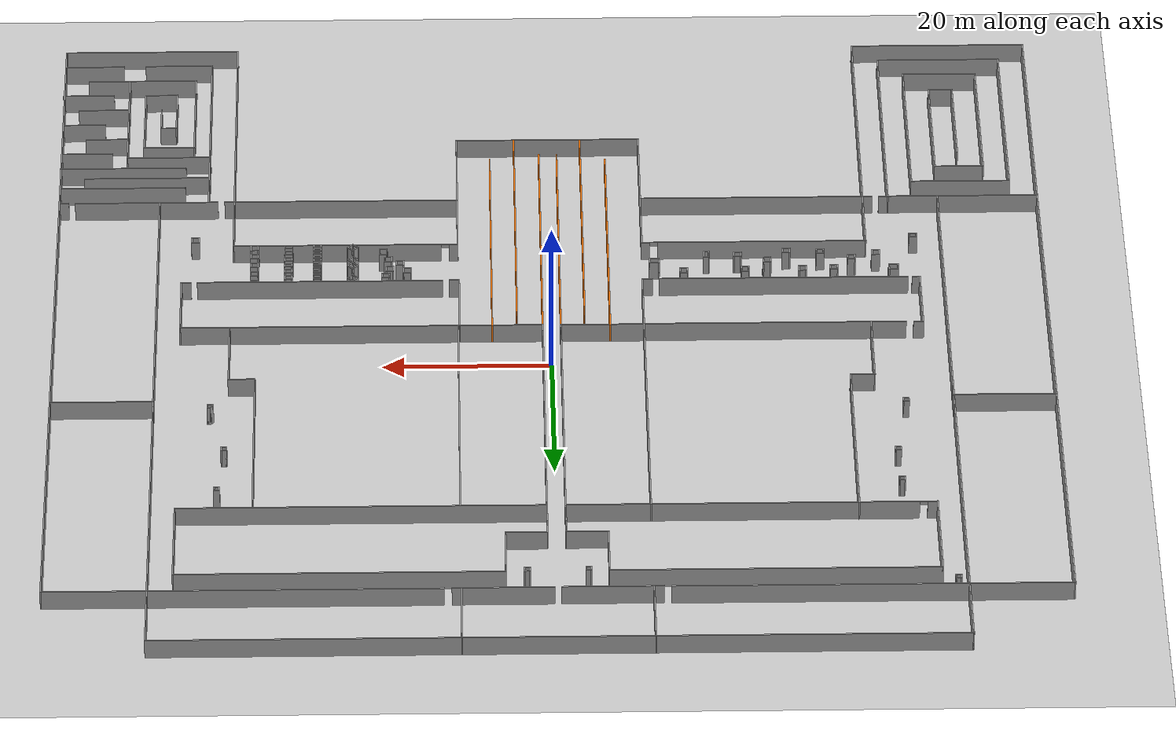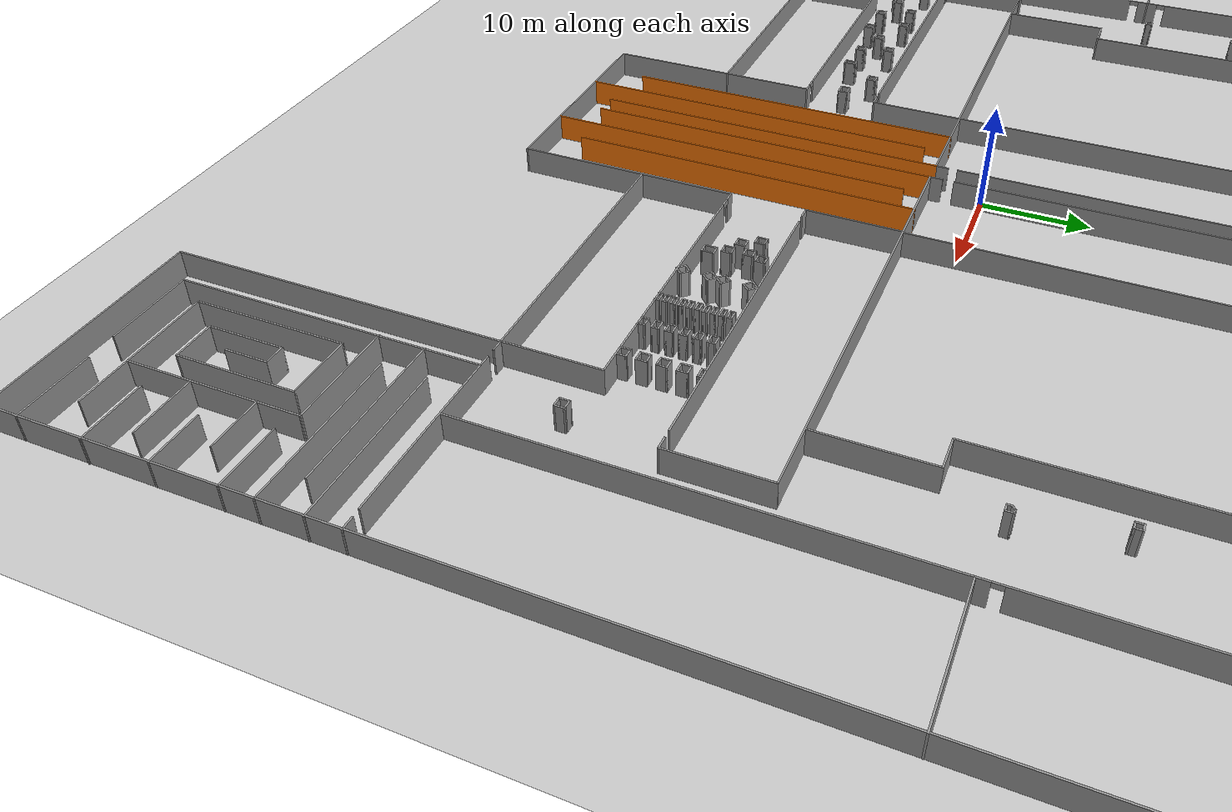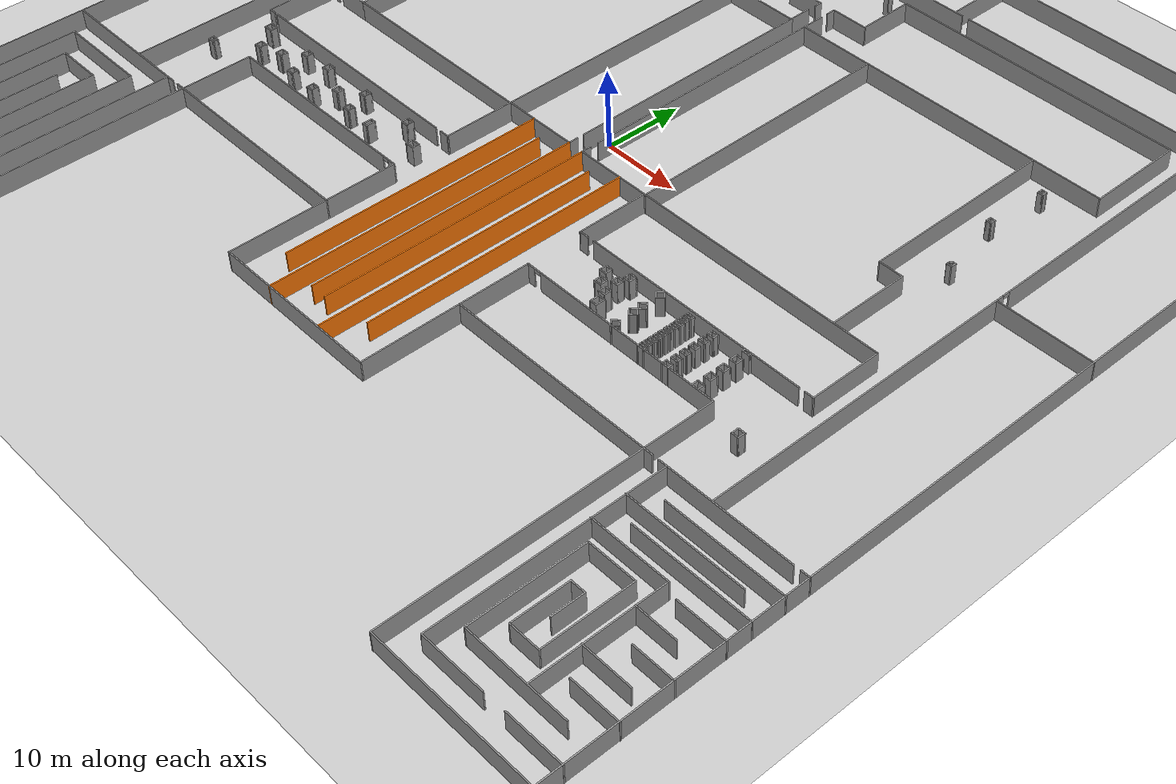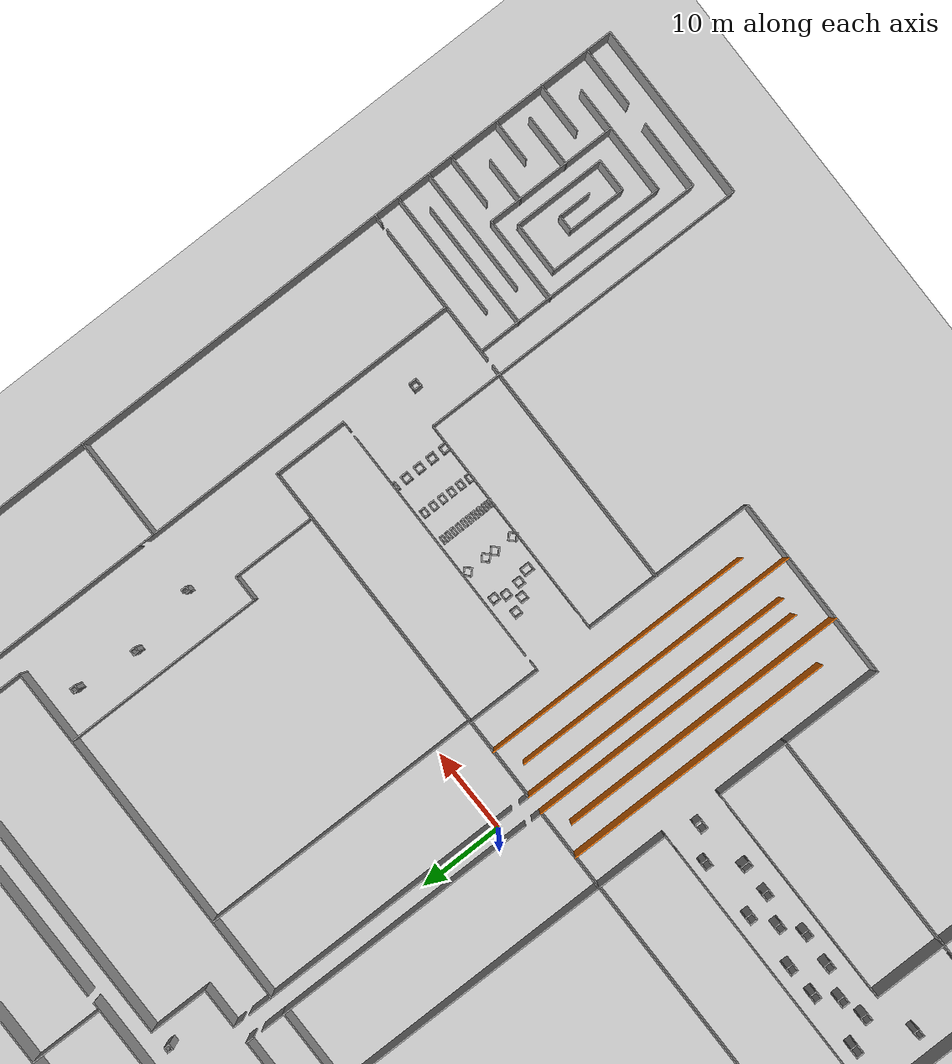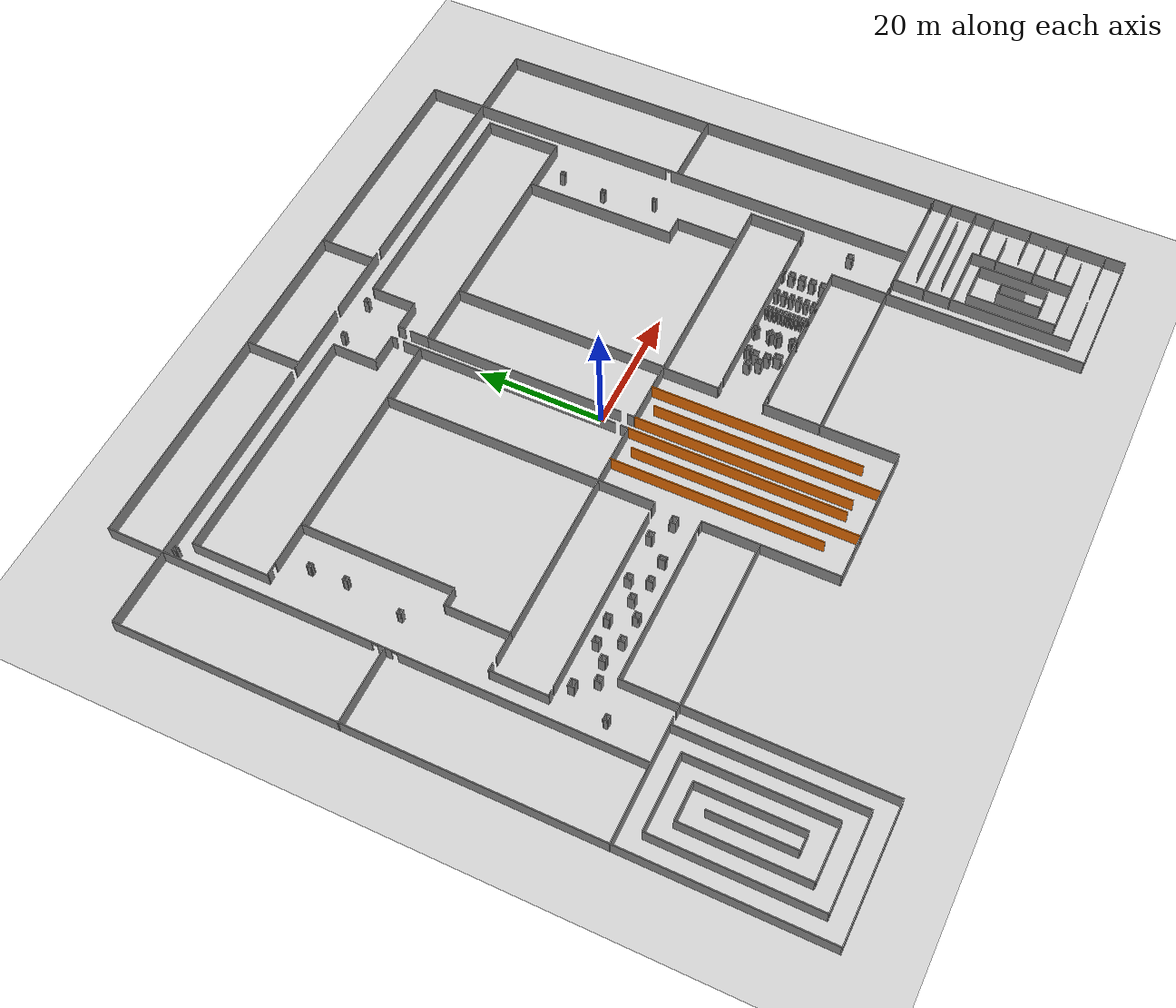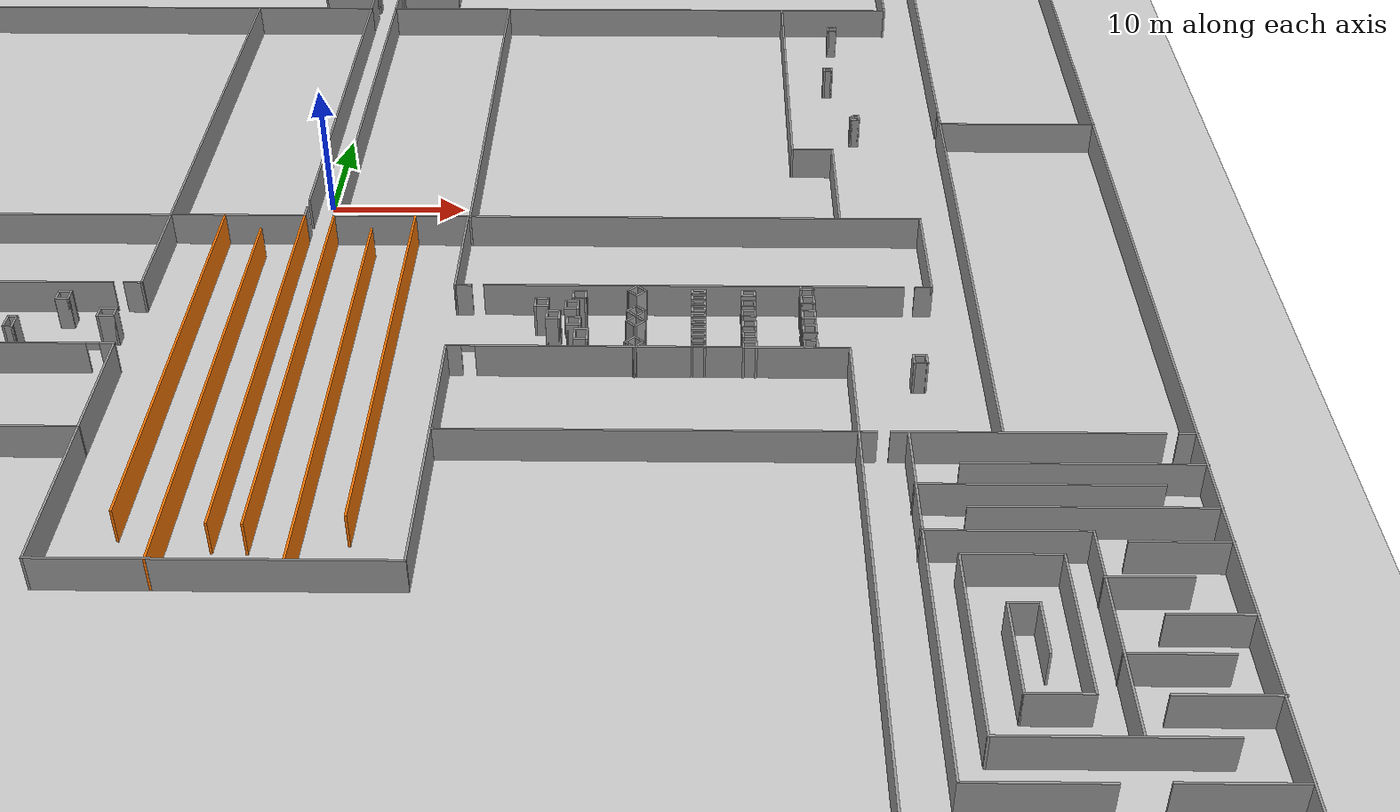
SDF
<sdf version="1.6">
 <world name="default">
  <light name="sun" type="directional">
   <pose>0 0 10 0 -0 0</pose>
   <diffuse>0.8 0.8 0.8 1</diffuse>
   <specular>0.2 0.2 0.2 1</specular>
   <attenuation>
    <range>1000</range>
    <constant>0.9</constant>
    <linear>0.01</linear>
    <quadratic>0.001</quadratic>
   </attenuation>
   <direction>-0.5 0.1 -0.9</direction>
  </light>
  <model name="ground_plane">
   <static>1</static>
   <link name="link">
    <collision name="collision">
     <geometry><plane><normal>0 0 1</normal><size>300 300</size></plane></geometry>
     <surface>
      <contact><collide_bitmask>65535</collide_bitmask></contact>
      <friction><ode><mu>100</mu><mu2>50</mu2></ode></friction>
     </surface>
    </collision>
    <visual name="visual">
     <cast_shadows>0</cast_shadows>
     <geometry><plane><normal>0 0 1</normal><size>300 300</size></plane></geometry>
     <material>
      <script><uri>file://media/materials/scripts/gazebo.material</uri><name>Gazebo/Grey</name></script>
     </material>
    </visual>
   </link>
  </model>
  <gravity>0 0 -9.8</gravity>
  <magnetic_field>6e-06 2.3e-05 -4.2e-05</magnetic_field>
  <atmosphere type="adiabatic"/>
  <physics name="default_physics" default="0" type="ode">
   <max_step_size>0.001</max_step_size>
   <real_time_factor>1</real_time_factor>
   <real_time_update_rate>1000</real_time_update_rate>
  </physics>
  <scene><ambient>0.4 0.4 0.4 1</ambient><background>0.7 0.7 0.7 1</background><shadows>1</shadows></scene>
  <audio><device>default</device></audio>
  <spherical_coordinates>
   <surface_model>EARTH_WGS84</surface_model>
   <latitude_deg>0</latitude_deg>
   <longitude_deg>0</longitude_deg>
   <elevation>0</elevation>
   <heading_deg>0</heading_deg>
  </spherical_coordinates>
  <model name="NIK">
   <pose>-0.005548 -3.7937 0 0 -0 0</pose>
   <link name="Wall_100">
    <collision name="Wall_100_Collision">
     <geometry><box><size>9.04424 0.15 2.5</size></box></geometry>
     <pose>0 0 1.25 0 -0 0</pose>
    </collision>
    <visual name="Wall_100_Visual">
     <pose>0 0 1.25 0 -0 0</pose>
     <geometry><box><size>9.04424 0.15 2.5</size></box></geometry>
     <material>
      <script><uri>file://media/materials/scripts/gazebo.material</uri><name>Gazebo/Grey</name></script>
      <ambient>1 1 1 1</ambient>
     </material>
     <meta><layer>0</layer></meta>
    </visual>
    <pose>10.8835 -5.474 0 0 -0 -1.571</pose>
   </link>
   <link name="Wall_103">
    <collision name="Wall_103_Collision">
     <geometry><box><size>38.25 0.15 2.5</size></box></geometry>
     <pose>0 0 1.25 0 -0 0</pose>
    </collision>
    <visual name="Wall_103_Visual">
     <pose>0 0 1.25 0 -0 0</pose>
     <geometry><box><size>38.25 0.15 2.5</size></box></geometry>
     <material>
      <script><uri>file://media/materials/scripts/gazebo.material</uri><name>Gazebo/Grey</name></script>
      <ambient>1 1 1 1</ambient>
     </material>
     <meta><layer>0</layer></meta>
    </visual>
    <pose>24.9325 45.1789 0 0 -0 3.14159</pose>
   </link>
   <link name="Wall_104">
    <collision name="Wall_104_Collision">
     <geometry><box><size>7.25 0.15 2.5</size></box></geometry>
     <pose>0 0 1.25 0 -0 0</pose>
    </collision>
    <visual name="Wall_104_Visual">
     <pose>0 0 1.25 0 -0 0</pose>
     <geometry><box><size>7.25 0.15 2.5</size></box></geometry>
     <material>
      <script><uri>file://media/materials/scripts/gazebo.material</uri><name>Gazebo/Grey</name></script>
      <ambient>1 1 1 1</ambient>
     </material>
     <meta><layer>0</layer></meta>
    </visual>
    <pose>5.88252 41.6289 0 0 -0 -1.5708</pose>
   </link>
   <link name="Wall_105">
    <collision name="Wall_105_Collision">
     <geometry><box><size>5 0.15 2.5</size></box></geometry>
     <pose>0 0 1.25 0 -0 0</pose>
    </collision>
    <visual name="Wall_105_Visual">
     <pose>0 0 1.25 0 -0 0</pose>
     <geometry><box><size>5 0.15 2.5</size></box></geometry>
     <material>
      <script><uri>file://media/materials/scripts/gazebo.material</uri><name>Gazebo/Grey</name></script>
      <ambient>1 1 1 1</ambient>
     </material>
     <meta><layer>0</layer></meta>
    </visual>
    <pose>3.45752 38.0789 0 0 -0 3.14159</pose>
   </link>
   <link name="Wall_107">
    <collision name="Wall_107_Collision">
     <geometry><box><size>43 0.15 2.5</size></box></geometry>
     <pose>0 0 1.25 0 -0 0</pose>
    </collision>
    <visual name="Wall_107_Visual">
     <pose>0 0 1.25 0 -0 0</pose>
     <geometry><box><size>43 0.15 2.5</size></box></geometry>
     <material>
      <script><uri>file://media/materials/scripts/gazebo.material</uri><name>Gazebo/Grey</name></script>
      <ambient>1 1 1 1</ambient>
     </material>
     <meta><layer>0</layer></meta>
    </visual>
    <pose>22.4661 33.102 0 0 -0 0</pose>
   </link>
   <link name="Wall_109">
    <collision name="Wall_109_Collision">
     <geometry><box><size>33.25 0.15 2.5</size></box></geometry>
     <pose>0 0 1.25 0 -0 0</pose>
    </collision>
    <visual name="Wall_109_Visual">
     <pose>0 0 1.25 0 -0 0</pose>
     <geometry><box><size>33.25 0.15 2.5</size></box></geometry>
     <material>
      <script><uri>file://media/materials/scripts/gazebo.material</uri><name>Gazebo/Grey</name></script>
      <ambient>1 1 1 1</ambient>
     </material>
     <meta><layer>0</layer></meta>
    </visual>
    <pose>27.4344 -1.02688 0 0 -0 0</pose>
   </link>
   <link name="Wall_11">
    <collision name="Wall_11_Collision">
     <geometry><box><size>9 0.15 2.5</size></box></geometry>
     <pose>0 0 1.25 0 -0 0</pose>
    </collision>
    <visual name="Wall_11_Visual">
     <pose>0 0 1.25 0 -0 0</pose>
     <geometry><box><size>9 0.15 2.5</size></box></geometry>
     <material>
      <script><uri>file://media/materials/scripts/gazebo.material</uri><name>Gazebo/Grey</name></script>
      <ambient>1 1 1 1</ambient>
     </material>
     <meta><layer>0</layer></meta>
    </visual>
    <pose>46.8813 52.5462 0 0 -0 -1.5708</pose>
   </link>
   <link name="Wall_111">
    <collision name="Wall_111_Collision">
     <geometry><box><size>34.25 0.15 2.5</size></box></geometry>
     <pose>0 0 1.25 0 -0 0</pose>
    </collision>
    <visual name="Wall_111_Visual">
     <pose>0 0 1.25 0 -0 0</pose>
     <geometry><box><size>34.25 0.15 2.5</size></box></geometry>
     <material>
      <script><uri>file://media/materials/scripts/gazebo.material</uri><name>Gazebo/Grey</name></script>
      <ambient>1 1 1 1</ambient>
     </material>
     <meta><layer>0</layer></meta>
    </visual>
    <pose>11.0372 15.9864 0 0 -0 -1.5708</pose>
   </link>
   <link name="Wall_113">
    <collision name="Wall_113_Collision">
     <geometry><box><size>24.25 0.15 2.5</size></box></geometry>
     <pose>0 0 1.25 0 -0 0</pose>
    </collision>
    <visual name="Wall_113_Visual">
     <pose>0 0 1.25 0 -0 0</pose>
     <geometry><box><size>24.25 0.15 2.5</size></box></geometry>
     <material>
      <script><uri>file://media/materials/scripts/gazebo.material</uri><name>Gazebo/Grey</name></script>
      <ambient>1 1 1 1</ambient>
     </material>
     <meta><layer>0</layer></meta>
    </visual>
    <pose>35.0192 21.0101 0 0 -0 -1.5708</pose>
   </link>
   <link name="Wall_114">
    <collision name="Wall_114_Collision">
     <geometry><box><size>3.25 0.15 2.5</size></box></geometry>
     <pose>0 0 1.25 0 -0 0</pose>
    </collision>
    <visual name="Wall_114_Visual">
     <pose>0 0 1.25 0 -0 0</pose>
     <geometry><box><size>3.25 0.15 2.5</size></box></geometry>
     <material>
      <script><uri>file://media/materials/scripts/gazebo.material</uri><name>Gazebo/Grey</name></script>
      <ambient>1 1 1 1</ambient>
     </material>
     <meta><layer>0</layer></meta>
    </visual>
    <pose>36.5692 8.96012 0 0 -0 0</pose>
   </link>
   <link name="Wall_115">
    <collision name="Wall_115_Collision">
     <geometry><box><size>10 0.15 2.5</size></box></geometry>
     <pose>0 0 1.25 0 -0 0</pose>
    </collision>
    <visual name="Wall_115_Visual">
     <pose>0 0 1.25 0 -0 0</pose>
     <geometry><box><size>10 0.15 2.5</size></box></geometry>
     <material>
      <script><uri>file://media/materials/scripts/gazebo.material</uri><name>Gazebo/Grey</name></script>
      <ambient>1 1 1 1</ambient>
     </material>
     <meta><layer>0</layer></meta>
    </visual>
    <pose>38.1192 4.03512 0 0 -0 -1.5708</pose>
   </link>
   <link name="Wall_117">
    <collision name="Wall_117_Collision">
     <geometry><box><size>12.25 0.15 2.5</size></box></geometry>
     <pose>0 0 1.25 0 -0 0</pose>
    </collision>
    <visual name="Wall_117_Visual">
     <pose>0 0 1.25 0 -0 0</pose>
     <geometry><box><size>12.25 0.15 2.5</size></box></geometry>
     <material>
      <script><uri>file://media/materials/scripts/gazebo.material</uri><name>Gazebo/Grey</name></script>
      <ambient>1 1 1 1</ambient>
     </material>
     <meta><layer>0</layer></meta>
    </visual>
    <pose>52.9572 13.0789 0 0 -0 0</pose>
   </link>
   <link name="Wall_120">
    <collision name="Wall_120_Collision">
     <geometry><box><size>9 0.15 2.5</size></box></geometry>
     <pose>0 0 1.25 0 -0 0</pose>
    </collision>
    <visual name="Wall_120_Visual">
     <pose>0 0 1.25 0 -0 0</pose>
     <geometry><box><size>9 0.15 2.5</size></box></geometry>
     <material>
      <script><uri>file://media/materials/scripts/gazebo.material</uri><name>Gazebo/Grey</name></script>
      <ambient>1 1 1 1</ambient>
     </material>
     <meta><layer>0</layer></meta>
    </visual>
    <pose>-37.9187 -21.4538 0 0 -0 1.5708</pose>
   </link>
   <link name="Wall_121">
    <pose>-24.4937 -17.0288 0 0 -0 0</pose>
    <visual name="Wall_121_Visual_0">
     <pose>-0.974548 0 1.25 0 -0 0</pose>
     <geometry><box><size>25.0509 0.15 2.5</size></box></geometry>
     <material>
      <script><uri>file://media/materials/scripts/gazebo.material</uri><name>Gazebo/Grey</name></script>
      <ambient>1 1 1 1</ambient>
     </material>
     <meta><layer>0</layer></meta>
    </visual>
    <collision name="Wall_121_Collision_0">
     <geometry><box><size>25.0509 0.15 2.5</size></box></geometry>
     <pose>-0.974548 0 1.25 0 -0 0</pose>
    </collision>
    <visual name="Wall_121_Visual_1">
     <pose>12.9755 0 1.25 0 -0 0</pose>
     <geometry><box><size>1.0491 0.15 2.5</size></box></geometry>
     <material>
      <script><uri>file://media/materials/scripts/gazebo.material</uri><name>Gazebo/Grey</name></script>
      <ambient>1 1 1 1</ambient>
     </material>
     <meta><layer>0</layer></meta>
    </visual>
    <collision name="Wall_121_Collision_1">
     <geometry><box><size>1.0491 0.15 2.5</size></box></geometry>
     <pose>12.9755 0 1.25 0 -0 0</pose>
    </collision>
    <visual name="Wall_121_Visual_2">
     <pose>12.0009 0 2.25 0 -0 0</pose>
     <geometry><box><size>0.9 0.15 0.5</size></box></geometry>
     <material>
      <script><uri>file://media/materials/scripts/gazebo.material</uri><name>Gazebo/Grey</name></script>
      <ambient>1 1 1 1</ambient>
     </material>
     <meta><layer>0</layer></meta>
    </visual>
    <collision name="Wall_121_Collision_2">
     <geometry><box><size>0.9 0.15 0.5</size></box></geometry>
     <pose>12.0009 0 2.25 0 -0 0</pose>
    </collision>
   </link>
   <link name="Wall_122">
    <collision name="Wall_122_Collision">
     <geometry><box><size>9 0.15 2.5</size></box></geometry>
     <pose>0 0 1.25 0 -0 0</pose>
    </collision>
    <visual name="Wall_122_Visual">
     <pose>0 0 1.25 0 -0 0</pose>
     <geometry><box><size>9 0.15 2.5</size></box></geometry>
     <material>
      <script><uri>file://media/materials/scripts/gazebo.material</uri><name>Gazebo/Grey</name></script>
      <ambient>1 1 1 1</ambient>
     </material>
     <meta><layer>0</layer></meta>
    </visual>
    <pose>-11.0687 -21.4538 0 0 -0 -1.5708</pose>
   </link>
   <link name="Wall_124">
    <collision name="Wall_124_Collision">
     <geometry><box><size>9 0.15 2.5</size></box></geometry>
     <pose>0 0 1.25 0 -0 0</pose>
    </collision>
    <visual name="Wall_124_Visual">
     <pose>0 0 1.25 0 -0 0</pose>
     <geometry><box><size>9 0.15 2.5</size></box></geometry>
     <material>
      <script><uri>file://media/materials/scripts/gazebo.material</uri><name>Gazebo/Grey</name></script>
      <ambient>1 1 1 1</ambient>
     </material>
     <meta><layer>0</layer></meta>
    </visual>
    <pose>11.0313 -21.4538 0 0 -0 1.5708</pose>
   </link>
   <link name="Wall_125">
    <pose>24.4563 -17.0288 0 0 -0 0</pose>
    <visual name="Wall_125_Visual_0">
     <pose>-12.9494 0 1.25 0 -0 0</pose>
     <geometry><box><size>1.10129 0.15 2.5</size></box></geometry>
     <material>
      <script><uri>file://media/materials/scripts/gazebo.material</uri><name>Gazebo/Grey</name></script>
      <ambient>1 1 1 1</ambient>
     </material>
     <meta><layer>0</layer></meta>
    </visual>
    <collision name="Wall_125_Collision_0">
     <geometry><box><size>1.10129 0.15 2.5</size></box></geometry>
     <pose>-12.9494 0 1.25 0 -0 0</pose>
    </collision>
    <visual name="Wall_125_Visual_1">
     <pose>1.00065 0 1.25 0 -0 0</pose>
     <geometry><box><size>24.9987 0.15 2.5</size></box></geometry>
     <material>
      <script><uri>file://media/materials/scripts/gazebo.material</uri><name>Gazebo/Grey</name></script>
      <ambient>1 1 1 1</ambient>
     </material>
     <meta><layer>0</layer></meta>
    </visual>
    <collision name="Wall_125_Collision_1">
     <geometry><box><size>24.9987 0.15 2.5</size></box></geometry>
     <pose>1.00065 0 1.25 0 -0 0</pose>
    </collision>
    <visual name="Wall_125_Visual_2">
     <pose>-11.9487 0 2.25 0 -0 0</pose>
     <geometry><box><size>0.9 0.15 0.5</size></box></geometry>
     <material>
      <script><uri>file://media/materials/scripts/gazebo.material</uri><name>Gazebo/Grey</name></script>
      <ambient>1 1 1 1</ambient>
     </material>
     <meta><layer>0</layer></meta>
    </visual>
    <collision name="Wall_125_Collision_2">
     <geometry><box><size>0.9 0.15 0.5</size></box></geometry>
     <pose>-11.9487 0 2.25 0 -0 0</pose>
    </collision>
   </link>
   <link name="Wall_126">
    <collision name="Wall_126_Collision">
     <geometry><box><size>9 0.15 2.5</size></box></geometry>
     <pose>0 0 1.25 0 -0 0</pose>
    </collision>
    <visual name="Wall_126_Visual">
     <pose>0 0 1.25 0 -0 0</pose>
     <geometry><box><size>9 0.15 2.5</size></box></geometry>
     <material>
      <script><uri>file://media/materials/scripts/gazebo.material</uri><name>Gazebo/Grey</name></script>
      <ambient>1 1 1 1</ambient>
     </material>
     <meta><layer>0</layer></meta>
    </visual>
    <pose>37.8813 -21.4538 0 0 -0 -1.5708</pose>
   </link>
   <link name="Wall_128">
    <collision name="Wall_128_Collision">
     <geometry><box><size>33 0.15 2.5</size></box></geometry>
     <pose>0 0 1.25 0 -0 0</pose>
    </collision>
    <visual name="Wall_128_Visual">
     <pose>0 0 1.25 0 -0 0</pose>
     <geometry><box><size>33 0.15 2.5</size></box></geometry>
     <material>
      <script><uri>file://media/materials/scripts/gazebo.material</uri><name>Gazebo/Grey</name></script>
      <ambient>0.996078 0.47451 0.0196078 1</ambient>
     </material>
     <meta><layer>0</layer></meta>
    </visual>
    <pose>-6.97645 -17.3923 0 0 -0 -1.5708</pose>
   </link>
   <link name="Wall_130">
    <collision name="Wall_130_Collision">
     <geometry><box><size>35.25 0.15 2.5</size></box></geometry>
     <pose>0 0 1.25 0 -0 0</pose>
    </collision>
    <visual name="Wall_130_Visual">
     <pose>0 0 1.25 0 -0 0</pose>
     <geometry><box><size>35.25 0.15 2.5</size></box></geometry>
     <material>
      <script><uri>file://media/materials/scripts/gazebo.material</uri><name>Gazebo/Grey</name></script>
      <ambient>0.996078 0.47451 0.0196078 1</ambient>
     </material>
     <meta><layer>0</layer></meta>
    </visual>
    <pose>-3.98545 -20.4373 0 0 -0 1.5708</pose>
   </link>
   <link name="Wall_132">
    <collision name="Wall_132_Collision">
     <geometry><box><size>34 0.15 2.5</size></box></geometry>
     <pose>0 0 1.25 0 -0 0</pose>
    </collision>
    <visual name="Wall_132_Visual">
     <pose>0 0 1.25 0 -0 0</pose>
     <geometry><box><size>34 0.15 2.5</size></box></geometry>
     <material>
      <script><uri>file://media/materials/scripts/gazebo.material</uri><name>Gazebo/Grey</name></script>
      <ambient>0.996078 0.47451 0.0196078 1</ambient>
     </material>
     <meta><layer>0</layer></meta>
    </visual>
    <pose>-1.11945 -17.9183 0 0 -0 -1.5708</pose>
   </link>
   <link name="Wall_134">
    <collision name="Wall_134_Collision">
     <geometry><box><size>34 0.15 2.5</size></box></geometry>
     <pose>0 0 1.25 0 -0 0</pose>
    </collision>
    <visual name="Wall_134_Visual">
     <pose>0 0 1.25 0 -0 0</pose>
     <geometry><box><size>34 0.15 2.5</size></box></geometry>
     <material>
      <script><uri>file://media/materials/scripts/gazebo.material</uri><name>Gazebo/Grey</name></script>
      <ambient>0.996078 0.47451 0.0196078 1</ambient>
     </material>
     <meta><layer>0</layer></meta>
    </visual>
    <pose>1.03455 -17.9523 0 0 -0 -1.5708</pose>
   </link>
   <link name="Wall_136">
    <collision name="Wall_136_Collision">
     <geometry><box><size>35.25 0.15 2.5</size></box></geometry>
     <pose>0 0 1.25 0 -0 0</pose>
    </collision>
    <visual name="Wall_136_Visual">
     <pose>0 0 1.25 0 -0 0</pose>
     <geometry><box><size>35.25 0.15 2.5</size></box></geometry>
     <material>
      <script><uri>file://media/materials/scripts/gazebo.material</uri><name>Gazebo/Grey</name></script>
      <ambient>0.996078 0.47451 0.0196078 1</ambient>
     </material>
     <meta><layer>0</layer></meta>
    </visual>
    <pose>4.05455 -20.3743 0 0 -0 1.5708</pose>
   </link>
   <link name="Wall_138">
    <collision name="Wall_138_Collision">
     <geometry><box><size>33.25 0.15 2.5</size></box></geometry>
     <pose>0 0 1.25 0 -0 0</pose>
    </collision>
    <visual name="Wall_138_Visual">
     <pose>0 0 1.25 0 -0 0</pose>
     <geometry><box><size>33.25 0.15 2.5</size></box></geometry>
     <material>
      <script><uri>file://media/materials/scripts/gazebo.material</uri><name>Gazebo/Grey</name></script>
      <ambient>0.996078 0.47451 0.0196078 1</ambient>
     </material>
     <meta><layer>0</layer></meta>
    </visual>
    <pose>7.01455 -17.5493 0 0 -0 -1.5708</pose>
   </link>
   <link name="Wall_140">
    <collision name="Wall_140_Collision">
     <geometry><box><size>28.25 0.15 2.5</size></box></geometry>
     <pose>0 0 1.25 0 -0 0</pose>
    </collision>
    <visual name="Wall_140_Visual">
     <pose>0 0 1.25 0 -0 0</pose>
     <geometry><box><size>28.25 0.15 2.5</size></box></geometry>
     <material>
      <script><uri>file://media/materials/scripts/gazebo.material</uri><name>Gazebo/Grey</name></script>
      <ambient>1 1 1 1</ambient>
     </material>
     <meta><layer>0</layer></meta>
    </visual>
    <pose>-40.9746 -39.9261 0 0 -0 -1.5708</pose>
   </link>
   <link name="Wall_141">
    <collision name="Wall_141_Collision">
     <geometry><box><size>15 0.15 2.5</size></box></geometry>
     <pose>0 0 1.25 0 -0 0</pose>
    </collision>
    <visual name="Wall_141_Visual">
     <pose>0 0 1.25 0 -0 0</pose>
     <geometry><box><size>15 0.15 2.5</size></box></geometry>
     <material>
      <script><uri>file://media/materials/scripts/gazebo.material</uri><name>Gazebo/Grey</name></script>
      <ambient>1 1 1 1</ambient>
     </material>
     <meta><layer>0</layer></meta>
    </visual>
    <pose>-48.3996 -53.9761 0 0 -0 3.14159</pose>
   </link>
   <link name="Wall_142">
    <collision name="Wall_142_Collision">
     <geometry><box><size>25.25 0.15 2.5</size></box></geometry>
     <pose>0 0 1.25 0 -0 0</pose>
    </collision>
    <visual name="Wall_142_Visual">
     <pose>0 0 1.25 0 -0 0</pose>
     <geometry><box><size>25.25 0.15 2.5</size></box></geometry>
     <material>
      <script><uri>file://media/materials/scripts/gazebo.material</uri><name>Gazebo/Grey</name></script>
      <ambient>1 1 1 1</ambient>
     </material>
     <meta><layer>0</layer></meta>
    </visual>
    <pose>-55.8246 -41.4261 0 0 -0 1.5708</pose>
   </link>
   <link name="Wall_143">
    <collision name="Wall_143_Collision">
     <geometry><box><size>12 0.15 2.5</size></box></geometry>
     <pose>0 0 1.25 0 -0 0</pose>
    </collision>
    <visual name="Wall_143_Visual">
     <pose>0 0 1.25 0 -0 0</pose>
     <geometry><box><size>12 0.15 2.5</size></box></geometry>
     <material>
      <script><uri>file://media/materials/scripts/gazebo.material</uri><name>Gazebo/Grey</name></script>
      <ambient>1 1 1 1</ambient>
     </material>
     <meta><layer>0</layer></meta>
    </visual>
    <pose>-49.8996 -28.8761 0 0 -0 0</pose>
   </link>
   <link name="Wall_144">
    <collision name="Wall_144_Collision">
     <geometry><box><size>22.25 0.15 2.5</size></box></geometry>
     <pose>0 0 1.25 0 -0 0</pose>
    </collision>
    <visual name="Wall_144_Visual">
     <pose>0 0 1.25 0 -0 0</pose>
     <geometry><box><size>22.25 0.15 2.5</size></box></geometry>
     <material>
      <script><uri>file://media/materials/scripts/gazebo.material</uri><name>Gazebo/Grey</name></script>
      <ambient>1 1 1 1</ambient>
     </material>
     <meta><layer>0</layer></meta>
    </visual>
    <pose>-43.9746 -39.9261 0 0 -0 -1.5708</pose>
   </link>
   <link name="Wall_145">
    <collision name="Wall_145_Collision">
     <geometry><box><size>9 0.15 2.5</size></box></geometry>
     <pose>0 0 1.25 0 -0 0</pose>
    </collision>
    <visual name="Wall_145_Visual">
     <pose>0 0 1.25 0 -0 0</pose>
     <geometry><box><size>9 0.15 2.5</size></box></geometry>
     <material>
      <script><uri>file://media/materials/scripts/gazebo.material</uri><name>Gazebo/Grey</name></script>
      <ambient>1 1 1 1</ambient>
     </material>
     <meta><layer>0</layer></meta>
    </visual>
    <pose>-48.3996 -50.9761 0 0 -0 3.14159</pose>
   </link>
   <link name="Wall_146">
    <collision name="Wall_146_Collision">
     <geometry><box><size>19.25 0.15 2.5</size></box></geometry>
     <pose>0 0 1.25 0 -0 0</pose>
    </collision>
    <visual name="Wall_146_Visual">
     <pose>0 0 1.25 0 -0 0</pose>
     <geometry><box><size>19.25 0.15 2.5</size></box></geometry>
     <material>
      <script><uri>file://media/materials/scripts/gazebo.material</uri><name>Gazebo/Grey</name></script>
      <ambient>1 1 1 1</ambient>
     </material>
     <meta><layer>0</layer></meta>
    </visual>
    <pose>-52.8246 -41.4261 0 0 -0 1.5708</pose>
   </link>
   <link name="Wall_147">
    <collision name="Wall_147_Collision">
     <geometry><box><size>6 0.15 2.5</size></box></geometry>
     <pose>0 0 1.25 0 -0 0</pose>
    </collision>
    <visual name="Wall_147_Visual">
     <pose>0 0 1.25 0 -0 0</pose>
     <geometry><box><size>6 0.15 2.5</size></box></geometry>
     <material>
      <script><uri>file://media/materials/scripts/gazebo.material</uri><name>Gazebo/Grey</name></script>
      <ambient>1 1 1 1</ambient>
     </material>
     <meta><layer>0</layer></meta>
    </visual>
    <pose>-49.8996 -31.8761 0 0 -0 0</pose>
   </link>
   <link name="Wall_148">
    <collision name="Wall_148_Collision">
     <geometry><box><size>16 0.15 2.5</size></box></geometry>
     <pose>0 0 1.25 0 -0 0</pose>
    </collision>
    <visual name="Wall_148_Visual">
     <pose>0 0 1.25 0 -0 0</pose>
     <geometry><box><size>16 0.15 2.5</size></box></geometry>
     <material>
      <script><uri>file://media/materials/scripts/gazebo.material</uri><name>Gazebo/Grey</name></script>
      <ambient>1 1 1 1</ambient>
     </material>
     <meta><layer>0</layer></meta>
    </visual>
    <pose>-46.9746 -39.8011 0 0 -0 -1.5708</pose>
   </link>
   <link name="Wall_149">
    <collision name="Wall_149_Collision">
     <geometry><box><size>3 0.15 2.5</size></box></geometry>
     <pose>0 0 1.25 0 -0 0</pose>
    </collision>
    <visual name="Wall_149_Visual">
     <pose>0 0 1.25 0 -0 0</pose>
     <geometry><box><size>3 0.15 2.5</size></box></geometry>
     <material>
      <script><uri>file://media/materials/scripts/gazebo.material</uri><name>Gazebo/Grey</name></script>
      <ambient>1 1 1 1</ambient>
     </material>
     <meta><layer>0</layer></meta>
    </visual>
    <pose>-48.3996 -47.7261 0 0 -0 3.14159</pose>
   </link>
   <link name="Wall_150">
    <collision name="Wall_150_Collision">
     <geometry><box><size>13 0.15 2.5</size></box></geometry>
     <pose>0 0 1.25 0 -0 0</pose>
    </collision>
    <visual name="Wall_150_Visual">
     <pose>0 0 1.25 0 -0 0</pose>
     <geometry><box><size>13 0.15 2.5</size></box></geometry>
     <material>
      <script><uri>file://media/materials/scripts/gazebo.material</uri><name>Gazebo/Grey</name></script>
      <ambient>1 1 1 1</ambient>
     </material>
     <meta><layer>0</layer></meta>
    </visual>
    <pose>-49.8246 -41.3011 0 0 -0 1.5708</pose>
   </link>
   <link name="Wall_152">
    <collision name="Wall_152_Collision">
     <geometry><box><size>28.25 0.15 2.5</size></box></geometry>
     <pose>0 0 1.25 0 -0 0</pose>
    </collision>
    <visual name="Wall_152_Visual">
     <pose>0 0 1.25 0 -0 0</pose>
     <geometry><box><size>28.25 0.15 2.5</size></box></geometry>
     <material>
      <script><uri>file://media/materials/scripts/gazebo.material</uri><name>Gazebo/Grey</name></script>
      <ambient>1 1 1 1</ambient>
     </material>
     <meta><layer>0</layer></meta>
    </visual>
    <pose>40.9954 -39.9466 0 0 -0 -1.5708</pose>
   </link>
   <link name="Wall_153">
    <collision name="Wall_153_Collision">
     <geometry><box><size>8.25 0.15 2.5</size></box></geometry>
     <pose>0 0 1.25 0 -0 0</pose>
    </collision>
    <visual name="Wall_153_Visual">
     <pose>0 0 1.25 0 -0 0</pose>
     <geometry><box><size>8.25 0.15 2.5</size></box></geometry>
     <material>
      <script><uri>file://media/materials/scripts/gazebo.material</uri><name>Gazebo/Grey</name></script>
      <ambient>1 1 1 1</ambient>
     </material>
     <meta><layer>0</layer></meta>
    </visual>
    <pose>45.0454 -53.9966 0 0 -0 0</pose>
   </link>
   <link name="Wall_155">
    <collision name="Wall_155_Collision">
     <geometry><box><size>7.25 0.15 2.5</size></box></geometry>
     <pose>0 0 1.25 0 -0 0</pose>
    </collision>
    <visual name="Wall_155_Visual">
     <pose>0 0 1.25 0 -0 0</pose>
     <geometry><box><size>7.25 0.15 2.5</size></box></geometry>
     <material>
      <script><uri>file://media/materials/scripts/gazebo.material</uri><name>Gazebo/Grey</name></script>
      <ambient>1 1 1 1</ambient>
     </material>
     <meta><layer>0</layer></meta>
    </visual>
    <pose>55.4543 -53.929 0 0 -0 3.14159</pose>
   </link>
   <link name="Wall_157">
    <collision name="Wall_157_Collision">
     <geometry><box><size>13.25 0.15 2.5</size></box></geometry>
     <pose>0 0 1.25 0 -0 0</pose>
    </collision>
    <visual name="Wall_157_Visual">
     <pose>0 0 1.25 0 -0 0</pose>
     <geometry><box><size>13.25 0.15 2.5</size></box></geometry>
     <material>
      <script><uri>file://media/materials/scripts/gazebo.material</uri><name>Gazebo/Grey</name></script>
      <ambient>1 1 1 1</ambient>
     </material>
     <meta><layer>0</layer></meta>
    </visual>
    <pose>49.4686 -50.8959 0 0 -0 3.14159</pose>
   </link>
   <link name="Wall_158">
    <collision name="Wall_158_Collision">
     <geometry><box><size>14 0.15 2.5</size></box></geometry>
     <pose>0 0 1.25 0 -0 0</pose>
    </collision>
    <visual name="Wall_158_Visual">
     <pose>0 0 1.25 0 -0 0</pose>
     <geometry><box><size>14 0.15 2.5</size></box></geometry>
     <material>
      <script><uri>file://media/materials/scripts/gazebo.material</uri><name>Gazebo/Grey</name></script>
      <ambient>1 1 1 1</ambient>
     </material>
     <meta><layer>0</layer></meta>
    </visual>
    <pose>42.9186 -43.9709 0 0 -0 1.5708</pose>
   </link>
   <link name="Wall_159">
    <collision name="Wall_159_Collision">
     <geometry><box><size>6.25 0.15 2.5</size></box></geometry>
     <pose>0 0 1.25 0 -0 0</pose>
    </collision>
    <visual name="Wall_159_Visual">
     <pose>0 0 1.25 0 -0 0</pose>
     <geometry><box><size>6.25 0.15 2.5</size></box></geometry>
     <material>
      <script><uri>file://media/materials/scripts/gazebo.material</uri><name>Gazebo/Grey</name></script>
      <ambient>1 1 1 1</ambient>
     </material>
     <meta><layer>0</layer></meta>
    </visual>
    <pose>45.9686 -37.0459 0 0 -0 0</pose>
   </link>
   <link name="Wall_16">
    <collision name="Wall_16_Collision">
     <geometry><box><size>12.25 0.15 2.5</size></box></geometry>
     <pose>0 0 1.25 0 -0 0</pose>
    </collision>
    <visual name="Wall_16_Visual">
     <pose>0 0 1.25 0 -0 0</pose>
     <geometry><box><size>12.25 0.15 2.5</size></box></geometry>
     <material>
      <script><uri>file://media/materials/scripts/gazebo.material</uri><name>Gazebo/Grey</name></script>
      <ambient>1 1 1 1</ambient>
     </material>
     <meta><layer>0</layer></meta>
    </visual>
    <pose>52.9313 48.1212 0 0 -0 0</pose>
   </link>
   <link name="Wall_160">
    <collision name="Wall_160_Collision">
     <geometry><box><size>11 0.15 2.5</size></box></geometry>
     <pose>0 0 1.25 0 -0 0</pose>
    </collision>
    <visual name="Wall_160_Visual">
     <pose>0 0 1.25 0 -0 0</pose>
     <geometry><box><size>11 0.15 2.5</size></box></geometry>
     <material>
      <script><uri>file://media/materials/scripts/gazebo.material</uri><name>Gazebo/Grey</name></script>
      <ambient>1 1 1 1</ambient>
     </material>
     <meta><layer>0</layer></meta>
    </visual>
    <pose>49.0186 -42.4709 0 0 -0 -1.5708</pose>
   </link>
   <link name="Wall_161">
    <collision name="Wall_161_Collision">
     <geometry><box><size>4 0.15 2.5</size></box></geometry>
     <pose>0 0 1.25 0 -0 0</pose>
    </collision>
    <visual name="Wall_161_Visual">
     <pose>0 0 1.25 0 -0 0</pose>
     <geometry><box><size>4 0.15 2.5</size></box></geometry>
     <material>
      <script><uri>file://media/materials/scripts/gazebo.material</uri><name>Gazebo/Grey</name></script>
      <ambient>1 1 1 1</ambient>
     </material>
     <meta><layer>0</layer></meta>
    </visual>
    <pose>47.0936 -47.8959 0 0 -0 3.14159</pose>
   </link>
   <link name="Wall_162">
    <collision name="Wall_162_Collision">
     <geometry><box><size>7 0.15 2.5</size></box></geometry>
     <pose>0 0 1.25 0 -0 0</pose>
    </collision>
    <visual name="Wall_162_Visual">
     <pose>0 0 1.25 0 -0 0</pose>
     <geometry><box><size>7 0.15 2.5</size></box></geometry>
     <material>
      <script><uri>file://media/materials/scripts/gazebo.material</uri><name>Gazebo/Grey</name></script>
      <ambient>1 1 1 1</ambient>
     </material>
     <meta><layer>0</layer></meta>
    </visual>
    <pose>45.1686 -44.4709 0 0 -0 1.5708</pose>
   </link>
   <link name="Wall_163">
    <collision name="Wall_163_Collision">
     <geometry><box><size>2 0.15 2.5</size></box></geometry>
     <pose>0 0 1.25 0 -0 0</pose>
    </collision>
    <visual name="Wall_163_Visual">
     <pose>0 0 1.25 0 -0 0</pose>
     <geometry><box><size>2 0.15 2.5</size></box></geometry>
     <material>
      <script><uri>file://media/materials/scripts/gazebo.material</uri><name>Gazebo/Grey</name></script>
      <ambient>1 1 1 1</ambient>
     </material>
     <meta><layer>0</layer></meta>
    </visual>
    <pose>46.0936 -41.0459 0 0 -0 0</pose>
   </link>
   <link name="Wall_164">
    <collision name="Wall_164_Collision">
     <geometry><box><size>4 0.15 2.5</size></box></geometry>
     <pose>0 0 1.25 0 -0 0</pose>
    </collision>
    <visual name="Wall_164_Visual">
     <pose>0 0 1.25 0 -0 0</pose>
     <geometry><box><size>4 0.15 2.5</size></box></geometry>
     <material>
      <script><uri>file://media/materials/scripts/gazebo.material</uri><name>Gazebo/Grey</name></script>
      <ambient>1 1 1 1</ambient>
     </material>
     <meta><layer>0</layer></meta>
    </visual>
    <pose>47.0186 -42.9709 0 0 -0 -1.5708</pose>
   </link>
   <link name="Wall_166">
    <collision name="Wall_166_Collision">
     <geometry><box><size>16 0.15 2.5</size></box></geometry>
     <pose>0 0 1.25 0 -0 0</pose>
    </collision>
    <visual name="Wall_166_Visual">
     <pose>0 0 1.25 0 -0 0</pose>
     <geometry><box><size>16 0.15 2.5</size></box></geometry>
     <material>
      <script><uri>file://media/materials/scripts/gazebo.material</uri><name>Gazebo/Grey</name></script>
      <ambient>1 1 1 1</ambient>
     </material>
     <meta><layer>0</layer></meta>
    </visual>
    <pose>51.0188 -42.9472 0 0 -0 1.5708</pose>
   </link>
   <link name="Wall_167">
    <collision name="Wall_167_Collision">
     <geometry><box><size>10.25 0.15 2.5</size></box></geometry>
     <pose>0 0 1.25 0 -0 0</pose>
    </collision>
    <visual name="Wall_167_Visual">
     <pose>0 0 1.25 0 -0 0</pose>
     <geometry><box><size>10.25 0.15 2.5</size></box></geometry>
     <material>
      <script><uri>file://media/materials/scripts/gazebo.material</uri><name>Gazebo/Grey</name></script>
      <ambient>1 1 1 1</ambient>
     </material>
     <meta><layer>0</layer></meta>
    </visual>
    <pose>45.9688 -35.0222 0 0 -0 3.14159</pose>
   </link>
   <link name="Wall_169">
    <collision name="Wall_169_Collision">
     <geometry><box><size>6.25 0.15 2.5</size></box></geometry>
     <pose>0 0 1.25 0 -0 0</pose>
    </collision>
    <visual name="Wall_169_Visual">
     <pose>0 0 1.25 0 -0 0</pose>
     <geometry><box><size>6.25 0.15 2.5</size></box></geometry>
     <material>
      <script><uri>file://media/materials/scripts/gazebo.material</uri><name>Gazebo/Grey</name></script>
      <ambient>1 1 1 1</ambient>
     </material>
     <meta><layer>0</layer></meta>
    </visual>
    <pose>56.0119 -47.9102 0 0 -0 0</pose>
   </link>
   <link name="Wall_17">
    <collision name="Wall_17_Collision">
     <geometry><box><size>105.25 0.15 2.5</size></box></geometry>
     <pose>0 0 1.25 0 -0 0</pose>
    </collision>
    <visual name="Wall_17_Visual">
     <pose>0 0 1.25 0 -0 0</pose>
     <geometry><box><size>105.25 0.15 2.5</size></box></geometry>
     <material>
      <script><uri>file://media/materials/scripts/gazebo.material</uri><name>Gazebo/Grey</name></script>
      <ambient>1 1 1 1</ambient>
     </material>
     <meta><layer>0</layer></meta>
    </visual>
    <pose>58.9813 -4.42876 0 0 -0 -1.5708</pose>
   </link>
   <link name="Wall_171">
    <collision name="Wall_171_Collision">
     <geometry><box><size>6.25 0.15 2.5</size></box></geometry>
     <pose>0 0 1.25 0 -0 0</pose>
    </collision>
    <visual name="Wall_171_Visual">
     <pose>0 0 1.25 0 -0 0</pose>
     <geometry><box><size>6.25 0.15 2.5</size></box></geometry>
     <material>
      <script><uri>file://media/materials/scripts/gazebo.material</uri><name>Gazebo/Grey</name></script>
      <ambient>1 1 1 1</ambient>
     </material>
     <meta><layer>0</layer></meta>
    </visual>
    <pose>54.035 -44.9008 0 0 -0 3.14159</pose>
   </link>
   <link name="Wall_173">
    <collision name="Wall_173_Collision">
     <geometry><box><size>5.25 0.15 2.5</size></box></geometry>
     <pose>0 0 1.25 0 -0 0</pose>
    </collision>
    <visual name="Wall_173_Visual">
     <pose>0 0 1.25 0 -0 0</pose>
     <geometry><box><size>5.25 0.15 2.5</size></box></geometry>
     <material>
      <script><uri>file://media/materials/scripts/gazebo.material</uri><name>Gazebo/Grey</name></script>
      <ambient>1 1 1 1</ambient>
     </material>
     <meta><layer>0</layer></meta>
    </visual>
    <pose>56.4497 -41.8577 0 0 -0 3.14159</pose>
   </link>
   <link name="Wall_175">
    <collision name="Wall_175_Collision">
     <geometry><box><size>5.25 0.15 2.5</size></box></geometry>
     <pose>0 0 1.25 0 -0 0</pose>
    </collision>
    <visual name="Wall_175_Visual">
     <pose>0 0 1.25 0 -0 0</pose>
     <geometry><box><size>5.25 0.15 2.5</size></box></geometry>
     <material>
      <script><uri>file://media/materials/scripts/gazebo.material</uri><name>Gazebo/Grey</name></script>
      <ambient>1 1 1 1</ambient>
     </material>
     <meta><layer>0</layer></meta>
    </visual>
    <pose>53.5405 -38.8655 0 0 -0 0</pose>
   </link>
   <link name="Wall_177">
    <collision name="Wall_177_Collision">
     <geometry><box><size>6.25 0.15 2.5</size></box></geometry>
     <pose>0 0 1.25 0 -0 0</pose>
    </collision>
    <visual name="Wall_177_Visual">
     <pose>0 0 1.25 0 -0 0</pose>
     <geometry><box><size>6.25 0.15 2.5</size></box></geometry>
     <material>
      <script><uri>file://media/materials/scripts/gazebo.material</uri><name>Gazebo/Grey</name></script>
      <ambient>1 1 1 1</ambient>
     </material>
     <meta><layer>0</layer></meta>
    </visual>
    <pose>55.9676 -35.8912 0 0 -0 3.14159</pose>
   </link>
   <link name="Wall_179">
    <collision name="Wall_179_Collision">
     <geometry><box><size>15.25 0.15 2.5</size></box></geometry>
     <pose>0 0 1.25 0 -0 0</pose>
    </collision>
    <visual name="Wall_179_Visual">
     <pose>0 0 1.25 0 -0 0</pose>
     <geometry><box><size>15.25 0.15 2.5</size></box></geometry>
     <material>
      <script><uri>file://media/materials/scripts/gazebo.material</uri><name>Gazebo/Grey</name></script>
      <ambient>1 1 1 1</ambient>
     </material>
     <meta><layer>0</layer></meta>
    </visual>
    <pose>51.4497 -32.8989 0 0 -0 3.14159</pose>
   </link>
   <link name="Wall_181">
    <collision name="Wall_181_Collision">
     <geometry><box><size>15.25 0.15 2.5</size></box></geometry>
     <pose>0 0 1.25 0 -0 0</pose>
    </collision>
    <visual name="Wall_181_Visual">
     <pose>0 0 1.25 0 -0 0</pose>
     <geometry><box><size>15.25 0.15 2.5</size></box></geometry>
     <material>
      <script><uri>file://media/materials/scripts/gazebo.material</uri><name>Gazebo/Grey</name></script>
      <ambient>1 1 1 1</ambient>
     </material>
     <meta><layer>0</layer></meta>
    </visual>
    <pose>48.4887 -30.8563 0 0 -0 0</pose>
   </link>
   <link name="Wall_183">
    <collision name="Wall_183_Collision">
     <geometry><box><size>15.25 0.15 2.5</size></box></geometry>
     <pose>0 0 1.25 0 -0 0</pose>
    </collision>
    <visual name="Wall_183_Visual">
     <pose>0 0 1.25 0 -0 0</pose>
     <geometry><box><size>15.25 0.15 2.5</size></box></geometry>
     <material>
      <script><uri>file://media/materials/scripts/gazebo.material</uri><name>Gazebo/Grey</name></script>
      <ambient>1 1 1 1</ambient>
     </material>
     <meta><layer>0</layer></meta>
    </visual>
    <pose>51.4676 -28.8675 0 0 -0 3.14159</pose>
   </link>
   <link name="Wall_185">
    <collision name="Wall_185_Collision">
     <geometry><box><size>12.25 0.15 2.5</size></box></geometry>
     <pose>0 0 1.25 0 -0 0</pose>
    </collision>
    <visual name="Wall_185_Visual">
     <pose>0 0 1.25 0 -0 0</pose>
     <geometry><box><size>12.25 0.15 2.5</size></box></geometry>
     <material>
      <script><uri>file://media/materials/scripts/gazebo.material</uri><name>Gazebo/Grey</name></script>
      <ambient>1 1 1 1</ambient>
     </material>
     <meta><layer>0</layer></meta>
    </visual>
    <pose>43.9825 39.1289 0 0 -0 -1.5708</pose>
   </link>
   <link name="Wall_187">
    <collision name="Wall_187_Collision">
     <geometry><box><size>9 0.15 2.5</size></box></geometry>
     <pose>0 0 1.25 0 -0 0</pose>
    </collision>
    <visual name="Wall_187_Visual">
     <pose>0 0 1.25 0 -0 0</pose>
     <geometry><box><size>9 0.15 2.5</size></box></geometry>
     <material>
      <script><uri>file://media/materials/scripts/gazebo.material</uri><name>Gazebo/Grey</name></script>
      <ambient>1 1 1 1</ambient>
     </material>
     <meta><layer>0</layer></meta>
    </visual>
    <pose>43.9844 -5.45188 0 0 -0 -1.5708</pose>
   </link>
   <link name="Wall_189">
    <collision name="Wall_189_Collision">
     <geometry><box><size>9 0.15 2.5</size></box></geometry>
     <pose>0 0 1.25 0 -0 0</pose>
    </collision>
    <visual name="Wall_189_Visual">
     <pose>0 0 1.25 0 -0 0</pose>
     <geometry><box><size>9 0.15 2.5</size></box></geometry>
     <material>
      <script><uri>file://media/materials/scripts/gazebo.material</uri><name>Gazebo/Grey</name></script>
      <ambient>1 1 1 1</ambient>
     </material>
     <meta><layer>0</layer></meta>
    </visual>
    <pose>-44.0698 -5.41854 0 0 -0 -1.5708</pose>
   </link>
   <link name="Wall_19">
    <collision name="Wall_19_Collision">
     <geometry><box><size>21.25 0.15 2.5</size></box></geometry>
     <pose>0 0 1.25 0 -0 0</pose>
    </collision>
    <visual name="Wall_19_Visual">
     <pose>0 0 1.25 0 -0 0</pose>
     <geometry><box><size>21.25 0.15 2.5</size></box></geometry>
     <material>
      <script><uri>file://media/materials/scripts/gazebo.material</uri><name>Gazebo/Grey</name></script>
      <ambient>1 1 1 1</ambient>
     </material>
     <meta><layer>0</layer></meta>
    </visual>
    <pose>48.4313 -56.9788 0 0 -0 3.14159</pose>
   </link>
   <link name="Wall_193">
    <collision name="Wall_193_Collision">
     <geometry><box><size>1 0.15 2.5</size></box></geometry>
     <pose>0 0 1.25 0 -0 0</pose>
    </collision>
    <visual name="Wall_193_Visual">
     <pose>0 0 1.25 0 -0 0</pose>
     <geometry><box><size>1 0.15 2.5</size></box></geometry>
     <material>
      <script><uri>file://media/materials/scripts/gazebo.material</uri><name>Gazebo/Grey</name></script>
      <ambient>1 1 1 1</ambient>
     </material>
     <meta><layer>0</layer></meta>
    </visual>
    <pose>-15.5545 -11.4442 0 0 -0 -1.5708</pose>
   </link>
   <link name="Wall_194">
    <collision name="Wall_194_Collision">
     <geometry><box><size>1 0.15 2.5</size></box></geometry>
     <pose>0 0 1.25 0 -0 0</pose>
    </collision>
    <visual name="Wall_194_Visual">
     <pose>0 0 1.25 0 -0 0</pose>
     <geometry><box><size>1 0.15 2.5</size></box></geometry>
     <material>
      <script><uri>file://media/materials/scripts/gazebo.material</uri><name>Gazebo/Grey</name></script>
      <ambient>1 1 1 1</ambient>
     </material>
     <meta><layer>0</layer></meta>
    </visual>
    <pose>-15.9795 -11.8692 0 0 -0 3.14159</pose>
   </link>
   <link name="Wall_195">
    <collision name="Wall_195_Collision">
     <geometry><box><size>1 0.15 2.5</size></box></geometry>
     <pose>0 0 1.25 0 -0 0</pose>
    </collision>
    <visual name="Wall_195_Visual">
     <pose>0 0 1.25 0 -0 0</pose>
     <geometry><box><size>1 0.15 2.5</size></box></geometry>
     <material>
      <script><uri>file://media/materials/scripts/gazebo.material</uri><name>Gazebo/Grey</name></script>
      <ambient>1 1 1 1</ambient>
     </material>
     <meta><layer>0</layer></meta>
    </visual>
    <pose>-16.4045 -11.4442 0 0 -0 1.5708</pose>
   </link>
   <link name="Wall_196">
    <collision name="Wall_196_Collision">
     <geometry><box><size>1 0.15 2.5</size></box></geometry>
     <pose>0 0 1.25 0 -0 0</pose>
    </collision>
    <visual name="Wall_196_Visual">
     <pose>0 0 1.25 0 -0 0</pose>
     <geometry><box><size>1 0.15 2.5</size></box></geometry>
     <material>
      <script><uri>file://media/materials/scripts/gazebo.material</uri><name>Gazebo/Grey</name></script>
      <ambient>1 1 1 1</ambient>
     </material>
     <meta><layer>0</layer></meta>
    </visual>
    <pose>-15.9795 -11.0192 0 0 -0 0</pose>
   </link>
   <link name="Wall_198">
    <collision name="Wall_198_Collision">
     <geometry><box><size>0.75 0.15 2.5</size></box></geometry>
     <pose>0 0 1.25 0 -0 0</pose>
    </collision>
    <visual name="Wall_198_Visual">
     <pose>0 0 1.25 0 -0 0</pose>
     <geometry><box><size>0.75 0.15 2.5</size></box></geometry>
     <material>
      <script><uri>file://media/materials/scripts/gazebo.material</uri><name>Gazebo/Grey</name></script>
      <ambient>1 1 1 1</ambient>
     </material>
     <meta><layer>0</layer></meta>
    </visual>
    <pose>-18.7432 -14.038 0 0 -0 0</pose>
   </link>
   <link name="Wall_199">
    <collision name="Wall_199_Collision">
     <geometry><box><size>1.25 0.15 2.5</size></box></geometry>
     <pose>0 0 1.25 0 -0 0</pose>
    </collision>
    <visual name="Wall_199_Visual">
     <pose>0 0 1.25 0 -0 0</pose>
     <geometry><box><size>1.25 0.15 2.5</size></box></geometry>
     <material>
      <script><uri>file://media/materials/scripts/gazebo.material</uri><name>Gazebo/Grey</name></script>
      <ambient>1 1 1 1</ambient>
     </material>
     <meta><layer>0</layer></meta>
    </visual>
    <pose>-18.4432 -14.588 0 0 -0 -1.5708</pose>
   </link>
   <link name="Wall_20">
    <collision name="Wall_20_Collision">
     <geometry><box><size>31.25 0.15 2.5</size></box></geometry>
     <pose>0 0 1.25 0 -0 0</pose>
    </collision>
    <visual name="Wall_20_Visual">
     <pose>0 0 1.25 0 -0 0</pose>
     <geometry><box><size>31.25 0.15 2.5</size></box></geometry>
     <material>
      <script><uri>file://media/materials/scripts/gazebo.material</uri><name>Gazebo/Grey</name></script>
      <ambient>1 1 1 1</ambient>
     </material>
     <meta><layer>0</layer></meta>
    </visual>
    <pose>37.8813 -41.4288 0 0 -0 1.5708</pose>
   </link>
   <link name="Wall_200">
    <collision name="Wall_200_Collision">
     <geometry><box><size>0.75 0.15 2.5</size></box></geometry>
     <pose>0 0 1.25 0 -0 0</pose>
    </collision>
    <visual name="Wall_200_Visual">
     <pose>0 0 1.25 0 -0 0</pose>
     <geometry><box><size>0.75 0.15 2.5</size></box></geometry>
     <material>
      <script><uri>file://media/materials/scripts/gazebo.material</uri><name>Gazebo/Grey</name></script>
      <ambient>1 1 1 1</ambient>
     </material>
     <meta><layer>0</layer></meta>
    </visual>
    <pose>-18.7432 -15.138 0 0 -0 3.14159</pose>
   </link>
   <link name="Wall_201">
    <collision name="Wall_201_Collision">
     <geometry><box><size>1.25 0.15 2.5</size></box></geometry>
     <pose>0 0 1.25 0 -0 0</pose>
    </collision>
    <visual name="Wall_201_Visual">
     <pose>0 0 1.25 0 -0 0</pose>
     <geometry><box><size>1.25 0.15 2.5</size></box></geometry>
     <material>
      <script><uri>file://media/materials/scripts/gazebo.material</uri><name>Gazebo/Grey</name></script>
      <ambient>1 1 1 1</ambient>
     </material>
     <meta><layer>0</layer></meta>
    </visual>
    <pose>-19.0432 -14.588 0 0 -0 1.5708</pose>
   </link>
   <link name="Wall_203">
    <collision name="Wall_203_Collision">
     <geometry><box><size>1 0.15 2.5</size></box></geometry>
     <pose>0 0 1.25 0 -0 0</pose>
    </collision>
    <visual name="Wall_203_Visual">
     <pose>0 0 1.25 0 -0 0</pose>
     <geometry><box><size>1 0.15 2.5</size></box></geometry>
     <material>
      <script><uri>file://media/materials/scripts/gazebo.material</uri><name>Gazebo/Grey</name></script>
      <ambient>1 1 1 1</ambient>
     </material>
     <meta><layer>0</layer></meta>
    </visual>
    <pose>-23.7431 -11.6431 0 0 -0 -1.5708</pose>
   </link>
   <link name="Wall_204">
    <collision name="Wall_204_Collision">
     <geometry><box><size>1 0.15 2.5</size></box></geometry>
     <pose>0 0 1.25 0 -0 0</pose>
    </collision>
    <visual name="Wall_204_Visual">
     <pose>0 0 1.25 0 -0 0</pose>
     <geometry><box><size>1 0.15 2.5</size></box></geometry>
     <material>
      <script><uri>file://media/materials/scripts/gazebo.material</uri><name>Gazebo/Grey</name></script>
      <ambient>1 1 1 1</ambient>
     </material>
     <meta><layer>0</layer></meta>
    </visual>
    <pose>-23.3181 -12.0681 0 0 -0 0</pose>
   </link>
   <link name="Wall_205">
    <collision name="Wall_205_Collision">
     <geometry><box><size>1 0.15 2.5</size></box></geometry>
     <pose>0 0 1.25 0 -0 0</pose>
    </collision>
    <visual name="Wall_205_Visual">
     <pose>0 0 1.25 0 -0 0</pose>
     <geometry><box><size>1 0.15 2.5</size></box></geometry>
     <material>
      <script><uri>file://media/materials/scripts/gazebo.material</uri><name>Gazebo/Grey</name></script>
      <ambient>1 1 1 1</ambient>
     </material>
     <meta><layer>0</layer></meta>
    </visual>
    <pose>-22.8931 -11.6431 0 0 -0 1.5708</pose>
   </link>
   <link name="Wall_206">
    <collision name="Wall_206_Collision">
     <geometry><box><size>1 0.15 2.5</size></box></geometry>
     <pose>0 0 1.25 0 -0 0</pose>
    </collision>
    <visual name="Wall_206_Visual">
     <pose>0 0 1.25 0 -0 0</pose>
     <geometry><box><size>1 0.15 2.5</size></box></geometry>
     <material>
      <script><uri>file://media/materials/scripts/gazebo.material</uri><name>Gazebo/Grey</name></script>
      <ambient>1 1 1 1</ambient>
     </material>
     <meta><layer>0</layer></meta>
    </visual>
    <pose>-23.3181 -11.2181 0 0 -0 3.14159</pose>
   </link>
   <link name="Wall_208">
    <collision name="Wall_208_Collision">
     <geometry><box><size>1 0.15 2.5</size></box></geometry>
     <pose>0 0 1.25 0 -0 0</pose>
    </collision>
    <visual name="Wall_208_Visual">
     <pose>0 0 1.25 0 -0 0</pose>
     <geometry><box><size>1 0.15 2.5</size></box></geometry>
     <material>
      <script><uri>file://media/materials/scripts/gazebo.material</uri><name>Gazebo/Grey</name></script>
      <ambient>1 1 1 1</ambient>
     </material>
     <meta><layer>0</layer></meta>
    </visual>
    <pose>-26.3823 -13.4326 0 0 -0 -1.5708</pose>
   </link>
   <link name="Wall_209">
    <collision name="Wall_209_Collision">
     <geometry><box><size>1 0.15 2.5</size></box></geometry>
     <pose>0 0 1.25 0 -0 0</pose>
    </collision>
    <visual name="Wall_209_Visual">
     <pose>0 0 1.25 0 -0 0</pose>
     <geometry><box><size>1 0.15 2.5</size></box></geometry>
     <material>
      <script><uri>file://media/materials/scripts/gazebo.material</uri><name>Gazebo/Grey</name></script>
      <ambient>1 1 1 1</ambient>
     </material>
     <meta><layer>0</layer></meta>
    </visual>
    <pose>-25.9573 -13.8576 0 0 -0 0</pose>
   </link>
   <link name="Wall_210">
    <collision name="Wall_210_Collision">
     <geometry><box><size>1 0.15 2.5</size></box></geometry>
     <pose>0 0 1.25 0 -0 0</pose>
    </collision>
    <visual name="Wall_210_Visual">
     <pose>0 0 1.25 0 -0 0</pose>
     <geometry><box><size>1 0.15 2.5</size></box></geometry>
     <material>
      <script><uri>file://media/materials/scripts/gazebo.material</uri><name>Gazebo/Grey</name></script>
      <ambient>1 1 1 1</ambient>
     </material>
     <meta><layer>0</layer></meta>
    </visual>
    <pose>-25.5323 -13.4326 0 0 -0 1.5708</pose>
   </link>
   <link name="Wall_211">
    <collision name="Wall_211_Collision">
     <geometry><box><size>1 0.15 2.5</size></box></geometry>
     <pose>0 0 1.25 0 -0 0</pose>
    </collision>
    <visual name="Wall_211_Visual">
     <pose>0 0 1.25 0 -0 0</pose>
     <geometry><box><size>1 0.15 2.5</size></box></geometry>
     <material>
      <script><uri>file://media/materials/scripts/gazebo.material</uri><name>Gazebo/Grey</name></script>
      <ambient>1 1 1 1</ambient>
     </material>
     <meta><layer>0</layer></meta>
    </visual>
    <pose>-25.9573 -13.0076 0 0 -0 3.14159</pose>
   </link>
   <link name="Wall_213">
    <collision name="Wall_213_Collision">
     <geometry><box><size>1 0.15 2.5</size></box></geometry>
     <pose>0 0 1.25 0 -0 0</pose>
    </collision>
    <visual name="Wall_213_Visual">
     <pose>0 0 1.25 0 -0 0</pose>
     <geometry><box><size>1 0.15 2.5</size></box></geometry>
     <material>
      <script><uri>file://media/materials/scripts/gazebo.material</uri><name>Gazebo/Grey</name></script>
      <ambient>1 1 1 1</ambient>
     </material>
     <meta><layer>0</layer></meta>
    </visual>
    <pose>-28.7322 -15.2041 0 0 -0 -1.5708</pose>
   </link>
   <link name="Wall_214">
    <collision name="Wall_214_Collision">
     <geometry><box><size>1 0.15 2.5</size></box></geometry>
     <pose>0 0 1.25 0 -0 0</pose>
    </collision>
    <visual name="Wall_214_Visual">
     <pose>0 0 1.25 0 -0 0</pose>
     <geometry><box><size>1 0.15 2.5</size></box></geometry>
     <material>
      <script><uri>file://media/materials/scripts/gazebo.material</uri><name>Gazebo/Grey</name></script>
      <ambient>1 1 1 1</ambient>
     </material>
     <meta><layer>0</layer></meta>
    </visual>
    <pose>-28.3072 -15.6291 0 0 -0 0</pose>
   </link>
   <link name="Wall_215">
    <collision name="Wall_215_Collision">
     <geometry><box><size>1 0.15 2.5</size></box></geometry>
     <pose>0 0 1.25 0 -0 0</pose>
    </collision>
    <visual name="Wall_215_Visual">
     <pose>0 0 1.25 0 -0 0</pose>
     <geometry><box><size>1 0.15 2.5</size></box></geometry>
     <material>
      <script><uri>file://media/materials/scripts/gazebo.material</uri><name>Gazebo/Grey</name></script>
      <ambient>1 1 1 1</ambient>
     </material>
     <meta><layer>0</layer></meta>
    </visual>
    <pose>-27.8822 -15.2041 0 0 -0 1.5708</pose>
   </link>
   <link name="Wall_216">
    <collision name="Wall_216_Collision">
     <geometry><box><size>1 0.15 2.5</size></box></geometry>
     <pose>0 0 1.25 0 -0 0</pose>
    </collision>
    <visual name="Wall_216_Visual">
     <pose>0 0 1.25 0 -0 0</pose>
     <geometry><box><size>1 0.15 2.5</size></box></geometry>
     <material>
      <script><uri>file://media/materials/scripts/gazebo.material</uri><name>Gazebo/Grey</name></script>
      <ambient>1 1 1 1</ambient>
     </material>
     <meta><layer>0</layer></meta>
    </visual>
    <pose>-28.3072 -14.7791 0 0 -0 3.14159</pose>
   </link>
   <link name="Wall_218">
    <collision name="Wall_218_Collision">
     <geometry><box><size>1 0.15 2.5</size></box></geometry>
     <pose>0 0 1.25 0 -0 0</pose>
    </collision>
    <visual name="Wall_218_Visual">
     <pose>0 0 1.25 0 -0 0</pose>
     <geometry><box><size>1 0.15 2.5</size></box></geometry>
     <material>
      <script><uri>file://media/materials/scripts/gazebo.material</uri><name>Gazebo/Grey</name></script>
      <ambient>1 1 1 1</ambient>
     </material>
     <meta><layer>0</layer></meta>
    </visual>
    <pose>-30.558 -11.7154 0 0 -0 -1.5708</pose>
   </link>
   <link name="Wall_219">
    <collision name="Wall_219_Collision">
     <geometry><box><size>1 0.15 2.5</size></box></geometry>
     <pose>0 0 1.25 0 -0 0</pose>
    </collision>
    <visual name="Wall_219_Visual">
     <pose>0 0 1.25 0 -0 0</pose>
     <geometry><box><size>1 0.15 2.5</size></box></geometry>
     <material>
      <script><uri>file://media/materials/scripts/gazebo.material</uri><name>Gazebo/Grey</name></script>
      <ambient>1 1 1 1</ambient>
     </material>
     <meta><layer>0</layer></meta>
    </visual>
    <pose>-30.133 -12.1404 0 0 -0 0</pose>
   </link>
   <link name="Wall_220">
    <collision name="Wall_220_Collision">
     <geometry><box><size>1 0.15 2.5</size></box></geometry>
     <pose>0 0 1.25 0 -0 0</pose>
    </collision>
    <visual name="Wall_220_Visual">
     <pose>0 0 1.25 0 -0 0</pose>
     <geometry><box><size>1 0.15 2.5</size></box></geometry>
     <material>
      <script><uri>file://media/materials/scripts/gazebo.material</uri><name>Gazebo/Grey</name></script>
      <ambient>1 1 1 1</ambient>
     </material>
     <meta><layer>0</layer></meta>
    </visual>
    <pose>-29.708 -11.7154 0 0 -0 1.5708</pose>
   </link>
   <link name="Wall_221">
    <collision name="Wall_221_Collision">
     <geometry><box><size>1 0.15 2.5</size></box></geometry>
     <pose>0 0 1.25 0 -0 0</pose>
    </collision>
    <visual name="Wall_221_Visual">
     <pose>0 0 1.25 0 -0 0</pose>
     <geometry><box><size>1 0.15 2.5</size></box></geometry>
     <material>
      <script><uri>file://media/materials/scripts/gazebo.material</uri><name>Gazebo/Grey</name></script>
      <ambient>1 1 1 1</ambient>
     </material>
     <meta><layer>0</layer></meta>
    </visual>
    <pose>-30.133 -11.2904 0 0 -0 3.14159</pose>
   </link>
   <link name="Wall_223">
    <collision name="Wall_223_Collision">
     <geometry><box><size>1 0.15 2.5</size></box></geometry>
     <pose>0 0 1.25 0 -0 0</pose>
    </collision>
    <visual name="Wall_223_Visual">
     <pose>0 0 1.25 0 -0 0</pose>
     <geometry><box><size>1 0.15 2.5</size></box></geometry>
     <material>
      <script><uri>file://media/materials/scripts/gazebo.material</uri><name>Gazebo/Grey</name></script>
      <ambient>1 1 1 1</ambient>
     </material>
     <meta><layer>0</layer></meta>
    </visual>
    <pose>-32.7995 -14.9872 0 0 -0 -1.5708</pose>
   </link>
   <link name="Wall_224">
    <collision name="Wall_224_Collision">
     <geometry><box><size>1 0.15 2.5</size></box></geometry>
     <pose>0 0 1.25 0 -0 0</pose>
    </collision>
    <visual name="Wall_224_Visual">
     <pose>0 0 1.25 0 -0 0</pose>
     <geometry><box><size>1 0.15 2.5</size></box></geometry>
     <material>
      <script><uri>file://media/materials/scripts/gazebo.material</uri><name>Gazebo/Grey</name></script>
      <ambient>1 1 1 1</ambient>
     </material>
     <meta><layer>0</layer></meta>
    </visual>
    <pose>-32.3745 -15.4122 0 0 -0 0</pose>
   </link>
   <link name="Wall_225">
    <collision name="Wall_225_Collision">
     <geometry><box><size>1 0.15 2.5</size></box></geometry>
     <pose>0 0 1.25 0 -0 0</pose>
    </collision>
    <visual name="Wall_225_Visual">
     <pose>0 0 1.25 0 -0 0</pose>
     <geometry><box><size>1 0.15 2.5</size></box></geometry>
     <material>
      <script><uri>file://media/materials/scripts/gazebo.material</uri><name>Gazebo/Grey</name></script>
      <ambient>1 1 1 1</ambient>
     </material>
     <meta><layer>0</layer></meta>
    </visual>
    <pose>-31.9495 -14.9872 0 0 -0 1.5708</pose>
   </link>
   <link name="Wall_226">
    <collision name="Wall_226_Collision">
     <geometry><box><size>1 0.15 2.5</size></box></geometry>
     <pose>0 0 1.25 0 -0 0</pose>
    </collision>
    <visual name="Wall_226_Visual">
     <pose>0 0 1.25 0 -0 0</pose>
     <geometry><box><size>1 0.15 2.5</size></box></geometry>
     <material>
      <script><uri>file://media/materials/scripts/gazebo.material</uri><name>Gazebo/Grey</name></script>
      <ambient>1 1 1 1</ambient>
     </material>
     <meta><layer>0</layer></meta>
    </visual>
    <pose>-32.3745 -14.5622 0 0 -0 3.14159</pose>
   </link>
   <link name="Wall_229">
    <collision name="Wall_229_Collision">
     <geometry><box><size>1 0.15 2.5</size></box></geometry>
     <pose>0 0 1.25 0 -0 0</pose>
    </collision>
    <visual name="Wall_229_Visual">
     <pose>0 0 1.25 0 -0 0</pose>
     <geometry><box><size>1 0.15 2.5</size></box></geometry>
     <material>
      <script><uri>file://media/materials/scripts/gazebo.material</uri><name>Gazebo/Grey</name></script>
      <ambient>1 1 1 1</ambient>
     </material>
     <meta><layer>0</layer></meta>
    </visual>
    <pose>-34.354 -11.8961 0 0 -0 -1.5708</pose>
   </link>
   <link name="Wall_23">
    <collision name="Wall_23_Collision">
     <geometry><box><size>27 0.15 2.5</size></box></geometry>
     <pose>0 0 1.25 0 -0 0</pose>
    </collision>
    <visual name="Wall_23_Visual">
     <pose>0 0 1.25 0 -0 0</pose>
     <geometry><box><size>27 0.15 2.5</size></box></geometry>
     <material>
      <script><uri>file://media/materials/scripts/gazebo.material</uri><name>Gazebo/Grey</name></script>
      <ambient>1 1 1 1</ambient>
     </material>
     <meta><layer>0</layer></meta>
    </visual>
    <pose>24.4563 -25.8788 0 0 -0 3.14159</pose>
   </link>
   <link name="Wall_230">
    <collision name="Wall_230_Collision">
     <geometry><box><size>1 0.15 2.5</size></box></geometry>
     <pose>0 0 1.25 0 -0 0</pose>
    </collision>
    <visual name="Wall_230_Visual">
     <pose>0 0 1.25 0 -0 0</pose>
     <geometry><box><size>1 0.15 2.5</size></box></geometry>
     <material>
      <script><uri>file://media/materials/scripts/gazebo.material</uri><name>Gazebo/Grey</name></script>
      <ambient>1 1 1 1</ambient>
     </material>
     <meta><layer>0</layer></meta>
    </visual>
    <pose>-33.929 -12.3211 0 0 -0 0</pose>
   </link>
   <link name="Wall_231">
    <collision name="Wall_231_Collision">
     <geometry><box><size>1 0.15 2.5</size></box></geometry>
     <pose>0 0 1.25 0 -0 0</pose>
    </collision>
    <visual name="Wall_231_Visual">
     <pose>0 0 1.25 0 -0 0</pose>
     <geometry><box><size>1 0.15 2.5</size></box></geometry>
     <material>
      <script><uri>file://media/materials/scripts/gazebo.material</uri><name>Gazebo/Grey</name></script>
      <ambient>1 1 1 1</ambient>
     </material>
     <meta><layer>0</layer></meta>
    </visual>
    <pose>-33.504 -11.8961 0 0 -0 1.5708</pose>
   </link>
   <link name="Wall_232">
    <collision name="Wall_232_Collision">
     <geometry><box><size>1 0.15 2.5</size></box></geometry>
     <pose>0 0 1.25 0 -0 0</pose>
    </collision>
    <visual name="Wall_232_Visual">
     <pose>0 0 1.25 0 -0 0</pose>
     <geometry><box><size>1 0.15 2.5</size></box></geometry>
     <material>
      <script><uri>file://media/materials/scripts/gazebo.material</uri><name>Gazebo/Grey</name></script>
      <ambient>1 1 1 1</ambient>
     </material>
     <meta><layer>0</layer></meta>
    </visual>
    <pose>-33.929 -11.4711 0 0 -0 3.14159</pose>
   </link>
   <link name="Wall_234">
    <collision name="Wall_234_Collision">
     <geometry><box><size>1 0.15 2.5</size></box></geometry>
     <pose>0 0 1.25 0 -0 0</pose>
    </collision>
    <visual name="Wall_234_Visual">
     <pose>0 0 1.25 0 -0 0</pose>
     <geometry><box><size>1 0.15 2.5</size></box></geometry>
     <material>
      <script><uri>file://media/materials/scripts/gazebo.material</uri><name>Gazebo/Grey</name></script>
      <ambient>1 1 1 1</ambient>
     </material>
     <meta><layer>0</layer></meta>
    </visual>
    <pose>-39.4335 -14.698 0 0 -0 -1.5708</pose>
   </link>
   <link name="Wall_235">
    <collision name="Wall_235_Collision">
     <geometry><box><size>1 0.15 2.5</size></box></geometry>
     <pose>0 0 1.25 0 -0 0</pose>
    </collision>
    <visual name="Wall_235_Visual">
     <pose>0 0 1.25 0 -0 0</pose>
     <geometry><box><size>1 0.15 2.5</size></box></geometry>
     <material>
      <script><uri>file://media/materials/scripts/gazebo.material</uri><name>Gazebo/Grey</name></script>
      <ambient>1 1 1 1</ambient>
     </material>
     <meta><layer>0</layer></meta>
    </visual>
    <pose>-39.0085 -15.123 0 0 -0 0</pose>
   </link>
   <link name="Wall_236">
    <collision name="Wall_236_Collision">
     <geometry><box><size>1 0.15 2.5</size></box></geometry>
     <pose>0 0 1.25 0 -0 0</pose>
    </collision>
    <visual name="Wall_236_Visual">
     <pose>0 0 1.25 0 -0 0</pose>
     <geometry><box><size>1 0.15 2.5</size></box></geometry>
     <material>
      <script><uri>file://media/materials/scripts/gazebo.material</uri><name>Gazebo/Grey</name></script>
      <ambient>1 1 1 1</ambient>
     </material>
     <meta><layer>0</layer></meta>
    </visual>
    <pose>-38.5835 -14.698 0 0 -0 1.5708</pose>
   </link>
   <link name="Wall_237">
    <collision name="Wall_237_Collision">
     <geometry><box><size>1 0.15 2.5</size></box></geometry>
     <pose>0 0 1.25 0 -0 0</pose>
    </collision>
    <visual name="Wall_237_Visual">
     <pose>0 0 1.25 0 -0 0</pose>
     <geometry><box><size>1 0.15 2.5</size></box></geometry>
     <material>
      <script><uri>file://media/materials/scripts/gazebo.material</uri><name>Gazebo/Grey</name></script>
      <ambient>1 1 1 1</ambient>
     </material>
     <meta><layer>0</layer></meta>
    </visual>
    <pose>-39.0085 -14.273 0 0 -0 3.14159</pose>
   </link>
   <link name="Wall_239">
    <collision name="Wall_239_Collision">
     <geometry><box><size>1 0.15 2.5</size></box></geometry>
     <pose>0 0 1.25 0 -0 0</pose>
    </collision>
    <visual name="Wall_239_Visual">
     <pose>0 0 1.25 0 -0 0</pose>
     <geometry><box><size>1 0.15 2.5</size></box></geometry>
     <material>
      <script><uri>file://media/materials/scripts/gazebo.material</uri><name>Gazebo/Grey</name></script>
      <ambient>1 1 1 1</ambient>
     </material>
     <meta><layer>0</layer></meta>
    </visual>
    <pose>-41.6027 -11.8419 0 0 -0 -1.5708</pose>
   </link>
   <link name="Wall_240">
    <collision name="Wall_240_Collision">
     <geometry><box><size>1.25 0.15 2.5</size></box></geometry>
     <pose>0 0 1.25 0 -0 0</pose>
    </collision>
    <visual name="Wall_240_Visual">
     <pose>0 0 1.25 0 -0 0</pose>
     <geometry><box><size>1.25 0.15 2.5</size></box></geometry>
     <material>
      <script><uri>file://media/materials/scripts/gazebo.material</uri><name>Gazebo/Grey</name></script>
      <ambient>1 1 1 1</ambient>
     </material>
     <meta><layer>0</layer></meta>
    </visual>
    <pose>-41.0527 -12.2669 0 0 -0 0</pose>
   </link>
   <link name="Wall_241">
    <collision name="Wall_241_Collision">
     <geometry><box><size>1 0.15 2.5</size></box></geometry>
     <pose>0 0 1.25 0 -0 0</pose>
    </collision>
    <visual name="Wall_241_Visual">
     <pose>0 0 1.25 0 -0 0</pose>
     <geometry><box><size>1 0.15 2.5</size></box></geometry>
     <material>
      <script><uri>file://media/materials/scripts/gazebo.material</uri><name>Gazebo/Grey</name></script>
      <ambient>1 1 1 1</ambient>
     </material>
     <meta><layer>0</layer></meta>
    </visual>
    <pose>-40.5027 -11.8419 0 0 -0 1.5708</pose>
   </link>
   <link name="Wall_242">
    <collision name="Wall_242_Collision">
     <geometry><box><size>1.25 0.15 2.5</size></box></geometry>
     <pose>0 0 1.25 0 -0 0</pose>
    </collision>
    <visual name="Wall_242_Visual">
     <pose>0 0 1.25 0 -0 0</pose>
     <geometry><box><size>1.25 0.15 2.5</size></box></geometry>
     <material>
      <script><uri>file://media/materials/scripts/gazebo.material</uri><name>Gazebo/Grey</name></script>
      <ambient>1 1 1 1</ambient>
     </material>
     <meta><layer>0</layer></meta>
    </visual>
    <pose>-41.0527 -11.4169 0 0 -0 3.14159</pose>
   </link>
   <link name="Wall_244">
    <collision name="Wall_244_Collision">
     <geometry><box><size>1 0.15 2.5</size></box></geometry>
     <pose>0 0 1.25 0 -0 0</pose>
    </collision>
    <visual name="Wall_244_Visual">
     <pose>0 0 1.25 0 -0 0</pose>
     <geometry><box><size>1 0.15 2.5</size></box></geometry>
     <material>
      <script><uri>file://media/materials/scripts/gazebo.material</uri><name>Gazebo/Grey</name></script>
      <ambient>1 1 1 1</ambient>
     </material>
     <meta><layer>0</layer></meta>
    </visual>
    <pose>-36.5052 -13.8846 0 0 -0 -1.5708</pose>
   </link>
   <link name="Wall_245">
    <collision name="Wall_245_Collision">
     <geometry><box><size>1 0.15 2.5</size></box></geometry>
     <pose>0 0 1.25 0 -0 0</pose>
    </collision>
    <visual name="Wall_245_Visual">
     <pose>0 0 1.25 0 -0 0</pose>
     <geometry><box><size>1 0.15 2.5</size></box></geometry>
     <material>
      <script><uri>file://media/materials/scripts/gazebo.material</uri><name>Gazebo/Grey</name></script>
      <ambient>1 1 1 1</ambient>
     </material>
     <meta><layer>0</layer></meta>
    </visual>
    <pose>-36.0801 -14.3095 0 0 -0 0</pose>
   </link>
   <link name="Wall_246">
    <collision name="Wall_246_Collision">
     <geometry><box><size>1 0.15 2.5</size></box></geometry>
     <pose>0 0 1.25 0 -0 0</pose>
    </collision>
    <visual name="Wall_246_Visual">
     <pose>0 0 1.25 0 -0 0</pose>
     <geometry><box><size>1 0.15 2.5</size></box></geometry>
     <material>
      <script><uri>file://media/materials/scripts/gazebo.material</uri><name>Gazebo/Grey</name></script>
      <ambient>1 1 1 1</ambient>
     </material>
     <meta><layer>0</layer></meta>
    </visual>
    <pose>-35.6551 -13.8846 0 0 -0 1.5708</pose>
   </link>
   <link name="Wall_247">
    <collision name="Wall_247_Collision">
     <geometry><box><size>1 0.15 2.5</size></box></geometry>
     <pose>0 0 1.25 0 -0 0</pose>
    </collision>
    <visual name="Wall_247_Visual">
     <pose>0 0 1.25 0 -0 0</pose>
     <geometry><box><size>1 0.15 2.5</size></box></geometry>
     <material>
      <script><uri>file://media/materials/scripts/gazebo.material</uri><name>Gazebo/Grey</name></script>
      <ambient>1 1 1 1</ambient>
     </material>
     <meta><layer>0</layer></meta>
    </visual>
    <pose>-36.0801 -13.4596 0 0 -0 3.14159</pose>
   </link>
   <link name="Wall_25">
    <collision name="Wall_25_Collision">
     <geometry><box><size>12.25 0.15 2.5</size></box></geometry>
     <pose>0 0 1.25 0 -0 0</pose>
    </collision>
    <visual name="Wall_25_Visual">
     <pose>0 0 1.25 0 -0 0</pose>
     <geometry><box><size>12.25 0.15 2.5</size></box></geometry>
     <material>
      <script><uri>file://media/materials/scripts/gazebo.material</uri><name>Gazebo/Grey</name></script>
      <ambient>1 1 1 1</ambient>
     </material>
     <meta><layer>0</layer></meta>
    </visual>
    <pose>11.0313 -31.9288 0 0 -0 -1.5708</pose>
   </link>
   <link name="Wall_252">
    <collision name="Wall_252_Collision">
     <geometry><box><size>1 0.15 2.5</size></box></geometry>
     <pose>0 0 1.25 0 -0 0</pose>
    </collision>
    <visual name="Wall_252_Visual">
     <pose>0 0 1.25 0 -0 0</pose>
     <geometry><box><size>1 0.15 2.5</size></box></geometry>
     <material>
      <script><uri>file://media/materials/scripts/gazebo.material</uri><name>Gazebo/Grey</name></script>
      <ambient>1 1 1 1</ambient>
     </material>
     <meta><layer>0</layer></meta>
    </visual>
    <pose>-22.8574 -14.5172 0 0 -0 -1.5708</pose>
   </link>
   <link name="Wall_253">
    <collision name="Wall_253_Collision">
     <geometry><box><size>1 0.15 2.5</size></box></geometry>
     <pose>0 0 1.25 0 -0 0</pose>
    </collision>
    <visual name="Wall_253_Visual">
     <pose>0 0 1.25 0 -0 0</pose>
     <geometry><box><size>1 0.15 2.5</size></box></geometry>
     <material>
      <script><uri>file://media/materials/scripts/gazebo.material</uri><name>Gazebo/Grey</name></script>
      <ambient>1 1 1 1</ambient>
     </material>
     <meta><layer>0</layer></meta>
    </visual>
    <pose>-22.4324 -14.9422 0 0 -0 0</pose>
   </link>
   <link name="Wall_254">
    <collision name="Wall_254_Collision">
     <geometry><box><size>1 0.15 2.5</size></box></geometry>
     <pose>0 0 1.25 0 -0 0</pose>
    </collision>
    <visual name="Wall_254_Visual">
     <pose>0 0 1.25 0 -0 0</pose>
     <geometry><box><size>1 0.15 2.5</size></box></geometry>
     <material>
      <script><uri>file://media/materials/scripts/gazebo.material</uri><name>Gazebo/Grey</name></script>
      <ambient>1 1 1 1</ambient>
     </material>
     <meta><layer>0</layer></meta>
    </visual>
    <pose>-22.0074 -14.5172 0 0 -0 1.5708</pose>
   </link>
   <link name="Wall_255">
    <collision name="Wall_255_Collision">
     <geometry><box><size>1 0.15 2.5</size></box></geometry>
     <pose>0 0 1.25 0 -0 0</pose>
    </collision>
    <visual name="Wall_255_Visual">
     <pose>0 0 1.25 0 -0 0</pose>
     <geometry><box><size>1 0.15 2.5</size></box></geometry>
     <material>
      <script><uri>file://media/materials/scripts/gazebo.material</uri><name>Gazebo/Grey</name></script>
      <ambient>1 1 1 1</ambient>
     </material>
     <meta><layer>0</layer></meta>
    </visual>
    <pose>-22.4324 -14.0922 0 0 -0 3.14159</pose>
   </link>
   <link name="Wall_257">
    <collision name="Wall_257_Collision">
     <geometry><box><size>1 0.15 2.5</size></box></geometry>
     <pose>0 0 1.25 0 -0 0</pose>
    </collision>
    <visual name="Wall_257_Visual">
     <pose>0 0 1.25 0 -0 0</pose>
     <geometry><box><size>1 0.15 2.5</size></box></geometry>
     <material>
      <script><uri>file://media/materials/scripts/gazebo.material</uri><name>Gazebo/Grey</name></script>
      <ambient>1 1 1 1</ambient>
     </material>
     <meta><layer>0</layer></meta>
    </visual>
    <pose>-13.0238 -13.4326 0 0 -0 -1.5708</pose>
   </link>
   <link name="Wall_258">
    <collision name="Wall_258_Collision">
     <geometry><box><size>1.25 0.15 2.5</size></box></geometry>
     <pose>0 0 1.25 0 -0 0</pose>
    </collision>
    <visual name="Wall_258_Visual">
     <pose>0 0 1.25 0 -0 0</pose>
     <geometry><box><size>1.25 0.15 2.5</size></box></geometry>
     <material>
      <script><uri>file://media/materials/scripts/gazebo.material</uri><name>Gazebo/Grey</name></script>
      <ambient>1 1 1 1</ambient>
     </material>
     <meta><layer>0</layer></meta>
    </visual>
    <pose>-12.4738 -13.8576 0 0 -0 0</pose>
   </link>
   <link name="Wall_259">
    <collision name="Wall_259_Collision">
     <geometry><box><size>1 0.15 2.5</size></box></geometry>
     <pose>0 0 1.25 0 -0 0</pose>
    </collision>
    <visual name="Wall_259_Visual">
     <pose>0 0 1.25 0 -0 0</pose>
     <geometry><box><size>1 0.15 2.5</size></box></geometry>
     <material>
      <script><uri>file://media/materials/scripts/gazebo.material</uri><name>Gazebo/Grey</name></script>
      <ambient>1 1 1 1</ambient>
     </material>
     <meta><layer>0</layer></meta>
    </visual>
    <pose>-11.9238 -13.4326 0 0 -0 1.5708</pose>
   </link>
   <link name="Wall_26">
    <collision name="Wall_26_Collision">
     <geometry><box><size>22.25 0.15 2.5</size></box></geometry>
     <pose>0 0 1.25 0 -0 0</pose>
    </collision>
    <visual name="Wall_26_Visual">
     <pose>0 0 1.25 0 -0 0</pose>
     <geometry><box><size>22.25 0.15 2.5</size></box></geometry>
     <material>
      <script><uri>file://media/materials/scripts/gazebo.material</uri><name>Gazebo/Grey</name></script>
      <ambient>1 1 1 1</ambient>
     </material>
     <meta><layer>0</layer></meta>
    </visual>
    <pose>-0.018685 -37.9788 0 0 -0 3.14159</pose>
   </link>
   <link name="Wall_260">
    <collision name="Wall_260_Collision">
     <geometry><box><size>1.25 0.15 2.5</size></box></geometry>
     <pose>0 0 1.25 0 -0 0</pose>
    </collision>
    <visual name="Wall_260_Visual">
     <pose>0 0 1.25 0 -0 0</pose>
     <geometry><box><size>1.25 0.15 2.5</size></box></geometry>
     <material>
      <script><uri>file://media/materials/scripts/gazebo.material</uri><name>Gazebo/Grey</name></script>
      <ambient>1 1 1 1</ambient>
     </material>
     <meta><layer>0</layer></meta>
    </visual>
    <pose>-12.4738 -13.0076 0 0 -0 3.14159</pose>
   </link>
   <link name="Wall_262">
    <collision name="Wall_262_Collision">
     <geometry><box><size>1 0.15 2.5</size></box></geometry>
     <pose>0 0 1.25 0 -0 0</pose>
    </collision>
    <visual name="Wall_262_Visual">
     <pose>0 0 1.25 0 -0 0</pose>
     <geometry><box><size>1 0.15 2.5</size></box></geometry>
     <material>
      <script><uri>file://media/materials/scripts/gazebo.material</uri><name>Gazebo/Grey</name></script>
      <ambient>1 1 1 1</ambient>
     </material>
     <meta><layer>0</layer></meta>
    </visual>
    <pose>16.626 -11.9351 0 0 -0 -1.5708</pose>
   </link>
   <link name="Wall_263">
    <collision name="Wall_263_Collision">
     <geometry><box><size>1 0.15 2.5</size></box></geometry>
     <pose>0 0 1.25 0 -0 0</pose>
    </collision>
    <visual name="Wall_263_Visual">
     <pose>0 0 1.25 0 -0 0</pose>
     <geometry><box><size>1 0.15 2.5</size></box></geometry>
     <material>
      <script><uri>file://media/materials/scripts/gazebo.material</uri><name>Gazebo/Grey</name></script>
      <ambient>1 1 1 1</ambient>
     </material>
     <meta><layer>0</layer></meta>
    </visual>
    <pose>17.051 -12.3601 0 0 -0 0</pose>
   </link>
   <link name="Wall_264">
    <collision name="Wall_264_Collision">
     <geometry><box><size>1 0.15 2.5</size></box></geometry>
     <pose>0 0 1.25 0 -0 0</pose>
    </collision>
    <visual name="Wall_264_Visual">
     <pose>0 0 1.25 0 -0 0</pose>
     <geometry><box><size>1 0.15 2.5</size></box></geometry>
     <material>
      <script><uri>file://media/materials/scripts/gazebo.material</uri><name>Gazebo/Grey</name></script>
      <ambient>1 1 1 1</ambient>
     </material>
     <meta><layer>0</layer></meta>
    </visual>
    <pose>17.476 -11.9351 0 0 -0 1.5708</pose>
   </link>
   <link name="Wall_265">
    <collision name="Wall_265_Collision">
     <geometry><box><size>1 0.15 2.5</size></box></geometry>
     <pose>0 0 1.25 0 -0 0</pose>
    </collision>
    <visual name="Wall_265_Visual">
     <pose>0 0 1.25 0 -0 0</pose>
     <geometry><box><size>1 0.15 2.5</size></box></geometry>
     <material>
      <script><uri>file://media/materials/scripts/gazebo.material</uri><name>Gazebo/Grey</name></script>
      <ambient>1 1 1 1</ambient>
     </material>
     <meta><layer>0</layer></meta>
    </visual>
    <pose>17.051 -11.5101 0 0 -0 3.14159</pose>
   </link>
   <link name="Wall_267">
    <collision name="Wall_267_Collision">
     <geometry><box><size>1 0.15 2.5</size></box></geometry>
     <pose>0 0 1.25 0 -0 0</pose>
    </collision>
    <visual name="Wall_267_Visual">
     <pose>0 0 1.25 0 -0 0</pose>
     <geometry><box><size>1 0.15 2.5</size></box></geometry>
     <material>
      <script><uri>file://media/materials/scripts/gazebo.material</uri><name>Gazebo/Grey</name></script>
      <ambient>1 1 1 1</ambient>
     </material>
     <meta><layer>0</layer></meta>
    </visual>
    <pose>17.5056 -13.4089 0 0 -0 -1.5708</pose>
   </link>
   <link name="Wall_268">
    <collision name="Wall_268_Collision">
     <geometry><box><size>1 0.15 2.5</size></box></geometry>
     <pose>0 0 1.25 0 -0 0</pose>
    </collision>
    <visual name="Wall_268_Visual">
     <pose>0 0 1.25 0 -0 0</pose>
     <geometry><box><size>1 0.15 2.5</size></box></geometry>
     <material>
      <script><uri>file://media/materials/scripts/gazebo.material</uri><name>Gazebo/Grey</name></script>
      <ambient>1 1 1 1</ambient>
     </material>
     <meta><layer>0</layer></meta>
    </visual>
    <pose>17.9306 -13.8339 0 0 -0 0</pose>
   </link>
   <link name="Wall_269">
    <collision name="Wall_269_Collision">
     <geometry><box><size>1 0.15 2.5</size></box></geometry>
     <pose>0 0 1.25 0 -0 0</pose>
    </collision>
    <visual name="Wall_269_Visual">
     <pose>0 0 1.25 0 -0 0</pose>
     <geometry><box><size>1 0.15 2.5</size></box></geometry>
     <material>
      <script><uri>file://media/materials/scripts/gazebo.material</uri><name>Gazebo/Grey</name></script>
      <ambient>1 1 1 1</ambient>
     </material>
     <meta><layer>0</layer></meta>
    </visual>
    <pose>18.3556 -13.4089 0 0 -0 1.5708</pose>
   </link>
   <link name="Wall_270">
    <collision name="Wall_270_Collision">
     <geometry><box><size>1 0.15 2.5</size></box></geometry>
     <pose>0 0 1.25 0 -0 0</pose>
    </collision>
    <visual name="Wall_270_Visual">
     <pose>0 0 1.25 0 -0 0</pose>
     <geometry><box><size>1 0.15 2.5</size></box></geometry>
     <material>
      <script><uri>file://media/materials/scripts/gazebo.material</uri><name>Gazebo/Grey</name></script>
      <ambient>1 1 1 1</ambient>
     </material>
     <meta><layer>0</layer></meta>
    </visual>
    <pose>17.9306 -12.9839 0 0 -0 3.14159</pose>
   </link>
   <link name="Wall_272">
    <collision name="Wall_272_Collision">
     <geometry><box><size>1 0.15 2.5</size></box></geometry>
     <pose>0 0 1.25 0 -0 0</pose>
    </collision>
    <visual name="Wall_272_Visual">
     <pose>0 0 1.25 0 -0 0</pose>
     <geometry><box><size>1 0.15 2.5</size></box></geometry>
     <material>
      <script><uri>file://media/materials/scripts/gazebo.material</uri><name>Gazebo/Grey</name></script>
      <ambient>1 1 1 1</ambient>
     </material>
     <meta><layer>0</layer></meta>
    </visual>
    <pose>18.7179 -12.2441 0 0 -0 -1.5708</pose>
   </link>
   <link name="Wall_273">
    <collision name="Wall_273_Collision">
     <geometry><box><size>1 0.15 2.5</size></box></geometry>
     <pose>0 0 1.25 0 -0 0</pose>
    </collision>
    <visual name="Wall_273_Visual">
     <pose>0 0 1.25 0 -0 0</pose>
     <geometry><box><size>1 0.15 2.5</size></box></geometry>
     <material>
      <script><uri>file://media/materials/scripts/gazebo.material</uri><name>Gazebo/Grey</name></script>
      <ambient>1 1 1 1</ambient>
     </material>
     <meta><layer>0</layer></meta>
    </visual>
    <pose>19.1429 -12.6691 0 0 -0 0</pose>
   </link>
   <link name="Wall_274">
    <collision name="Wall_274_Collision">
     <geometry><box><size>1 0.15 2.5</size></box></geometry>
     <pose>0 0 1.25 0 -0 0</pose>
    </collision>
    <visual name="Wall_274_Visual">
     <pose>0 0 1.25 0 -0 0</pose>
     <geometry><box><size>1 0.15 2.5</size></box></geometry>
     <material>
      <script><uri>file://media/materials/scripts/gazebo.material</uri><name>Gazebo/Grey</name></script>
      <ambient>1 1 1 1</ambient>
     </material>
     <meta><layer>0</layer></meta>
    </visual>
    <pose>19.5679 -12.2441 0 0 -0 1.5708</pose>
   </link>
   <link name="Wall_275">
    <collision name="Wall_275_Collision">
     <geometry><box><size>1 0.15 2.5</size></box></geometry>
     <pose>0 0 1.25 0 -0 0</pose>
    </collision>
    <visual name="Wall_275_Visual">
     <pose>0 0 1.25 0 -0 0</pose>
     <geometry><box><size>1 0.15 2.5</size></box></geometry>
     <material>
      <script><uri>file://media/materials/scripts/gazebo.material</uri><name>Gazebo/Grey</name></script>
      <ambient>1 1 1 1</ambient>
     </material>
     <meta><layer>0</layer></meta>
    </visual>
    <pose>19.1429 -11.8191 0 0 -0 3.14159</pose>
   </link>
   <link name="Wall_277">
    <collision name="Wall_277_Collision">
     <geometry><box><size>1 0.15 2.5</size></box></geometry>
     <pose>0 0 1.25 0 -0 0</pose>
    </collision>
    <visual name="Wall_277_Visual">
     <pose>0 0 1.25 0 -0 0</pose>
     <geometry><box><size>1 0.15 2.5</size></box></geometry>
     <material>
      <script><uri>file://media/materials/scripts/gazebo.material</uri><name>Gazebo/Grey</name></script>
      <ambient>1 1 1 1</ambient>
     </material>
     <meta><layer>0</layer></meta>
    </visual>
    <pose>18.9319 -14.1101 0 0 -0 -1.5708</pose>
   </link>
   <link name="Wall_278">
    <collision name="Wall_278_Collision">
     <geometry><box><size>1 0.15 2.5</size></box></geometry>
     <pose>0 0 1.25 0 -0 0</pose>
    </collision>
    <visual name="Wall_278_Visual">
     <pose>0 0 1.25 0 -0 0</pose>
     <geometry><box><size>1 0.15 2.5</size></box></geometry>
     <material>
      <script><uri>file://media/materials/scripts/gazebo.material</uri><name>Gazebo/Grey</name></script>
      <ambient>1 1 1 1</ambient>
     </material>
     <meta><layer>0</layer></meta>
    </visual>
    <pose>19.3569 -14.5351 0 0 -0 0</pose>
   </link>
   <link name="Wall_279">
    <collision name="Wall_279_Collision">
     <geometry><box><size>1 0.15 2.5</size></box></geometry>
     <pose>0 0 1.25 0 -0 0</pose>
    </collision>
    <visual name="Wall_279_Visual">
     <pose>0 0 1.25 0 -0 0</pose>
     <geometry><box><size>1 0.15 2.5</size></box></geometry>
     <material>
      <script><uri>file://media/materials/scripts/gazebo.material</uri><name>Gazebo/Grey</name></script>
      <ambient>1 1 1 1</ambient>
     </material>
     <meta><layer>0</layer></meta>
    </visual>
    <pose>19.7819 -14.1101 0 0 -0 1.5708</pose>
   </link>
   <link name="Wall_28">
    <collision name="Wall_28_Collision">
     <geometry><box><size>12.25 0.15 2.5</size></box></geometry>
     <pose>0 0 1.25 0 -0 0</pose>
    </collision>
    <visual name="Wall_28_Visual">
     <pose>0 0 1.25 0 -0 0</pose>
     <geometry><box><size>12.25 0.15 2.5</size></box></geometry>
     <material>
      <script><uri>file://media/materials/scripts/gazebo.material</uri><name>Gazebo/Grey</name></script>
      <ambient>1 1 1 1</ambient>
     </material>
     <meta><layer>0</layer></meta>
    </visual>
    <pose>-11.0687 -31.9288 0 0 -0 1.5708</pose>
   </link>
   <link name="Wall_280">
    <collision name="Wall_280_Collision">
     <geometry><box><size>1 0.15 2.5</size></box></geometry>
     <pose>0 0 1.25 0 -0 0</pose>
    </collision>
    <visual name="Wall_280_Visual">
     <pose>0 0 1.25 0 -0 0</pose>
     <geometry><box><size>1 0.15 2.5</size></box></geometry>
     <material>
      <script><uri>file://media/materials/scripts/gazebo.material</uri><name>Gazebo/Grey</name></script>
      <ambient>1 1 1 1</ambient>
     </material>
     <meta><layer>0</layer></meta>
    </visual>
    <pose>19.3569 -13.6851 0 0 -0 3.14159</pose>
   </link>
   <link name="Wall_282">
    <collision name="Wall_282_Collision">
     <geometry><box><size>0.75 0.15 2.5</size></box></geometry>
     <pose>0 0 1.25 0 -0 0</pose>
    </collision>
    <visual name="Wall_282_Visual">
     <pose>0 0 1.25 0 -0 0</pose>
     <geometry><box><size>0.75 0.15 2.5</size></box></geometry>
     <material>
      <script><uri>file://media/materials/scripts/gazebo.material</uri><name>Gazebo/Grey</name></script>
      <ambient>1 1 1 1</ambient>
     </material>
     <meta><layer>0</layer></meta>
    </visual>
    <pose>19.1815 -11.1088 0 0 -0 -1.5708</pose>
   </link>
   <link name="Wall_283">
    <collision name="Wall_283_Collision">
     <geometry><box><size>1 0.15 2.5</size></box></geometry>
     <pose>0 0 1.25 0 -0 0</pose>
    </collision>
    <visual name="Wall_283_Visual">
     <pose>0 0 1.25 0 -0 0</pose>
     <geometry><box><size>1 0.15 2.5</size></box></geometry>
     <material>
      <script><uri>file://media/materials/scripts/gazebo.material</uri><name>Gazebo/Grey</name></script>
      <ambient>1 1 1 1</ambient>
     </material>
     <meta><layer>0</layer></meta>
    </visual>
    <pose>19.6065 -11.4088 0 0 -0 0</pose>
   </link>
   <link name="Wall_284">
    <collision name="Wall_284_Collision">
     <geometry><box><size>1 0.15 2.5</size></box></geometry>
     <pose>0 0 1.25 0 -0 0</pose>
    </collision>
    <visual name="Wall_284_Visual">
     <pose>0 0 1.25 0 -0 0</pose>
     <geometry><box><size>1 0.15 2.5</size></box></geometry>
     <material>
      <script><uri>file://media/materials/scripts/gazebo.material</uri><name>Gazebo/Grey</name></script>
      <ambient>1 1 1 1</ambient>
     </material>
     <meta><layer>0</layer></meta>
    </visual>
    <pose>20.0315 -10.9838 0 0 -0 1.5708</pose>
   </link>
   <link name="Wall_285">
    <collision name="Wall_285_Collision">
     <geometry><box><size>1 0.15 2.5</size></box></geometry>
     <pose>0 0 1.25 0 -0 0</pose>
    </collision>
    <visual name="Wall_285_Visual">
     <pose>0 0 1.25 0 -0 0</pose>
     <geometry><box><size>1 0.15 2.5</size></box></geometry>
     <material>
      <script><uri>file://media/materials/scripts/gazebo.material</uri><name>Gazebo/Grey</name></script>
      <ambient>1 1 1 1</ambient>
     </material>
     <meta><layer>0</layer></meta>
    </visual>
    <pose>19.6065 -10.5588 0 0 -0 3.14159</pose>
   </link>
   <link name="Wall_286">
    <collision name="Wall_286_Collision">
     <geometry><box><size>0.4 0.15 2.5</size></box></geometry>
     <pose>0 0 1.25 0 -0 0</pose>
    </collision>
    <visual name="Wall_286_Visual">
     <pose>0 0 1.25 0 -0 0</pose>
     <geometry><box><size>0.4 0.15 2.5</size></box></geometry>
     <material>
      <script><uri>file://media/materials/scripts/gazebo.material</uri><name>Gazebo/Grey</name></script>
      <ambient>1 1 1 1</ambient>
     </material>
     <meta><layer>0</layer></meta>
    </visual>
    <pose>19.1815 -10.6838 0 0 -0 -1.5708</pose>
   </link>
   <link name="Wall_288">
    <collision name="Wall_288_Collision">
     <geometry><box><size>1.25 0.15 2.5</size></box></geometry>
     <pose>0 0 1.25 0 -0 0</pose>
    </collision>
    <visual name="Wall_288_Visual">
     <pose>0 0 1.25 0 -0 0</pose>
     <geometry><box><size>1.25 0.15 2.5</size></box></geometry>
     <material>
      <script><uri>file://media/materials/scripts/gazebo.material</uri><name>Gazebo/Grey</name></script>
      <ambient>1 1 1 1</ambient>
     </material>
     <meta><layer>0</layer></meta>
    </visual>
    <pose>19.5024 -15.602 0 0 -0 -1.5708</pose>
   </link>
   <link name="Wall_289">
    <collision name="Wall_289_Collision">
     <geometry><box><size>1 0.15 2.5</size></box></geometry>
     <pose>0 0 1.25 0 -0 0</pose>
    </collision>
    <visual name="Wall_289_Visual">
     <pose>0 0 1.25 0 -0 0</pose>
     <geometry><box><size>1 0.15 2.5</size></box></geometry>
     <material>
      <script><uri>file://media/materials/scripts/gazebo.material</uri><name>Gazebo/Grey</name></script>
      <ambient>1 1 1 1</ambient>
     </material>
     <meta><layer>0</layer></meta>
    </visual>
    <pose>19.9274 -16.152 0 0 -0 0</pose>
   </link>
   <link name="Wall_29">
    <collision name="Wall_29_Collision">
     <geometry><box><size>27 0.15 2.5</size></box></geometry>
     <pose>0 0 1.25 0 -0 0</pose>
    </collision>
    <visual name="Wall_29_Visual">
     <pose>0 0 1.25 0 -0 0</pose>
     <geometry><box><size>27 0.15 2.5</size></box></geometry>
     <material>
      <script><uri>file://media/materials/scripts/gazebo.material</uri><name>Gazebo/Grey</name></script>
      <ambient>1 1 1 1</ambient>
     </material>
     <meta><layer>0</layer></meta>
    </visual>
    <pose>-24.4937 -25.8788 0 0 -0 3.14159</pose>
   </link>
   <link name="Wall_290">
    <collision name="Wall_290_Collision">
     <geometry><box><size>1.25 0.15 2.5</size></box></geometry>
     <pose>0 0 1.25 0 -0 0</pose>
    </collision>
    <visual name="Wall_290_Visual">
     <pose>0 0 1.25 0 -0 0</pose>
     <geometry><box><size>1.25 0.15 2.5</size></box></geometry>
     <material>
      <script><uri>file://media/materials/scripts/gazebo.material</uri><name>Gazebo/Grey</name></script>
      <ambient>1 1 1 1</ambient>
     </material>
     <meta><layer>0</layer></meta>
    </visual>
    <pose>20.3524 -15.602 0 0 -0 1.5708</pose>
   </link>
   <link name="Wall_291">
    <collision name="Wall_291_Collision">
     <geometry><box><size>1 0.15 2.5</size></box></geometry>
     <pose>0 0 1.25 0 -0 0</pose>
    </collision>
    <visual name="Wall_291_Visual">
     <pose>0 0 1.25 0 -0 0</pose>
     <geometry><box><size>1 0.15 2.5</size></box></geometry>
     <material>
      <script><uri>file://media/materials/scripts/gazebo.material</uri><name>Gazebo/Grey</name></script>
      <ambient>1 1 1 1</ambient>
     </material>
     <meta><layer>0</layer></meta>
    </visual>
    <pose>19.9274 -15.052 0 0 -0 3.14159</pose>
   </link>
   <link name="Wall_30">
    <collision name="Wall_30_Collision">
     <geometry><box><size>31.25 0.15 2.5</size></box></geometry>
     <pose>0 0 1.25 0 -0 0</pose>
    </collision>
    <visual name="Wall_30_Visual">
     <pose>0 0 1.25 0 -0 0</pose>
     <geometry><box><size>31.25 0.15 2.5</size></box></geometry>
     <material>
      <script><uri>file://media/materials/scripts/gazebo.material</uri><name>Gazebo/Grey</name></script>
      <ambient>1 1 1 1</ambient>
     </material>
     <meta><layer>0</layer></meta>
    </visual>
    <pose>-37.9187 -41.4288 0 0 -0 -1.5708</pose>
   </link>
   <link name="Wall_309">
    <collision name="Wall_309_Collision">
     <geometry><box><size>1 0.15 2.5</size></box></geometry>
     <pose>0 0 1.25 0 -0 0</pose>
    </collision>
    <visual name="Wall_309_Visual">
     <pose>0 0 1.25 0 -0 0</pose>
     <geometry><box><size>1 0.15 2.5</size></box></geometry>
     <material>
      <script><uri>file://media/materials/scripts/gazebo.material</uri><name>Gazebo/Grey</name></script>
      <ambient>1 1 1 1</ambient>
     </material>
     <meta><layer>0</layer></meta>
    </visual>
    <pose>35.7405 -16.6025 0 0 -0 1.5708</pose>
   </link>
   <link name="Wall_311">
    <collision name="Wall_311_Collision">
     <geometry><box><size>1 0.15 2.5</size></box></geometry>
     <pose>0 0 1.25 0 -0 0</pose>
    </collision>
    <visual name="Wall_311_Visual">
     <pose>0 0 1.25 0 -0 0</pose>
     <geometry><box><size>1 0.15 2.5</size></box></geometry>
     <material>
      <script><uri>file://media/materials/scripts/gazebo.material</uri><name>Gazebo/Grey</name></script>
      <ambient>1 1 1 1</ambient>
     </material>
     <meta><layer>0</layer></meta>
    </visual>
    <pose>35.7405 -14.9025 0 0 -0 1.5708</pose>
   </link>
   <link name="Wall_313">
    <collision name="Wall_313_Collision">
     <geometry><box><size>1 0.15 2.5</size></box></geometry>
     <pose>0 0 1.25 0 -0 0</pose>
    </collision>
    <visual name="Wall_313_Visual">
     <pose>0 0 1.25 0 -0 0</pose>
     <geometry><box><size>1 0.15 2.5</size></box></geometry>
     <material>
      <script><uri>file://media/materials/scripts/gazebo.material</uri><name>Gazebo/Grey</name></script>
      <ambient>1 1 1 1</ambient>
     </material>
     <meta><layer>0</layer></meta>
    </visual>
    <pose>35.7405 -13.2025 0 0 -0 1.5708</pose>
   </link>
   <link name="Wall_315">
    <collision name="Wall_315_Collision">
     <geometry><box><size>1 0.15 2.5</size></box></geometry>
     <pose>0 0 1.25 0 -0 0</pose>
    </collision>
    <visual name="Wall_315_Visual">
     <pose>0 0 1.25 0 -0 0</pose>
     <geometry><box><size>1 0.15 2.5</size></box></geometry>
     <material>
      <script><uri>file://media/materials/scripts/gazebo.material</uri><name>Gazebo/Grey</name></script>
      <ambient>1 1 1 1</ambient>
     </material>
     <meta><layer>0</layer></meta>
    </visual>
    <pose>35.7405 -11.5025 0 0 -0 1.5708</pose>
   </link>
   <link name="Wall_317">
    <collision name="Wall_317_Collision">
     <geometry><box><size>0.5 0.15 2.5</size></box></geometry>
     <pose>0 0 1.25 0 -0 0</pose>
    </collision>
    <visual name="Wall_317_Visual">
     <pose>0 0 1.25 0 -0 0</pose>
     <geometry><box><size>0.5 0.15 2.5</size></box></geometry>
     <material>
      <script><uri>file://media/materials/scripts/gazebo.material</uri><name>Gazebo/Grey</name></script>
      <ambient>1 1 1 1</ambient>
     </material>
     <meta><layer>0</layer></meta>
    </visual>
    <pose>35.7405 -10.0525 0 0 -0 1.5708</pose>
   </link>
   <link name="Wall_32">
    <collision name="Wall_32_Collision">
     <geometry><box><size>21.25 0.15 2.5</size></box></geometry>
     <pose>0 0 1.25 0 -0 0</pose>
    </collision>
    <visual name="Wall_32_Visual">
     <pose>0 0 1.25 0 -0 0</pose>
     <geometry><box><size>21.25 0.15 2.5</size></box></geometry>
     <material>
      <script><uri>file://media/materials/scripts/gazebo.material</uri><name>Gazebo/Grey</name></script>
      <ambient>1 1 1 1</ambient>
     </material>
     <meta><layer>0</layer></meta>
    </visual>
    <pose>-48.4687 -56.9788 0 0 -0 3.14159</pose>
   </link>
   <link name="Wall_320">
    <collision name="Wall_320_Collision">
     <geometry><box><size>1 0.15 2.5</size></box></geometry>
     <pose>0 0 1.25 0 -0 0</pose>
    </collision>
    <visual name="Wall_320_Visual">
     <pose>0 0 1.25 0 -0 0</pose>
     <geometry><box><size>1 0.15 2.5</size></box></geometry>
     <material>
      <script><uri>file://media/materials/scripts/gazebo.material</uri><name>Gazebo/Grey</name></script>
      <ambient>1 1 1 1</ambient>
     </material>
     <meta><layer>0</layer></meta>
    </visual>
    <pose>35.3155 -10.2275 0 0 -0 3.14159</pose>
   </link>
   <link name="Wall_321">
    <collision name="Wall_321_Collision">
     <geometry><box><size>0.5 0.15 2.5</size></box></geometry>
     <pose>0 0 1.25 0 -0 0</pose>
    </collision>
    <visual name="Wall_321_Visual">
     <pose>0 0 1.25 0 -0 0</pose>
     <geometry><box><size>0.5 0.15 2.5</size></box></geometry>
     <material>
      <script><uri>file://media/materials/scripts/gazebo.material</uri><name>Gazebo/Grey</name></script>
      <ambient>1 1 1 1</ambient>
     </material>
     <meta><layer>0</layer></meta>
    </visual>
    <pose>34.8905 -10.0525 0 0 -0 1.5708</pose>
   </link>
   <link name="Wall_323">
    <collision name="Wall_323_Collision">
     <geometry><box><size>1 0.15 2.5</size></box></geometry>
     <pose>0 0 1.25 0 -0 0</pose>
    </collision>
    <visual name="Wall_323_Visual">
     <pose>0 0 1.25 0 -0 0</pose>
     <geometry><box><size>1 0.15 2.5</size></box></geometry>
     <material>
      <script><uri>file://media/materials/scripts/gazebo.material</uri><name>Gazebo/Grey</name></script>
      <ambient>1 1 1 1</ambient>
     </material>
     <meta><layer>0</layer></meta>
    </visual>
    <pose>35.3155 -11.0775 0 0 -0 3.14159</pose>
   </link>
   <link name="Wall_324">
    <collision name="Wall_324_Collision">
     <geometry><box><size>1 0.15 2.5</size></box></geometry>
     <pose>0 0 1.25 0 -0 0</pose>
    </collision>
    <visual name="Wall_324_Visual">
     <pose>0 0 1.25 0 -0 0</pose>
     <geometry><box><size>1 0.15 2.5</size></box></geometry>
     <material>
      <script><uri>file://media/materials/scripts/gazebo.material</uri><name>Gazebo/Grey</name></script>
      <ambient>1 1 1 1</ambient>
     </material>
     <meta><layer>0</layer></meta>
    </visual>
    <pose>34.8905 -11.5025 0 0 -0 -1.5708</pose>
   </link>
   <link name="Wall_325">
    <collision name="Wall_325_Collision">
     <geometry><box><size>1 0.15 2.5</size></box></geometry>
     <pose>0 0 1.25 0 -0 0</pose>
    </collision>
    <visual name="Wall_325_Visual">
     <pose>0 0 1.25 0 -0 0</pose>
     <geometry><box><size>1 0.15 2.5</size></box></geometry>
     <material>
      <script><uri>file://media/materials/scripts/gazebo.material</uri><name>Gazebo/Grey</name></script>
      <ambient>1 1 1 1</ambient>
     </material>
     <meta><layer>0</layer></meta>
    </visual>
    <pose>35.3155 -11.9275 0 0 -0 0</pose>
   </link>
   <link name="Wall_327">
    <collision name="Wall_327_Collision">
     <geometry><box><size>1 0.15 2.5</size></box></geometry>
     <pose>0 0 1.25 0 -0 0</pose>
    </collision>
    <visual name="Wall_327_Visual">
     <pose>0 0 1.25 0 -0 0</pose>
     <geometry><box><size>1 0.15 2.5</size></box></geometry>
     <material>
      <script><uri>file://media/materials/scripts/gazebo.material</uri><name>Gazebo/Grey</name></script>
      <ambient>1 1 1 1</ambient>
     </material>
     <meta><layer>0</layer></meta>
    </visual>
    <pose>35.3155 -12.7775 0 0 -0 3.14159</pose>
   </link>
   <link name="Wall_328">
    <collision name="Wall_328_Collision">
     <geometry><box><size>1 0.15 2.5</size></box></geometry>
     <pose>0 0 1.25 0 -0 0</pose>
    </collision>
    <visual name="Wall_328_Visual">
     <pose>0 0 1.25 0 -0 0</pose>
     <geometry><box><size>1 0.15 2.5</size></box></geometry>
     <material>
      <script><uri>file://media/materials/scripts/gazebo.material</uri><name>Gazebo/Grey</name></script>
      <ambient>1 1 1 1</ambient>
     </material>
     <meta><layer>0</layer></meta>
    </visual>
    <pose>34.8905 -13.2025 0 0 -0 -1.5708</pose>
   </link>
   <link name="Wall_329">
    <collision name="Wall_329_Collision">
     <geometry><box><size>1 0.15 2.5</size></box></geometry>
     <pose>0 0 1.25 0 -0 0</pose>
    </collision>
    <visual name="Wall_329_Visual">
     <pose>0 0 1.25 0 -0 0</pose>
     <geometry><box><size>1 0.15 2.5</size></box></geometry>
     <material>
      <script><uri>file://media/materials/scripts/gazebo.material</uri><name>Gazebo/Grey</name></script>
      <ambient>1 1 1 1</ambient>
     </material>
     <meta><layer>0</layer></meta>
    </visual>
    <pose>35.3155 -13.6275 0 0 -0 0</pose>
   </link>
   <link name="Wall_33">
    <collision name="Wall_33_Collision">
     <geometry><box><size>105.25 0.15 2.5</size></box></geometry>
     <pose>0 0 1.25 0 -0 0</pose>
    </collision>
    <visual name="Wall_33_Visual">
     <pose>0 0 1.25 0 -0 0</pose>
     <geometry><box><size>105.25 0.15 2.5</size></box></geometry>
     <material>
      <script><uri>file://media/materials/scripts/gazebo.material</uri><name>Gazebo/Grey</name></script>
      <ambient>1 1 1 1</ambient>
     </material>
     <meta><layer>0</layer></meta>
    </visual>
    <pose>-59.0187 -4.42876 0 0 -0 1.5708</pose>
   </link>
   <link name="Wall_331">
    <collision name="Wall_331_Collision">
     <geometry><box><size>1 0.15 2.5</size></box></geometry>
     <pose>0 0 1.25 0 -0 0</pose>
    </collision>
    <visual name="Wall_331_Visual">
     <pose>0 0 1.25 0 -0 0</pose>
     <geometry><box><size>1 0.15 2.5</size></box></geometry>
     <material>
      <script><uri>file://media/materials/scripts/gazebo.material</uri><name>Gazebo/Grey</name></script>
      <ambient>1 1 1 1</ambient>
     </material>
     <meta><layer>0</layer></meta>
    </visual>
    <pose>35.3155 -14.4775 0 0 -0 3.14159</pose>
   </link>
   <link name="Wall_332">
    <collision name="Wall_332_Collision">
     <geometry><box><size>1 0.15 2.5</size></box></geometry>
     <pose>0 0 1.25 0 -0 0</pose>
    </collision>
    <visual name="Wall_332_Visual">
     <pose>0 0 1.25 0 -0 0</pose>
     <geometry><box><size>1 0.15 2.5</size></box></geometry>
     <material>
      <script><uri>file://media/materials/scripts/gazebo.material</uri><name>Gazebo/Grey</name></script>
      <ambient>1 1 1 1</ambient>
     </material>
     <meta><layer>0</layer></meta>
    </visual>
    <pose>34.8905 -14.9025 0 0 -0 -1.5708</pose>
   </link>
   <link name="Wall_333">
    <collision name="Wall_333_Collision">
     <geometry><box><size>1 0.15 2.5</size></box></geometry>
     <pose>0 0 1.25 0 -0 0</pose>
    </collision>
    <visual name="Wall_333_Visual">
     <pose>0 0 1.25 0 -0 0</pose>
     <geometry><box><size>1 0.15 2.5</size></box></geometry>
     <material>
      <script><uri>file://media/materials/scripts/gazebo.material</uri><name>Gazebo/Grey</name></script>
      <ambient>1 1 1 1</ambient>
     </material>
     <meta><layer>0</layer></meta>
    </visual>
    <pose>35.3155 -15.3275 0 0 -0 0</pose>
   </link>
   <link name="Wall_335">
    <collision name="Wall_335_Collision">
     <geometry><box><size>1 0.15 2.5</size></box></geometry>
     <pose>0 0 1.25 0 -0 0</pose>
    </collision>
    <visual name="Wall_335_Visual">
     <pose>0 0 1.25 0 -0 0</pose>
     <geometry><box><size>1 0.15 2.5</size></box></geometry>
     <material>
      <script><uri>file://media/materials/scripts/gazebo.material</uri><name>Gazebo/Grey</name></script>
      <ambient>1 1 1 1</ambient>
     </material>
     <meta><layer>0</layer></meta>
    </visual>
    <pose>35.3155 -16.1775 0 0 -0 3.14159</pose>
   </link>
   <link name="Wall_336">
    <collision name="Wall_336_Collision">
     <geometry><box><size>1 0.15 2.5</size></box></geometry>
     <pose>0 0 1.25 0 -0 0</pose>
    </collision>
    <visual name="Wall_336_Visual">
     <pose>0 0 1.25 0 -0 0</pose>
     <geometry><box><size>1 0.15 2.5</size></box></geometry>
     <material>
      <script><uri>file://media/materials/scripts/gazebo.material</uri><name>Gazebo/Grey</name></script>
      <ambient>1 1 1 1</ambient>
     </material>
     <meta><layer>0</layer></meta>
    </visual>
    <pose>34.8905 -16.6025 0 0 -0 -1.5708</pose>
   </link>
   <link name="Wall_338">
    <collision name="Wall_338_Collision">
     <geometry><box><size>0.75 0.15 2.5</size></box></geometry>
     <pose>0 0 1.25 0 -0 0</pose>
    </collision>
    <visual name="Wall_338_Visual">
     <pose>0 0 1.25 0 -0 0</pose>
     <geometry><box><size>0.75 0.15 2.5</size></box></geometry>
     <material>
      <script><uri>file://media/materials/scripts/gazebo.material</uri><name>Gazebo/Grey</name></script>
      <ambient>1 1 1 1</ambient>
     </material>
     <meta><layer>0</layer></meta>
    </visual>
    <pose>31.6709 -16.7498 0 0 -0 1.5708</pose>
   </link>
   <link name="Wall_340">
    <collision name="Wall_340_Collision">
     <geometry><box><size>0.75 0.15 2.5</size></box></geometry>
     <pose>0 0 1.25 0 -0 0</pose>
    </collision>
    <visual name="Wall_340_Visual">
     <pose>0 0 1.25 0 -0 0</pose>
     <geometry><box><size>0.75 0.15 2.5</size></box></geometry>
     <material>
      <script><uri>file://media/materials/scripts/gazebo.material</uri><name>Gazebo/Grey</name></script>
      <ambient>1 1 1 1</ambient>
     </material>
     <meta><layer>0</layer></meta>
    </visual>
    <pose>31.6709 -15.5498 0 0 -0 1.5708</pose>
   </link>
   <link name="Wall_342">
    <collision name="Wall_342_Collision">
     <geometry><box><size>0.75 0.15 2.5</size></box></geometry>
     <pose>0 0 1.25 0 -0 0</pose>
    </collision>
    <visual name="Wall_342_Visual">
     <pose>0 0 1.25 0 -0 0</pose>
     <geometry><box><size>0.75 0.15 2.5</size></box></geometry>
     <material>
      <script><uri>file://media/materials/scripts/gazebo.material</uri><name>Gazebo/Grey</name></script>
      <ambient>1 1 1 1</ambient>
     </material>
     <meta><layer>0</layer></meta>
    </visual>
    <pose>31.6709 -14.3498 0 0 -0 1.5708</pose>
   </link>
   <link name="Wall_344">
    <collision name="Wall_344_Collision">
     <geometry><box><size>0.75 0.15 2.5</size></box></geometry>
     <pose>0 0 1.25 0 -0 0</pose>
    </collision>
    <visual name="Wall_344_Visual">
     <pose>0 0 1.25 0 -0 0</pose>
     <geometry><box><size>0.75 0.15 2.5</size></box></geometry>
     <material>
      <script><uri>file://media/materials/scripts/gazebo.material</uri><name>Gazebo/Grey</name></script>
      <ambient>1 1 1 1</ambient>
     </material>
     <meta><layer>0</layer></meta>
    </visual>
    <pose>31.6709 -13.1498 0 0 -0 1.5708</pose>
   </link>
   <link name="Wall_348">
    <collision name="Wall_348_Collision">
     <geometry><box><size>0.75 0.15 2.5</size></box></geometry>
     <pose>0 0 1.25 0 -0 0</pose>
    </collision>
    <visual name="Wall_348_Visual">
     <pose>0 0 1.25 0 -0 0</pose>
     <geometry><box><size>0.75 0.15 2.5</size></box></geometry>
     <material>
      <script><uri>file://media/materials/scripts/gazebo.material</uri><name>Gazebo/Grey</name></script>
      <ambient>1 1 1 1</ambient>
     </material>
     <meta><layer>0</layer></meta>
    </visual>
    <pose>31.6709 -10.7498 0 0 -0 1.5708</pose>
   </link>
   <link name="Wall_35">
    <collision name="Wall_35_Collision">
     <geometry><box><size>12.2 0.15 2.5</size></box></geometry>
     <pose>0 0 1.25 0 -0 0</pose>
    </collision>
    <visual name="Wall_35_Visual">
     <pose>0 0 1.25 0 -0 0</pose>
     <geometry><box><size>12.2 0.15 2.5</size></box></geometry>
     <material>
      <script><uri>file://media/materials/scripts/gazebo.material</uri><name>Gazebo/Grey</name></script>
      <ambient>1 1 1 1</ambient>
     </material>
     <meta><layer>0</layer></meta>
    </visual>
    <pose>-52.9937 48.1212 0 0 -0 -3.14159</pose>
   </link>
   <link name="Wall_353">
    <collision name="Wall_353_Collision">
     <geometry><box><size>0.75 0.15 2.5</size></box></geometry>
     <pose>0 0 1.25 0 -0 0</pose>
    </collision>
    <visual name="Wall_353_Visual">
     <pose>0 0 1.25 0 -0 0</pose>
     <geometry><box><size>0.75 0.15 2.5</size></box></geometry>
     <material>
      <script><uri>file://media/materials/scripts/gazebo.material</uri><name>Gazebo/Grey</name></script>
      <ambient>1 1 1 1</ambient>
     </material>
     <meta><layer>0</layer></meta>
    </visual>
    <pose>31.6709 -11.9498 0 0 -0 -1.5708</pose>
   </link>
   <link name="Wall_355">
    <collision name="Wall_355_Collision">
     <geometry><box><size>1 0.15 2.5</size></box></geometry>
     <pose>0 0 1.25 0 -0 0</pose>
    </collision>
    <visual name="Wall_355_Visual">
     <pose>0 0 1.25 0 -0 0</pose>
     <geometry><box><size>1 0.15 2.5</size></box></geometry>
     <material>
      <script><uri>file://media/materials/scripts/gazebo.material</uri><name>Gazebo/Grey</name></script>
      <ambient>1 1 1 1</ambient>
     </material>
     <meta><layer>0</layer></meta>
    </visual>
    <pose>31.2459 -11.0498 0 0 -0 3.14159</pose>
   </link>
   <link name="Wall_356">
    <collision name="Wall_356_Collision">
     <geometry><box><size>0.75 0.15 2.5</size></box></geometry>
     <pose>0 0 1.25 0 -0 0</pose>
    </collision>
    <visual name="Wall_356_Visual">
     <pose>0 0 1.25 0 -0 0</pose>
     <geometry><box><size>0.75 0.15 2.5</size></box></geometry>
     <material>
      <script><uri>file://media/materials/scripts/gazebo.material</uri><name>Gazebo/Grey</name></script>
      <ambient>1 1 1 1</ambient>
     </material>
     <meta><layer>0</layer></meta>
    </visual>
    <pose>30.8209 -10.7498 0 0 -0 1.5708</pose>
   </link>
   <link name="Wall_357">
    <collision name="Wall_357_Collision">
     <geometry><box><size>1 0.15 2.5</size></box></geometry>
     <pose>0 0 1.25 0 -0 0</pose>
    </collision>
    <visual name="Wall_357_Visual">
     <pose>0 0 1.25 0 -0 0</pose>
     <geometry><box><size>1 0.15 2.5</size></box></geometry>
     <material>
      <script><uri>file://media/materials/scripts/gazebo.material</uri><name>Gazebo/Grey</name></script>
      <ambient>1 1 1 1</ambient>
     </material>
     <meta><layer>0</layer></meta>
    </visual>
    <pose>31.2459 -10.4498 0 0 -0 0</pose>
   </link>
   <link name="Wall_359">
    <collision name="Wall_359_Collision">
     <geometry><box><size>1 0.15 2.5</size></box></geometry>
     <pose>0 0 1.25 0 -0 0</pose>
    </collision>
    <visual name="Wall_359_Visual">
     <pose>0 0 1.25 0 -0 0</pose>
     <geometry><box><size>1 0.15 2.5</size></box></geometry>
     <material>
      <script><uri>file://media/materials/scripts/gazebo.material</uri><name>Gazebo/Grey</name></script>
      <ambient>1 1 1 1</ambient>
     </material>
     <meta><layer>0</layer></meta>
    </visual>
    <pose>31.2459 -11.6498 0 0 -0 3.14159</pose>
   </link>
   <link name="Wall_360">
    <collision name="Wall_360_Collision">
     <geometry><box><size>0.75 0.15 2.5</size></box></geometry>
     <pose>0 0 1.25 0 -0 0</pose>
    </collision>
    <visual name="Wall_360_Visual">
     <pose>0 0 1.25 0 -0 0</pose>
     <geometry><box><size>0.75 0.15 2.5</size></box></geometry>
     <material>
      <script><uri>file://media/materials/scripts/gazebo.material</uri><name>Gazebo/Grey</name></script>
      <ambient>1 1 1 1</ambient>
     </material>
     <meta><layer>0</layer></meta>
    </visual>
    <pose>30.8209 -11.9498 0 0 -0 -1.5708</pose>
   </link>
   <link name="Wall_361">
    <collision name="Wall_361_Collision">
     <geometry><box><size>1 0.15 2.5</size></box></geometry>
     <pose>0 0 1.25 0 -0 0</pose>
    </collision>
    <visual name="Wall_361_Visual">
     <pose>0 0 1.25 0 -0 0</pose>
     <geometry><box><size>1 0.15 2.5</size></box></geometry>
     <material>
      <script><uri>file://media/materials/scripts/gazebo.material</uri><name>Gazebo/Grey</name></script>
      <ambient>1 1 1 1</ambient>
     </material>
     <meta><layer>0</layer></meta>
    </visual>
    <pose>31.2459 -12.2498 0 0 -0 0</pose>
   </link>
   <link name="Wall_363">
    <collision name="Wall_363_Collision">
     <geometry><box><size>1 0.15 2.5</size></box></geometry>
     <pose>0 0 1.25 0 -0 0</pose>
    </collision>
    <visual name="Wall_363_Visual">
     <pose>0 0 1.25 0 -0 0</pose>
     <geometry><box><size>1 0.15 2.5</size></box></geometry>
     <material>
      <script><uri>file://media/materials/scripts/gazebo.material</uri><name>Gazebo/Grey</name></script>
      <ambient>1 1 1 1</ambient>
     </material>
     <meta><layer>0</layer></meta>
    </visual>
    <pose>31.2459 -12.8498 0 0 -0 3.14159</pose>
   </link>
   <link name="Wall_364">
    <collision name="Wall_364_Collision">
     <geometry><box><size>0.75 0.15 2.5</size></box></geometry>
     <pose>0 0 1.25 0 -0 0</pose>
    </collision>
    <visual name="Wall_364_Visual">
     <pose>0 0 1.25 0 -0 0</pose>
     <geometry><box><size>0.75 0.15 2.5</size></box></geometry>
     <material>
      <script><uri>file://media/materials/scripts/gazebo.material</uri><name>Gazebo/Grey</name></script>
      <ambient>1 1 1 1</ambient>
     </material>
     <meta><layer>0</layer></meta>
    </visual>
    <pose>30.8209 -13.1498 0 0 -0 -1.5708</pose>
   </link>
   <link name="Wall_365">
    <collision name="Wall_365_Collision">
     <geometry><box><size>1 0.15 2.5</size></box></geometry>
     <pose>0 0 1.25 0 -0 0</pose>
    </collision>
    <visual name="Wall_365_Visual">
     <pose>0 0 1.25 0 -0 0</pose>
     <geometry><box><size>1 0.15 2.5</size></box></geometry>
     <material>
      <script><uri>file://media/materials/scripts/gazebo.material</uri><name>Gazebo/Grey</name></script>
      <ambient>1 1 1 1</ambient>
     </material>
     <meta><layer>0</layer></meta>
    </visual>
    <pose>31.2459 -13.4498 0 0 -0 0</pose>
   </link>
   <link name="Wall_367">
    <collision name="Wall_367_Collision">
     <geometry><box><size>1 0.15 2.5</size></box></geometry>
     <pose>0 0 1.25 0 -0 0</pose>
    </collision>
    <visual name="Wall_367_Visual">
     <pose>0 0 1.25 0 -0 0</pose>
     <geometry><box><size>1 0.15 2.5</size></box></geometry>
     <material>
      <script><uri>file://media/materials/scripts/gazebo.material</uri><name>Gazebo/Grey</name></script>
      <ambient>1 1 1 1</ambient>
     </material>
     <meta><layer>0</layer></meta>
    </visual>
    <pose>31.2459 -14.0498 0 0 -0 3.14159</pose>
   </link>
   <link name="Wall_368">
    <collision name="Wall_368_Collision">
     <geometry><box><size>0.75 0.15 2.5</size></box></geometry>
     <pose>0 0 1.25 0 -0 0</pose>
    </collision>
    <visual name="Wall_368_Visual">
     <pose>0 0 1.25 0 -0 0</pose>
     <geometry><box><size>0.75 0.15 2.5</size></box></geometry>
     <material>
      <script><uri>file://media/materials/scripts/gazebo.material</uri><name>Gazebo/Grey</name></script>
      <ambient>1 1 1 1</ambient>
     </material>
     <meta><layer>0</layer></meta>
    </visual>
    <pose>30.8209 -14.3498 0 0 -0 -1.5708</pose>
   </link>
   <link name="Wall_369">
    <collision name="Wall_369_Collision">
     <geometry><box><size>1 0.15 2.5</size></box></geometry>
     <pose>0 0 1.25 0 -0 0</pose>
    </collision>
    <visual name="Wall_369_Visual">
     <pose>0 0 1.25 0 -0 0</pose>
     <geometry><box><size>1 0.15 2.5</size></box></geometry>
     <material>
      <script><uri>file://media/materials/scripts/gazebo.material</uri><name>Gazebo/Grey</name></script>
      <ambient>1 1 1 1</ambient>
     </material>
     <meta><layer>0</layer></meta>
    </visual>
    <pose>31.2459 -14.6498 0 0 -0 0</pose>
   </link>
   <link name="Wall_371">
    <collision name="Wall_371_Collision">
     <geometry><box><size>1 0.15 2.5</size></box></geometry>
     <pose>0 0 1.25 0 -0 0</pose>
    </collision>
    <visual name="Wall_371_Visual">
     <pose>0 0 1.25 0 -0 0</pose>
     <geometry><box><size>1 0.15 2.5</size></box></geometry>
     <material>
      <script><uri>file://media/materials/scripts/gazebo.material</uri><name>Gazebo/Grey</name></script>
      <ambient>1 1 1 1</ambient>
     </material>
     <meta><layer>0</layer></meta>
    </visual>
    <pose>31.2459 -15.2498 0 0 -0 3.14159</pose>
   </link>
   <link name="Wall_372">
    <collision name="Wall_372_Collision">
     <geometry><box><size>0.75 0.15 2.5</size></box></geometry>
     <pose>0 0 1.25 0 -0 0</pose>
    </collision>
    <visual name="Wall_372_Visual">
     <pose>0 0 1.25 0 -0 0</pose>
     <geometry><box><size>0.75 0.15 2.5</size></box></geometry>
     <material>
      <script><uri>file://media/materials/scripts/gazebo.material</uri><name>Gazebo/Grey</name></script>
      <ambient>1 1 1 1</ambient>
     </material>
     <meta><layer>0</layer></meta>
    </visual>
    <pose>30.8209 -15.5498 0 0 -0 -1.5708</pose>
   </link>
   <link name="Wall_373">
    <collision name="Wall_373_Collision">
     <geometry><box><size>1 0.15 2.5</size></box></geometry>
     <pose>0 0 1.25 0 -0 0</pose>
    </collision>
    <visual name="Wall_373_Visual">
     <pose>0 0 1.25 0 -0 0</pose>
     <geometry><box><size>1 0.15 2.5</size></box></geometry>
     <material>
      <script><uri>file://media/materials/scripts/gazebo.material</uri><name>Gazebo/Grey</name></script>
      <ambient>1 1 1 1</ambient>
     </material>
     <meta><layer>0</layer></meta>
    </visual>
    <pose>31.2459 -15.8498 0 0 -0 0</pose>
   </link>
   <link name="Wall_375">
    <collision name="Wall_375_Collision">
     <geometry><box><size>1 0.15 2.5</size></box></geometry>
     <pose>0 0 1.25 0 -0 0</pose>
    </collision>
    <visual name="Wall_375_Visual">
     <pose>0 0 1.25 0 -0 0</pose>
     <geometry><box><size>1 0.15 2.5</size></box></geometry>
     <material>
      <script><uri>file://media/materials/scripts/gazebo.material</uri><name>Gazebo/Grey</name></script>
      <ambient>1 1 1 1</ambient>
     </material>
     <meta><layer>0</layer></meta>
    </visual>
    <pose>31.2459 -16.4498 0 0 -0 3.14159</pose>
   </link>
   <link name="Wall_376">
    <collision name="Wall_376_Collision">
     <geometry><box><size>0.75 0.15 2.5</size></box></geometry>
     <pose>0 0 1.25 0 -0 0</pose>
    </collision>
    <visual name="Wall_376_Visual">
     <pose>0 0 1.25 0 -0 0</pose>
     <geometry><box><size>0.75 0.15 2.5</size></box></geometry>
     <material>
      <script><uri>file://media/materials/scripts/gazebo.material</uri><name>Gazebo/Grey</name></script>
      <ambient>1 1 1 1</ambient>
     </material>
     <meta><layer>0</layer></meta>
    </visual>
    <pose>30.8209 -16.7498 0 0 -0 -1.5708</pose>
   </link>
   <link name="Wall_378">
    <collision name="Wall_378_Collision">
     <geometry><box><size>0.5 0.15 2.5</size></box></geometry>
     <pose>0 0 1.25 0 -0 0</pose>
    </collision>
    <visual name="Wall_378_Visual">
     <pose>0 0 1.25 0 -0 0</pose>
     <geometry><box><size>0.5 0.15 2.5</size></box></geometry>
     <material>
      <script><uri>file://media/materials/scripts/gazebo.material</uri><name>Gazebo/Grey</name></script>
      <ambient>1 1 1 1</ambient>
     </material>
     <meta><layer>0</layer></meta>
    </visual>
    <pose>28.2363 -16.8906 0 0 -0 1.5708</pose>
   </link>
   <link name="Wall_380">
    <collision name="Wall_380_Collision">
     <geometry><box><size>0.5 0.15 2.5</size></box></geometry>
     <pose>0 0 1.25 0 -0 0</pose>
    </collision>
    <visual name="Wall_380_Visual">
     <pose>0 0 1.25 0 -0 0</pose>
     <geometry><box><size>0.5 0.15 2.5</size></box></geometry>
     <material>
      <script><uri>file://media/materials/scripts/gazebo.material</uri><name>Gazebo/Grey</name></script>
      <ambient>1 1 1 1</ambient>
     </material>
     <meta><layer>0</layer></meta>
    </visual>
    <pose>28.2363 -16.1906 0 0 -0 1.5708</pose>
   </link>
   <link name="Wall_382">
    <collision name="Wall_382_Collision">
     <geometry><box><size>0.5 0.15 2.5</size></box></geometry>
     <pose>0 0 1.25 0 -0 0</pose>
    </collision>
    <visual name="Wall_382_Visual">
     <pose>0 0 1.25 0 -0 0</pose>
     <geometry><box><size>0.5 0.15 2.5</size></box></geometry>
     <material>
      <script><uri>file://media/materials/scripts/gazebo.material</uri><name>Gazebo/Grey</name></script>
      <ambient>1 1 1 1</ambient>
     </material>
     <meta><layer>0</layer></meta>
    </visual>
    <pose>28.2363 -15.4906 0 0 -0 1.5708</pose>
   </link>
   <link name="Wall_384">
    <collision name="Wall_384_Collision">
     <geometry><box><size>0.5 0.15 2.5</size></box></geometry>
     <pose>0 0 1.25 0 -0 0</pose>
    </collision>
    <visual name="Wall_384_Visual">
     <pose>0 0 1.25 0 -0 0</pose>
     <geometry><box><size>0.5 0.15 2.5</size></box></geometry>
     <material>
      <script><uri>file://media/materials/scripts/gazebo.material</uri><name>Gazebo/Grey</name></script>
      <ambient>1 1 1 1</ambient>
     </material>
     <meta><layer>0</layer></meta>
    </visual>
    <pose>28.2363 -14.7906 0 0 -0 1.5708</pose>
   </link>
   <link name="Wall_386">
    <collision name="Wall_386_Collision">
     <geometry><box><size>0.5 0.15 2.5</size></box></geometry>
     <pose>0 0 1.25 0 -0 0</pose>
    </collision>
    <visual name="Wall_386_Visual">
     <pose>0 0 1.25 0 -0 0</pose>
     <geometry><box><size>0.5 0.15 2.5</size></box></geometry>
     <material>
      <script><uri>file://media/materials/scripts/gazebo.material</uri><name>Gazebo/Grey</name></script>
      <ambient>1 1 1 1</ambient>
     </material>
     <meta><layer>0</layer></meta>
    </visual>
    <pose>28.2363 -14.0906 0 0 -0 1.5708</pose>
   </link>
   <link name="Wall_388">
    <collision name="Wall_388_Collision">
     <geometry><box><size>0.5 0.15 2.5</size></box></geometry>
     <pose>0 0 1.25 0 -0 0</pose>
    </collision>
    <visual name="Wall_388_Visual">
     <pose>0 0 1.25 0 -0 0</pose>
     <geometry><box><size>0.5 0.15 2.5</size></box></geometry>
     <material>
      <script><uri>file://media/materials/scripts/gazebo.material</uri><name>Gazebo/Grey</name></script>
      <ambient>1 1 1 1</ambient>
     </material>
     <meta><layer>0</layer></meta>
    </visual>
    <pose>28.2363 -13.3906 0 0 -0 1.5708</pose>
   </link>
   <link name="Wall_390">
    <collision name="Wall_390_Collision">
     <geometry><box><size>0.5 0.15 2.5</size></box></geometry>
     <pose>0 0 1.25 0 -0 0</pose>
    </collision>
    <visual name="Wall_390_Visual">
     <pose>0 0 1.25 0 -0 0</pose>
     <geometry><box><size>0.5 0.15 2.5</size></box></geometry>
     <material>
      <script><uri>file://media/materials/scripts/gazebo.material</uri><name>Gazebo/Grey</name></script>
      <ambient>1 1 1 1</ambient>
     </material>
     <meta><layer>0</layer></meta>
    </visual>
    <pose>28.2363 -12.6906 0 0 -0 1.5708</pose>
   </link>
   <link name="Wall_392">
    <collision name="Wall_392_Collision">
     <geometry><box><size>0.5 0.15 2.5</size></box></geometry>
     <pose>0 0 1.25 0 -0 0</pose>
    </collision>
    <visual name="Wall_392_Visual">
     <pose>0 0 1.25 0 -0 0</pose>
     <geometry><box><size>0.5 0.15 2.5</size></box></geometry>
     <material>
      <script><uri>file://media/materials/scripts/gazebo.material</uri><name>Gazebo/Grey</name></script>
      <ambient>1 1 1 1</ambient>
     </material>
     <meta><layer>0</layer></meta>
    </visual>
    <pose>28.2363 -11.9906 0 0 -0 1.5708</pose>
   </link>
   <link name="Wall_394">
    <collision name="Wall_394_Collision">
     <geometry><box><size>0.5 0.15 2.5</size></box></geometry>
     <pose>0 0 1.25 0 -0 0</pose>
    </collision>
    <visual name="Wall_394_Visual">
     <pose>0 0 1.25 0 -0 0</pose>
     <geometry><box><size>0.5 0.15 2.5</size></box></geometry>
     <material>
      <script><uri>file://media/materials/scripts/gazebo.material</uri><name>Gazebo/Grey</name></script>
      <ambient>1 1 1 1</ambient>
     </material>
     <meta><layer>0</layer></meta>
    </visual>
    <pose>28.2363 -11.2906 0 0 -0 1.5708</pose>
   </link>
   <link name="Wall_396">
    <collision name="Wall_396_Collision">
     <geometry><box><size>0.5 0.15 2.5</size></box></geometry>
     <pose>0 0 1.25 0 -0 0</pose>
    </collision>
    <visual name="Wall_396_Visual">
     <pose>0 0 1.25 0 -0 0</pose>
     <geometry><box><size>0.5 0.15 2.5</size></box></geometry>
     <material>
      <script><uri>file://media/materials/scripts/gazebo.material</uri><name>Gazebo/Grey</name></script>
      <ambient>1 1 1 1</ambient>
     </material>
     <meta><layer>0</layer></meta>
    </visual>
    <pose>28.2363 -10.5906 0 0 -0 1.5708</pose>
   </link>
   <link name="Wall_399">
    <collision name="Wall_399_Collision">
     <geometry><box><size>1 0.15 2.5</size></box></geometry>
     <pose>0 0 1.25 0 -0 0</pose>
    </collision>
    <visual name="Wall_399_Visual">
     <pose>0 0 1.25 0 -0 0</pose>
     <geometry><box><size>1 0.15 2.5</size></box></geometry>
     <material>
      <script><uri>file://media/materials/scripts/gazebo.material</uri><name>Gazebo/Grey</name></script>
      <ambient>1 1 1 1</ambient>
     </material>
     <meta><layer>0</layer></meta>
    </visual>
    <pose>27.8113 -16.7156 0 0 -0 3.14159</pose>
   </link>
   <link name="Wall_400">
    <collision name="Wall_400_Collision">
     <geometry><box><size>0.5 0.15 2.5</size></box></geometry>
     <pose>0 0 1.25 0 -0 0</pose>
    </collision>
    <visual name="Wall_400_Visual">
     <pose>0 0 1.25 0 -0 0</pose>
     <geometry><box><size>0.5 0.15 2.5</size></box></geometry>
     <material>
      <script><uri>file://media/materials/scripts/gazebo.material</uri><name>Gazebo/Grey</name></script>
      <ambient>1 1 1 1</ambient>
     </material>
     <meta><layer>0</layer></meta>
    </visual>
    <pose>27.3863 -16.8906 0 0 -0 -1.5708</pose>
   </link>
   <link name="Wall_402">
    <collision name="Wall_402_Collision">
     <geometry><box><size>1 0.15 2.5</size></box></geometry>
     <pose>0 0 1.25 0 -0 0</pose>
    </collision>
    <visual name="Wall_402_Visual">
     <pose>0 0 1.25 0 -0 0</pose>
     <geometry><box><size>1 0.15 2.5</size></box></geometry>
     <material>
      <script><uri>file://media/materials/scripts/gazebo.material</uri><name>Gazebo/Grey</name></script>
      <ambient>1 1 1 1</ambient>
     </material>
     <meta><layer>0</layer></meta>
    </visual>
    <pose>27.8113 -16.3656 0 0 -0 3.14159</pose>
   </link>
   <link name="Wall_403">
    <collision name="Wall_403_Collision">
     <geometry><box><size>0.5 0.15 2.5</size></box></geometry>
     <pose>0 0 1.25 0 -0 0</pose>
    </collision>
    <visual name="Wall_403_Visual">
     <pose>0 0 1.25 0 -0 0</pose>
     <geometry><box><size>0.5 0.15 2.5</size></box></geometry>
     <material>
      <script><uri>file://media/materials/scripts/gazebo.material</uri><name>Gazebo/Grey</name></script>
      <ambient>1 1 1 1</ambient>
     </material>
     <meta><layer>0</layer></meta>
    </visual>
    <pose>27.3863 -16.1906 0 0 -0 1.5708</pose>
   </link>
   <link name="Wall_404">
    <collision name="Wall_404_Collision">
     <geometry><box><size>1 0.15 2.5</size></box></geometry>
     <pose>0 0 1.25 0 -0 0</pose>
    </collision>
    <visual name="Wall_404_Visual">
     <pose>0 0 1.25 0 -0 0</pose>
     <geometry><box><size>1 0.15 2.5</size></box></geometry>
     <material>
      <script><uri>file://media/materials/scripts/gazebo.material</uri><name>Gazebo/Grey</name></script>
      <ambient>1 1 1 1</ambient>
     </material>
     <meta><layer>0</layer></meta>
    </visual>
    <pose>27.8113 -16.0156 0 0 -0 0</pose>
   </link>
   <link name="Wall_406">
    <collision name="Wall_406_Collision">
     <geometry><box><size>1 0.15 2.5</size></box></geometry>
     <pose>0 0 1.25 0 -0 0</pose>
    </collision>
    <visual name="Wall_406_Visual">
     <pose>0 0 1.25 0 -0 0</pose>
     <geometry><box><size>1 0.15 2.5</size></box></geometry>
     <material>
      <script><uri>file://media/materials/scripts/gazebo.material</uri><name>Gazebo/Grey</name></script>
      <ambient>1 1 1 1</ambient>
     </material>
     <meta><layer>0</layer></meta>
    </visual>
    <pose>27.8113 -15.6656 0 0 -0 3.14159</pose>
   </link>
   <link name="Wall_407">
    <collision name="Wall_407_Collision">
     <geometry><box><size>0.5 0.15 2.5</size></box></geometry>
     <pose>0 0 1.25 0 -0 0</pose>
    </collision>
    <visual name="Wall_407_Visual">
     <pose>0 0 1.25 0 -0 0</pose>
     <geometry><box><size>0.5 0.15 2.5</size></box></geometry>
     <material>
      <script><uri>file://media/materials/scripts/gazebo.material</uri><name>Gazebo/Grey</name></script>
      <ambient>1 1 1 1</ambient>
     </material>
     <meta><layer>0</layer></meta>
    </visual>
    <pose>27.3863 -15.4906 0 0 -0 1.5708</pose>
   </link>
   <link name="Wall_408">
    <collision name="Wall_408_Collision">
     <geometry><box><size>1 0.15 2.5</size></box></geometry>
     <pose>0 0 1.25 0 -0 0</pose>
    </collision>
    <visual name="Wall_408_Visual">
     <pose>0 0 1.25 0 -0 0</pose>
     <geometry><box><size>1 0.15 2.5</size></box></geometry>
     <material>
      <script><uri>file://media/materials/scripts/gazebo.material</uri><name>Gazebo/Grey</name></script>
      <ambient>1 1 1 1</ambient>
     </material>
     <meta><layer>0</layer></meta>
    </visual>
    <pose>27.8113 -15.3156 0 0 -0 0</pose>
   </link>
   <link name="Wall_410">
    <collision name="Wall_410_Collision">
     <geometry><box><size>1 0.15 2.5</size></box></geometry>
     <pose>0 0 1.25 0 -0 0</pose>
    </collision>
    <visual name="Wall_410_Visual">
     <pose>0 0 1.25 0 -0 0</pose>
     <geometry><box><size>1 0.15 2.5</size></box></geometry>
     <material>
      <script><uri>file://media/materials/scripts/gazebo.material</uri><name>Gazebo/Grey</name></script>
      <ambient>1 1 1 1</ambient>
     </material>
     <meta><layer>0</layer></meta>
    </visual>
    <pose>27.8113 -14.9656 0 0 -0 3.14159</pose>
   </link>
   <link name="Wall_411">
    <collision name="Wall_411_Collision">
     <geometry><box><size>0.5 0.15 2.5</size></box></geometry>
     <pose>0 0 1.25 0 -0 0</pose>
    </collision>
    <visual name="Wall_411_Visual">
     <pose>0 0 1.25 0 -0 0</pose>
     <geometry><box><size>0.5 0.15 2.5</size></box></geometry>
     <material>
      <script><uri>file://media/materials/scripts/gazebo.material</uri><name>Gazebo/Grey</name></script>
      <ambient>1 1 1 1</ambient>
     </material>
     <meta><layer>0</layer></meta>
    </visual>
    <pose>27.3863 -14.7906 0 0 -0 1.5708</pose>
   </link>
   <link name="Wall_412">
    <collision name="Wall_412_Collision">
     <geometry><box><size>1 0.15 2.5</size></box></geometry>
     <pose>0 0 1.25 0 -0 0</pose>
    </collision>
    <visual name="Wall_412_Visual">
     <pose>0 0 1.25 0 -0 0</pose>
     <geometry><box><size>1 0.15 2.5</size></box></geometry>
     <material>
      <script><uri>file://media/materials/scripts/gazebo.material</uri><name>Gazebo/Grey</name></script>
      <ambient>1 1 1 1</ambient>
     </material>
     <meta><layer>0</layer></meta>
    </visual>
    <pose>27.8113 -14.6156 0 0 -0 0</pose>
   </link>
   <link name="Wall_414">
    <collision name="Wall_414_Collision">
     <geometry><box><size>1 0.15 2.5</size></box></geometry>
     <pose>0 0 1.25 0 -0 0</pose>
    </collision>
    <visual name="Wall_414_Visual">
     <pose>0 0 1.25 0 -0 0</pose>
     <geometry><box><size>1 0.15 2.5</size></box></geometry>
     <material>
      <script><uri>file://media/materials/scripts/gazebo.material</uri><name>Gazebo/Grey</name></script>
      <ambient>1 1 1 1</ambient>
     </material>
     <meta><layer>0</layer></meta>
    </visual>
    <pose>27.8113 -14.2656 0 0 -0 3.14159</pose>
   </link>
   <link name="Wall_415">
    <collision name="Wall_415_Collision">
     <geometry><box><size>0.5 0.15 2.5</size></box></geometry>
     <pose>0 0 1.25 0 -0 0</pose>
    </collision>
    <visual name="Wall_415_Visual">
     <pose>0 0 1.25 0 -0 0</pose>
     <geometry><box><size>0.5 0.15 2.5</size></box></geometry>
     <material>
      <script><uri>file://media/materials/scripts/gazebo.material</uri><name>Gazebo/Grey</name></script>
      <ambient>1 1 1 1</ambient>
     </material>
     <meta><layer>0</layer></meta>
    </visual>
    <pose>27.3863 -14.0906 0 0 -0 1.5708</pose>
   </link>
   <link name="Wall_416">
    <collision name="Wall_416_Collision">
     <geometry><box><size>1 0.15 2.5</size></box></geometry>
     <pose>0 0 1.25 0 -0 0</pose>
    </collision>
    <visual name="Wall_416_Visual">
     <pose>0 0 1.25 0 -0 0</pose>
     <geometry><box><size>1 0.15 2.5</size></box></geometry>
     <material>
      <script><uri>file://media/materials/scripts/gazebo.material</uri><name>Gazebo/Grey</name></script>
      <ambient>1 1 1 1</ambient>
     </material>
     <meta><layer>0</layer></meta>
    </visual>
    <pose>27.8113 -13.9156 0 0 -0 0</pose>
   </link>
   <link name="Wall_418">
    <collision name="Wall_418_Collision">
     <geometry><box><size>1 0.15 2.5</size></box></geometry>
     <pose>0 0 1.25 0 -0 0</pose>
    </collision>
    <visual name="Wall_418_Visual">
     <pose>0 0 1.25 0 -0 0</pose>
     <geometry><box><size>1 0.15 2.5</size></box></geometry>
     <material>
      <script><uri>file://media/materials/scripts/gazebo.material</uri><name>Gazebo/Grey</name></script>
      <ambient>1 1 1 1</ambient>
     </material>
     <meta><layer>0</layer></meta>
    </visual>
    <pose>27.8113 -13.5656 0 0 -0 3.14159</pose>
   </link>
   <link name="Wall_419">
    <collision name="Wall_419_Collision">
     <geometry><box><size>0.5 0.15 2.5</size></box></geometry>
     <pose>0 0 1.25 0 -0 0</pose>
    </collision>
    <visual name="Wall_419_Visual">
     <pose>0 0 1.25 0 -0 0</pose>
     <geometry><box><size>0.5 0.15 2.5</size></box></geometry>
     <material>
      <script><uri>file://media/materials/scripts/gazebo.material</uri><name>Gazebo/Grey</name></script>
      <ambient>1 1 1 1</ambient>
     </material>
     <meta><layer>0</layer></meta>
    </visual>
    <pose>27.3863 -13.3906 0 0 -0 1.5708</pose>
   </link>
   <link name="Wall_420">
    <collision name="Wall_420_Collision">
     <geometry><box><size>1 0.15 2.5</size></box></geometry>
     <pose>0 0 1.25 0 -0 0</pose>
    </collision>
    <visual name="Wall_420_Visual">
     <pose>0 0 1.25 0 -0 0</pose>
     <geometry><box><size>1 0.15 2.5</size></box></geometry>
     <material>
      <script><uri>file://media/materials/scripts/gazebo.material</uri><name>Gazebo/Grey</name></script>
      <ambient>1 1 1 1</ambient>
     </material>
     <meta><layer>0</layer></meta>
    </visual>
    <pose>27.8113 -13.2156 0 0 -0 0</pose>
   </link>
   <link name="Wall_422">
    <collision name="Wall_422_Collision">
     <geometry><box><size>1 0.15 2.5</size></box></geometry>
     <pose>0 0 1.25 0 -0 0</pose>
    </collision>
    <visual name="Wall_422_Visual">
     <pose>0 0 1.25 0 -0 0</pose>
     <geometry><box><size>1 0.15 2.5</size></box></geometry>
     <material>
      <script><uri>file://media/materials/scripts/gazebo.material</uri><name>Gazebo/Grey</name></script>
      <ambient>1 1 1 1</ambient>
     </material>
     <meta><layer>0</layer></meta>
    </visual>
    <pose>27.8113 -12.8656 0 0 -0 3.14159</pose>
   </link>
   <link name="Wall_423">
    <collision name="Wall_423_Collision">
     <geometry><box><size>0.5 0.15 2.5</size></box></geometry>
     <pose>0 0 1.25 0 -0 0</pose>
    </collision>
    <visual name="Wall_423_Visual">
     <pose>0 0 1.25 0 -0 0</pose>
     <geometry><box><size>0.5 0.15 2.5</size></box></geometry>
     <material>
      <script><uri>file://media/materials/scripts/gazebo.material</uri><name>Gazebo/Grey</name></script>
      <ambient>1 1 1 1</ambient>
     </material>
     <meta><layer>0</layer></meta>
    </visual>
    <pose>27.3863 -12.6906 0 0 -0 1.5708</pose>
   </link>
   <link name="Wall_424">
    <collision name="Wall_424_Collision">
     <geometry><box><size>1 0.15 2.5</size></box></geometry>
     <pose>0 0 1.25 0 -0 0</pose>
    </collision>
    <visual name="Wall_424_Visual">
     <pose>0 0 1.25 0 -0 0</pose>
     <geometry><box><size>1 0.15 2.5</size></box></geometry>
     <material>
      <script><uri>file://media/materials/scripts/gazebo.material</uri><name>Gazebo/Grey</name></script>
      <ambient>1 1 1 1</ambient>
     </material>
     <meta><layer>0</layer></meta>
    </visual>
    <pose>27.8113 -12.5156 0 0 -0 0</pose>
   </link>
   <link name="Wall_426">
    <collision name="Wall_426_Collision">
     <geometry><box><size>1 0.15 2.5</size></box></geometry>
     <pose>0 0 1.25 0 -0 0</pose>
    </collision>
    <visual name="Wall_426_Visual">
     <pose>0 0 1.25 0 -0 0</pose>
     <geometry><box><size>1 0.15 2.5</size></box></geometry>
     <material>
      <script><uri>file://media/materials/scripts/gazebo.material</uri><name>Gazebo/Grey</name></script>
      <ambient>1 1 1 1</ambient>
     </material>
     <meta><layer>0</layer></meta>
    </visual>
    <pose>27.8113 -12.1656 0 0 -0 3.14159</pose>
   </link>
   <link name="Wall_427">
    <collision name="Wall_427_Collision">
     <geometry><box><size>0.5 0.15 2.5</size></box></geometry>
     <pose>0 0 1.25 0 -0 0</pose>
    </collision>
    <visual name="Wall_427_Visual">
     <pose>0 0 1.25 0 -0 0</pose>
     <geometry><box><size>0.5 0.15 2.5</size></box></geometry>
     <material>
      <script><uri>file://media/materials/scripts/gazebo.material</uri><name>Gazebo/Grey</name></script>
      <ambient>1 1 1 1</ambient>
     </material>
     <meta><layer>0</layer></meta>
    </visual>
    <pose>27.3863 -11.9906 0 0 -0 1.5708</pose>
   </link>
   <link name="Wall_428">
    <collision name="Wall_428_Collision">
     <geometry><box><size>1 0.15 2.5</size></box></geometry>
     <pose>0 0 1.25 0 -0 0</pose>
    </collision>
    <visual name="Wall_428_Visual">
     <pose>0 0 1.25 0 -0 0</pose>
     <geometry><box><size>1 0.15 2.5</size></box></geometry>
     <material>
      <script><uri>file://media/materials/scripts/gazebo.material</uri><name>Gazebo/Grey</name></script>
      <ambient>1 1 1 1</ambient>
     </material>
     <meta><layer>0</layer></meta>
    </visual>
    <pose>27.8113 -11.8156 0 0 -0 0</pose>
   </link>
   <link name="Wall_430">
    <collision name="Wall_430_Collision">
     <geometry><box><size>1 0.15 2.5</size></box></geometry>
     <pose>0 0 1.25 0 -0 0</pose>
    </collision>
    <visual name="Wall_430_Visual">
     <pose>0 0 1.25 0 -0 0</pose>
     <geometry><box><size>1 0.15 2.5</size></box></geometry>
     <material>
      <script><uri>file://media/materials/scripts/gazebo.material</uri><name>Gazebo/Grey</name></script>
      <ambient>1 1 1 1</ambient>
     </material>
     <meta><layer>0</layer></meta>
    </visual>
    <pose>27.8113 -11.4656 0 0 -0 3.14159</pose>
   </link>
   <link name="Wall_431">
    <collision name="Wall_431_Collision">
     <geometry><box><size>0.5 0.15 2.5</size></box></geometry>
     <pose>0 0 1.25 0 -0 0</pose>
    </collision>
    <visual name="Wall_431_Visual">
     <pose>0 0 1.25 0 -0 0</pose>
     <geometry><box><size>0.5 0.15 2.5</size></box></geometry>
     <material>
      <script><uri>file://media/materials/scripts/gazebo.material</uri><name>Gazebo/Grey</name></script>
      <ambient>1 1 1 1</ambient>
     </material>
     <meta><layer>0</layer></meta>
    </visual>
    <pose>27.3863 -11.2906 0 0 -0 1.5708</pose>
   </link>
   <link name="Wall_432">
    <collision name="Wall_432_Collision">
     <geometry><box><size>1 0.15 2.5</size></box></geometry>
     <pose>0 0 1.25 0 -0 0</pose>
    </collision>
    <visual name="Wall_432_Visual">
     <pose>0 0 1.25 0 -0 0</pose>
     <geometry><box><size>1 0.15 2.5</size></box></geometry>
     <material>
      <script><uri>file://media/materials/scripts/gazebo.material</uri><name>Gazebo/Grey</name></script>
      <ambient>1 1 1 1</ambient>
     </material>
     <meta><layer>0</layer></meta>
    </visual>
    <pose>27.8113 -11.1156 0 0 -0 0</pose>
   </link>
   <link name="Wall_434">
    <collision name="Wall_434_Collision">
     <geometry><box><size>1 0.15 2.5</size></box></geometry>
     <pose>0 0 1.25 0 -0 0</pose>
    </collision>
    <visual name="Wall_434_Visual">
     <pose>0 0 1.25 0 -0 0</pose>
     <geometry><box><size>1 0.15 2.5</size></box></geometry>
     <material>
      <script><uri>file://media/materials/scripts/gazebo.material</uri><name>Gazebo/Grey</name></script>
      <ambient>1 1 1 1</ambient>
     </material>
     <meta><layer>0</layer></meta>
    </visual>
    <pose>27.8113 -10.7656 0 0 -0 3.14159</pose>
   </link>
   <link name="Wall_435">
    <collision name="Wall_435_Collision">
     <geometry><box><size>0.5 0.15 2.5</size></box></geometry>
     <pose>0 0 1.25 0 -0 0</pose>
    </collision>
    <visual name="Wall_435_Visual">
     <pose>0 0 1.25 0 -0 0</pose>
     <geometry><box><size>0.5 0.15 2.5</size></box></geometry>
     <material>
      <script><uri>file://media/materials/scripts/gazebo.material</uri><name>Gazebo/Grey</name></script>
      <ambient>1 1 1 1</ambient>
     </material>
     <meta><layer>0</layer></meta>
    </visual>
    <pose>27.3863 -10.5906 0 0 -0 1.5708</pose>
   </link>
   <link name="Wall_436">
    <collision name="Wall_436_Collision">
     <geometry><box><size>1 0.15 2.5</size></box></geometry>
     <pose>0 0 1.25 0 -0 0</pose>
    </collision>
    <visual name="Wall_436_Visual">
     <pose>0 0 1.25 0 -0 0</pose>
     <geometry><box><size>1 0.15 2.5</size></box></geometry>
     <material>
      <script><uri>file://media/materials/scripts/gazebo.material</uri><name>Gazebo/Grey</name></script>
      <ambient>1 1 1 1</ambient>
     </material>
     <meta><layer>0</layer></meta>
    </visual>
    <pose>27.8113 -10.4156 0 0 -0 0</pose>
   </link>
   <link name="Wall_451">
    <collision name="Wall_451_Collision">
     <geometry><box><size>1 0.15 2.5</size></box></geometry>
     <pose>0 0 1.25 0 -0 0</pose>
    </collision>
    <visual name="Wall_451_Visual">
     <pose>0 0 1.25 0 -0 0</pose>
     <geometry><box><size>1 0.15 2.5</size></box></geometry>
     <material>
      <script><uri>file://media/materials/scripts/gazebo.material</uri><name>Gazebo/Grey</name></script>
      <ambient>1 1 1 1</ambient>
     </material>
     <meta><layer>0</layer></meta>
    </visual>
    <pose>23.8617 -10.2235 0 0 -0 -0.785398</pose>
   </link>
   <link name="Wall_452">
    <collision name="Wall_452_Collision">
     <geometry><box><size>0.987316 0.15 2.5</size></box></geometry>
     <pose>0 0 1.25 0 -0 0</pose>
    </collision>
    <visual name="Wall_452_Visual">
     <pose>0 0 1.25 0 -0 0</pose>
     <geometry><box><size>0.987316 0.15 2.5</size></box></geometry>
     <material>
      <script><uri>file://media/materials/scripts/gazebo.material</uri><name>Gazebo/Grey</name></script>
      <ambient>1 1 1 1</ambient>
     </material>
     <meta><layer>0</layer></meta>
    </visual>
    <pose>23.8708 -10.8245 0 0 -0 -2.34093</pose>
   </link>
   <link name="Wall_455">
    <collision name="Wall_455_Collision">
     <geometry><box><size>1 0.15 2.5</size></box></geometry>
     <pose>0 0 1.25 0 -0 0</pose>
    </collision>
    <visual name="Wall_455_Visual">
     <pose>0 0 1.25 0 -0 0</pose>
     <geometry><box><size>1 0.15 2.5</size></box></geometry>
     <material>
      <script><uri>file://media/materials/scripts/gazebo.material</uri><name>Gazebo/Grey</name></script>
      <ambient>1 1 1 1</ambient>
     </material>
     <meta><layer>0</layer></meta>
    </visual>
    <pose>23.8617 -12.6277 0 0 -0 -0.785398</pose>
   </link>
   <link name="Wall_456">
    <collision name="Wall_456_Collision">
     <geometry><box><size>1 0.15 2.5</size></box></geometry>
     <pose>0 0 1.25 0 -0 0</pose>
    </collision>
    <visual name="Wall_456_Visual">
     <pose>0 0 1.25 0 -0 0</pose>
     <geometry><box><size>1 0.15 2.5</size></box></geometry>
     <material>
      <script><uri>file://media/materials/scripts/gazebo.material</uri><name>Gazebo/Grey</name></script>
      <ambient>1 1 1 1</ambient>
     </material>
     <meta><layer>0</layer></meta>
    </visual>
    <pose>23.8617 -13.2287 0 0 -0 -2.35619</pose>
   </link>
   <link name="Wall_457">
    <collision name="Wall_457_Collision">
     <geometry><box><size>1 0.15 2.5</size></box></geometry>
     <pose>0 0 1.25 0 -0 0</pose>
    </collision>
    <visual name="Wall_457_Visual">
     <pose>0 0 1.25 0 -0 0</pose>
     <geometry><box><size>1 0.15 2.5</size></box></geometry>
     <material>
      <script><uri>file://media/materials/scripts/gazebo.material</uri><name>Gazebo/Grey</name></script>
      <ambient>1 1 1 1</ambient>
     </material>
     <meta><layer>0</layer></meta>
    </visual>
    <pose>23.8617 -13.8297 0 0 -0 -0.785398</pose>
   </link>
   <link name="Wall_458">
    <collision name="Wall_458_Collision">
     <geometry><box><size>1.01288 0.15 2.5</size></box></geometry>
     <pose>0 0 1.25 0 -0 0</pose>
    </collision>
    <visual name="Wall_458_Visual">
     <pose>0 0 1.25 0 -0 0</pose>
     <geometry><box><size>1.01288 0.15 2.5</size></box></geometry>
     <material>
      <script><uri>file://media/materials/scripts/gazebo.material</uri><name>Gazebo/Grey</name></script>
      <ambient>1 1 1 1</ambient>
     </material>
     <meta><layer>0</layer></meta>
    </visual>
    <pose>23.8527 -14.4308 0 0 -0 -2.37101</pose>
   </link>
   <link name="Wall_461">
    <collision name="Wall_461_Collision">
     <geometry><box><size>1 0.15 2.5</size></box></geometry>
     <pose>0 0 1.25 0 -0 0</pose>
    </collision>
    <visual name="Wall_461_Visual">
     <pose>0 0 1.25 0 -0 0</pose>
     <geometry><box><size>1 0.15 2.5</size></box></geometry>
     <material>
      <script><uri>file://media/materials/scripts/gazebo.material</uri><name>Gazebo/Grey</name></script>
      <ambient>1 1 1 1</ambient>
     </material>
     <meta><layer>0</layer></meta>
    </visual>
    <pose>23.8617 -16.2339 0 0 -0 -0.785398</pose>
   </link>
   <link name="Wall_462">
    <collision name="Wall_462_Collision">
     <geometry><box><size>1 0.15 2.5</size></box></geometry>
     <pose>0 0 1.25 0 -0 0</pose>
    </collision>
    <visual name="Wall_462_Visual">
     <pose>0 0 1.25 0 -0 0</pose>
     <geometry><box><size>1 0.15 2.5</size></box></geometry>
     <material>
      <script><uri>file://media/materials/scripts/gazebo.material</uri><name>Gazebo/Grey</name></script>
      <ambient>1 1 1 1</ambient>
     </material>
     <meta><layer>0</layer></meta>
    </visual>
    <pose>23.8617 -16.8349 0 0 -0 -2.35619</pose>
   </link>
   <link name="Wall_467">
    <collision name="Wall_467_Collision">
     <geometry><box><size>1 0.15 2.5</size></box></geometry>
     <pose>0 0 1.25 0 -0 0</pose>
    </collision>
    <visual name="Wall_467_Visual">
     <pose>0 0 1.25 0 -0 0</pose>
     <geometry><box><size>1 0.15 2.5</size></box></geometry>
     <material>
      <script><uri>file://media/materials/scripts/gazebo.material</uri><name>Gazebo/Grey</name></script>
      <ambient>1 1 1 1</ambient>
     </material>
     <meta><layer>0</layer></meta>
    </visual>
    <pose>23.2607 -12.6277 0 0 -0 -2.35619</pose>
   </link>
   <link name="Wall_468">
    <collision name="Wall_468_Collision">
     <geometry><box><size>1 0.15 2.5</size></box></geometry>
     <pose>0 0 1.25 0 -0 0</pose>
    </collision>
    <visual name="Wall_468_Visual">
     <pose>0 0 1.25 0 -0 0</pose>
     <geometry><box><size>1 0.15 2.5</size></box></geometry>
     <material>
      <script><uri>file://media/materials/scripts/gazebo.material</uri><name>Gazebo/Grey</name></script>
      <ambient>1 1 1 1</ambient>
     </material>
     <meta><layer>0</layer></meta>
    </visual>
    <pose>23.2607 -13.2287 0 0 -0 -0.785398</pose>
   </link>
   <link name="Wall_469">
    <collision name="Wall_469_Collision">
     <geometry><box><size>1 0.15 2.5</size></box></geometry>
     <pose>0 0 1.25 0 -0 0</pose>
    </collision>
    <visual name="Wall_469_Visual">
     <pose>0 0 1.25 0 -0 0</pose>
     <geometry><box><size>1 0.15 2.5</size></box></geometry>
     <material>
      <script><uri>file://media/materials/scripts/gazebo.material</uri><name>Gazebo/Grey</name></script>
      <ambient>1 1 1 1</ambient>
     </material>
     <meta><layer>0</layer></meta>
    </visual>
    <pose>23.2607 -13.8297 0 0 -0 -2.35619</pose>
   </link>
   <link name="Wall_470">
    <collision name="Wall_470_Collision">
     <geometry><box><size>0.987316 0.15 2.5</size></box></geometry>
     <pose>0 0 1.25 0 -0 0</pose>
    </collision>
    <visual name="Wall_470_Visual">
     <pose>0 0 1.25 0 -0 0</pose>
     <geometry><box><size>0.987316 0.15 2.5</size></box></geometry>
     <material>
      <script><uri>file://media/materials/scripts/gazebo.material</uri><name>Gazebo/Grey</name></script>
      <ambient>1 1 1 1</ambient>
     </material>
     <meta><layer>0</layer></meta>
    </visual>
    <pose>23.2517 -14.4308 0 0 -0 -0.800664</pose>
   </link>
   <link name="Wall_473">
    <collision name="Wall_473_Collision">
     <geometry><box><size>1 0.15 2.5</size></box></geometry>
     <pose>0 0 1.25 0 -0 0</pose>
    </collision>
    <visual name="Wall_473_Visual">
     <pose>0 0 1.25 0 -0 0</pose>
     <geometry><box><size>1 0.15 2.5</size></box></geometry>
     <material>
      <script><uri>file://media/materials/scripts/gazebo.material</uri><name>Gazebo/Grey</name></script>
      <ambient>1 1 1 1</ambient>
     </material>
     <meta><layer>0</layer></meta>
    </visual>
    <pose>23.2607 -16.2339 0 0 -0 -2.35619</pose>
   </link>
   <link name="Wall_474">
    <collision name="Wall_474_Collision">
     <geometry><box><size>1 0.15 2.5</size></box></geometry>
     <pose>0 0 1.25 0 -0 0</pose>
    </collision>
    <visual name="Wall_474_Visual">
     <pose>0 0 1.25 0 -0 0</pose>
     <geometry><box><size>1 0.15 2.5</size></box></geometry>
     <material>
      <script><uri>file://media/materials/scripts/gazebo.material</uri><name>Gazebo/Grey</name></script>
      <ambient>1 1 1 1</ambient>
     </material>
     <meta><layer>0</layer></meta>
    </visual>
    <pose>23.2607 -16.8349 0 0 -0 -0.785398</pose>
   </link>
   <link name="Wall_476">
    <collision name="Wall_476_Collision">
     <geometry><box><size>1.01288 0.15 2.5</size></box></geometry>
     <pose>0 0 1.25 0 -0 0</pose>
    </collision>
    <visual name="Wall_476_Visual">
     <pose>0 0 1.25 0 -0 0</pose>
     <geometry><box><size>1.01288 0.15 2.5</size></box></geometry>
     <material>
      <script><uri>file://media/materials/scripts/gazebo.material</uri><name>Gazebo/Grey</name></script>
      <ambient>1 1 1 1</ambient>
     </material>
     <meta><layer>0</layer></meta>
    </visual>
    <pose>23.2697 -10.8245 0 0 -0 2.37101</pose>
   </link>
   <link name="Wall_477">
    <collision name="Wall_477_Collision">
     <geometry><box><size>1 0.15 2.5</size></box></geometry>
     <pose>0 0 1.25 0 -0 0</pose>
    </collision>
    <visual name="Wall_477_Visual">
     <pose>0 0 1.25 0 -0 0</pose>
     <geometry><box><size>1 0.15 2.5</size></box></geometry>
     <material>
      <script><uri>file://media/materials/scripts/gazebo.material</uri><name>Gazebo/Grey</name></script>
      <ambient>1 1 1 1</ambient>
     </material>
     <meta><layer>0</layer></meta>
    </visual>
    <pose>23.2607 -10.2235 0 0 -0 0.785398</pose>
   </link>
   <link name="Wall_479">
    <collision name="Wall_479_Collision">
     <geometry><box><size>0.75 0.15 2.5</size></box></geometry>
     <pose>0 0 1.25 0 -0 0</pose>
    </collision>
    <visual name="Wall_479_Visual">
     <pose>0 0 1.25 0 -0 0</pose>
     <geometry><box><size>0.75 0.15 2.5</size></box></geometry>
     <material>
      <script><uri>file://media/materials/scripts/gazebo.material</uri><name>Gazebo/Grey</name></script>
      <ambient>1 1 1 1</ambient>
     </material>
     <meta><layer>0</layer></meta>
    </visual>
    <pose>3.75952 44.8416 0 0 -0 -1.5708</pose>
   </link>
   <link name="Wall_480">
    <collision name="Wall_480_Collision">
     <geometry><box><size>0.75 0.15 2.5</size></box></geometry>
     <pose>0 0 1.25 0 -0 0</pose>
    </collision>
    <visual name="Wall_480_Visual">
     <pose>0 0 1.25 0 -0 0</pose>
     <geometry><box><size>0.75 0.15 2.5</size></box></geometry>
     <material>
      <script><uri>file://media/materials/scripts/gazebo.material</uri><name>Gazebo/Grey</name></script>
      <ambient>1 1 1 1</ambient>
     </material>
     <meta><layer>0</layer></meta>
    </visual>
    <pose>3.45952 44.5416 0 0 -0 3.14159</pose>
   </link>
   <link name="Wall_481">
    <collision name="Wall_481_Collision">
     <geometry><box><size>0.75 0.15 2.5</size></box></geometry>
     <pose>0 0 1.25 0 -0 0</pose>
    </collision>
    <visual name="Wall_481_Visual">
     <pose>0 0 1.25 0 -0 0</pose>
     <geometry><box><size>0.75 0.15 2.5</size></box></geometry>
     <material>
      <script><uri>file://media/materials/scripts/gazebo.material</uri><name>Gazebo/Grey</name></script>
      <ambient>1 1 1 1</ambient>
     </material>
     <meta><layer>0</layer></meta>
    </visual>
    <pose>3.15952 44.8416 0 0 -0 1.5708</pose>
   </link>
   <link name="Wall_482">
    <collision name="Wall_482_Collision">
     <geometry><box><size>0.75 0.15 2.5</size></box></geometry>
     <pose>0 0 1.25 0 -0 0</pose>
    </collision>
    <visual name="Wall_482_Visual">
     <pose>0 0 1.25 0 -0 0</pose>
     <geometry><box><size>0.75 0.15 2.5</size></box></geometry>
     <material>
      <script><uri>file://media/materials/scripts/gazebo.material</uri><name>Gazebo/Grey</name></script>
      <ambient>1 1 1 1</ambient>
     </material>
     <meta><layer>0</layer></meta>
    </visual>
    <pose>3.45952 45.1416 0 0 -0 0</pose>
   </link>
   <link name="Wall_484">
    <collision name="Wall_484_Collision">
     <geometry><box><size>0.75 0.15 2.5</size></box></geometry>
     <pose>0 0 1.25 0 -0 0</pose>
    </collision>
    <visual name="Wall_484_Visual">
     <pose>0 0 1.25 0 -0 0</pose>
     <geometry><box><size>0.75 0.15 2.5</size></box></geometry>
     <material>
      <script><uri>file://media/materials/scripts/gazebo.material</uri><name>Gazebo/Grey</name></script>
      <ambient>1 1 1 1</ambient>
     </material>
     <meta><layer>0</layer></meta>
    </visual>
    <pose>-3.89153 44.7626 0 0 -0 -1.5708</pose>
   </link>
   <link name="Wall_485">
    <collision name="Wall_485_Collision">
     <geometry><box><size>0.75 0.15 2.5</size></box></geometry>
     <pose>0 0 1.25 0 -0 0</pose>
    </collision>
    <visual name="Wall_485_Visual">
     <pose>0 0 1.25 0 -0 0</pose>
     <geometry><box><size>0.75 0.15 2.5</size></box></geometry>
     <material>
      <script><uri>file://media/materials/scripts/gazebo.material</uri><name>Gazebo/Grey</name></script>
      <ambient>1 1 1 1</ambient>
     </material>
     <meta><layer>0</layer></meta>
    </visual>
    <pose>-3.59153 44.4626 0 0 -0 0</pose>
   </link>
   <link name="Wall_486">
    <collision name="Wall_486_Collision">
     <geometry><box><size>0.75 0.15 2.5</size></box></geometry>
     <pose>0 0 1.25 0 -0 0</pose>
    </collision>
    <visual name="Wall_486_Visual">
     <pose>0 0 1.25 0 -0 0</pose>
     <geometry><box><size>0.75 0.15 2.5</size></box></geometry>
     <material>
      <script><uri>file://media/materials/scripts/gazebo.material</uri><name>Gazebo/Grey</name></script>
      <ambient>1 1 1 1</ambient>
     </material>
     <meta><layer>0</layer></meta>
    </visual>
    <pose>-3.29153 44.7626 0 0 -0 1.5708</pose>
   </link>
   <link name="Wall_487">
    <collision name="Wall_487_Collision">
     <geometry><box><size>0.75 0.15 2.5</size></box></geometry>
     <pose>0 0 1.25 0 -0 0</pose>
    </collision>
    <visual name="Wall_487_Visual">
     <pose>0 0 1.25 0 -0 0</pose>
     <geometry><box><size>0.75 0.15 2.5</size></box></geometry>
     <material>
      <script><uri>file://media/materials/scripts/gazebo.material</uri><name>Gazebo/Grey</name></script>
      <ambient>1 1 1 1</ambient>
     </material>
     <meta><layer>0</layer></meta>
    </visual>
    <pose>-3.59153 45.0626 0 0 -0 3.14159</pose>
   </link>
   <link name="Wall_489">
    <collision name="Wall_489_Collision">
     <geometry><box><size>0.75 0.15 2.5</size></box></geometry>
     <pose>0 0 1.25 0 -0 0</pose>
    </collision>
    <visual name="Wall_489_Visual">
     <pose>0 0 1.25 0 -0 0</pose>
     <geometry><box><size>0.75 0.15 2.5</size></box></geometry>
     <material>
      <script><uri>file://media/materials/scripts/gazebo.material</uri><name>Gazebo/Grey</name></script>
      <ambient>1 1 1 1</ambient>
     </material>
     <meta><layer>0</layer></meta>
    </visual>
    <pose>-46.1058 46.811 0 0 -0 -1.5708</pose>
   </link>
   <link name="Wall_490">
    <collision name="Wall_490_Collision">
     <geometry><box><size>0.75 0.15 2.5</size></box></geometry>
     <pose>0 0 1.25 0 -0 0</pose>
    </collision>
    <visual name="Wall_490_Visual">
     <pose>0 0 1.25 0 -0 0</pose>
     <geometry><box><size>0.75 0.15 2.5</size></box></geometry>
     <material>
      <script><uri>file://media/materials/scripts/gazebo.material</uri><name>Gazebo/Grey</name></script>
      <ambient>1 1 1 1</ambient>
     </material>
     <meta><layer>0</layer></meta>
    </visual>
    <pose>-45.8058 46.511 0 0 -0 0</pose>
   </link>
   <link name="Wall_491">
    <collision name="Wall_491_Collision">
     <geometry><box><size>0.75 0.15 2.5</size></box></geometry>
     <pose>0 0 1.25 0 -0 0</pose>
    </collision>
    <visual name="Wall_491_Visual">
     <pose>0 0 1.25 0 -0 0</pose>
     <geometry><box><size>0.75 0.15 2.5</size></box></geometry>
     <material>
      <script><uri>file://media/materials/scripts/gazebo.material</uri><name>Gazebo/Grey</name></script>
      <ambient>1 1 1 1</ambient>
     </material>
     <meta><layer>0</layer></meta>
    </visual>
    <pose>-45.5058 46.811 0 0 -0 1.5708</pose>
   </link>
   <link name="Wall_492">
    <collision name="Wall_492_Collision">
     <geometry><box><size>0.75 0.15 2.5</size></box></geometry>
     <pose>0 0 1.25 0 -0 0</pose>
    </collision>
    <visual name="Wall_492_Visual">
     <pose>0 0 1.25 0 -0 0</pose>
     <geometry><box><size>0.75 0.15 2.5</size></box></geometry>
     <material>
      <script><uri>file://media/materials/scripts/gazebo.material</uri><name>Gazebo/Grey</name></script>
      <ambient>1 1 1 1</ambient>
     </material>
     <meta><layer>0</layer></meta>
    </visual>
    <pose>-45.8058 47.111 0 0 -0 3.14159</pose>
   </link>
   <link name="Wall_494">
    <collision name="Wall_494_Collision">
     <geometry><box><size>0.75 0.15 2.5</size></box></geometry>
     <pose>0 0 1.25 0 -0 0</pose>
    </collision>
    <visual name="Wall_494_Visual">
     <pose>0 0 1.25 0 -0 0</pose>
     <geometry><box><size>0.75 0.15 2.5</size></box></geometry>
     <material>
      <script><uri>file://media/materials/scripts/gazebo.material</uri><name>Gazebo/Grey</name></script>
      <ambient>1 1 1 1</ambient>
     </material>
     <meta><layer>0</layer></meta>
    </visual>
    <pose>-40.4909 28.6823 0 0 -0 -1.5708</pose>
   </link>
   <link name="Wall_495">
    <collision name="Wall_495_Collision">
     <geometry><box><size>0.75 0.15 2.5</size></box></geometry>
     <pose>0 0 1.25 0 -0 0</pose>
    </collision>
    <visual name="Wall_495_Visual">
     <pose>0 0 1.25 0 -0 0</pose>
     <geometry><box><size>0.75 0.15 2.5</size></box></geometry>
     <material>
      <script><uri>file://media/materials/scripts/gazebo.material</uri><name>Gazebo/Grey</name></script>
      <ambient>1 1 1 1</ambient>
     </material>
     <meta><layer>0</layer></meta>
    </visual>
    <pose>-40.1909 28.3823 0 0 -0 0</pose>
   </link>
   <link name="Wall_496">
    <collision name="Wall_496_Collision">
     <geometry><box><size>0.75 0.15 2.5</size></box></geometry>
     <pose>0 0 1.25 0 -0 0</pose>
    </collision>
    <visual name="Wall_496_Visual">
     <pose>0 0 1.25 0 -0 0</pose>
     <geometry><box><size>0.75 0.15 2.5</size></box></geometry>
     <material>
      <script><uri>file://media/materials/scripts/gazebo.material</uri><name>Gazebo/Grey</name></script>
      <ambient>1 1 1 1</ambient>
     </material>
     <meta><layer>0</layer></meta>
    </visual>
    <pose>-39.8909 28.6823 0 0 -0 1.5708</pose>
   </link>
   <link name="Wall_497">
    <collision name="Wall_497_Collision">
     <geometry><box><size>0.75 0.15 2.5</size></box></geometry>
     <pose>0 0 1.25 0 -0 0</pose>
    </collision>
    <visual name="Wall_497_Visual">
     <pose>0 0 1.25 0 -0 0</pose>
     <geometry><box><size>0.75 0.15 2.5</size></box></geometry>
     <material>
      <script><uri>file://media/materials/scripts/gazebo.material</uri><name>Gazebo/Grey</name></script>
      <ambient>1 1 1 1</ambient>
     </material>
     <meta><layer>0</layer></meta>
    </visual>
    <pose>-40.1909 28.9823 0 0 -0 3.14159</pose>
   </link>
   <link name="Wall_499">
    <collision name="Wall_499_Collision">
     <geometry><box><size>0.75 0.15 2.5</size></box></geometry>
     <pose>0 0 1.25 0 -0 0</pose>
    </collision>
    <visual name="Wall_499_Visual">
     <pose>0 0 1.25 0 -0 0</pose>
     <geometry><box><size>0.75 0.15 2.5</size></box></geometry>
     <material>
      <script><uri>file://media/materials/scripts/gazebo.material</uri><name>Gazebo/Grey</name></script>
      <ambient>1 1 1 1</ambient>
     </material>
     <meta><layer>0</layer></meta>
    </visual>
    <pose>-40.2806 23.1318 0 0 -0 -1.5708</pose>
   </link>
   <link name="Wall_500">
    <collision name="Wall_500_Collision">
     <geometry><box><size>0.75 0.15 2.5</size></box></geometry>
     <pose>0 0 1.25 0 -0 0</pose>
    </collision>
    <visual name="Wall_500_Visual">
     <pose>0 0 1.25 0 -0 0</pose>
     <geometry><box><size>0.75 0.15 2.5</size></box></geometry>
     <material>
      <script><uri>file://media/materials/scripts/gazebo.material</uri><name>Gazebo/Grey</name></script>
      <ambient>1 1 1 1</ambient>
     </material>
     <meta><layer>0</layer></meta>
    </visual>
    <pose>-39.9806 22.8318 0 0 -0 0</pose>
   </link>
   <link name="Wall_501">
    <collision name="Wall_501_Collision">
     <geometry><box><size>0.75 0.15 2.5</size></box></geometry>
     <pose>0 0 1.25 0 -0 0</pose>
    </collision>
    <visual name="Wall_501_Visual">
     <pose>0 0 1.25 0 -0 0</pose>
     <geometry><box><size>0.75 0.15 2.5</size></box></geometry>
     <material>
      <script><uri>file://media/materials/scripts/gazebo.material</uri><name>Gazebo/Grey</name></script>
      <ambient>1 1 1 1</ambient>
     </material>
     <meta><layer>0</layer></meta>
    </visual>
    <pose>-39.6806 23.1318 0 0 -0 1.5708</pose>
   </link>
   <link name="Wall_502">
    <collision name="Wall_502_Collision">
     <geometry><box><size>0.75 0.15 2.5</size></box></geometry>
     <pose>0 0 1.25 0 -0 0</pose>
    </collision>
    <visual name="Wall_502_Visual">
     <pose>0 0 1.25 0 -0 0</pose>
     <geometry><box><size>0.75 0.15 2.5</size></box></geometry>
     <material>
      <script><uri>file://media/materials/scripts/gazebo.material</uri><name>Gazebo/Grey</name></script>
      <ambient>1 1 1 1</ambient>
     </material>
     <meta><layer>0</layer></meta>
    </visual>
    <pose>-39.9806 23.4318 0 0 -0 3.14159</pose>
   </link>
   <link name="Wall_504">
    <collision name="Wall_504_Collision">
     <geometry><box><size>0.75 0.15 2.5</size></box></geometry>
     <pose>0 0 1.25 0 -0 0</pose>
    </collision>
    <visual name="Wall_504_Visual">
     <pose>0 0 1.25 0 -0 0</pose>
     <geometry><box><size>0.75 0.15 2.5</size></box></geometry>
     <material>
      <script><uri>file://media/materials/scripts/gazebo.material</uri><name>Gazebo/Grey</name></script>
      <ambient>1 1 1 1</ambient>
     </material>
     <meta><layer>0</layer></meta>
    </visual>
    <pose>-41.6262 13.9229 0 0 -0 -1.5708</pose>
   </link>
   <link name="Wall_505">
    <collision name="Wall_505_Collision">
     <geometry><box><size>0.75 0.15 2.5</size></box></geometry>
     <pose>0 0 1.25 0 -0 0</pose>
    </collision>
    <visual name="Wall_505_Visual">
     <pose>0 0 1.25 0 -0 0</pose>
     <geometry><box><size>0.75 0.15 2.5</size></box></geometry>
     <material>
      <script><uri>file://media/materials/scripts/gazebo.material</uri><name>Gazebo/Grey</name></script>
      <ambient>1 1 1 1</ambient>
     </material>
     <meta><layer>0</layer></meta>
    </visual>
    <pose>-41.3262 13.6229 0 0 -0 0</pose>
   </link>
   <link name="Wall_506">
    <collision name="Wall_506_Collision">
     <geometry><box><size>0.75 0.15 2.5</size></box></geometry>
     <pose>0 0 1.25 0 -0 0</pose>
    </collision>
    <visual name="Wall_506_Visual">
     <pose>0 0 1.25 0 -0 0</pose>
     <geometry><box><size>0.75 0.15 2.5</size></box></geometry>
     <material>
      <script><uri>file://media/materials/scripts/gazebo.material</uri><name>Gazebo/Grey</name></script>
      <ambient>1 1 1 1</ambient>
     </material>
     <meta><layer>0</layer></meta>
    </visual>
    <pose>-41.0262 13.9229 0 0 -0 1.5708</pose>
   </link>
   <link name="Wall_507">
    <collision name="Wall_507_Collision">
     <geometry><box><size>0.75 0.15 2.5</size></box></geometry>
     <pose>0 0 1.25 0 -0 0</pose>
    </collision>
    <visual name="Wall_507_Visual">
     <pose>0 0 1.25 0 -0 0</pose>
     <geometry><box><size>0.75 0.15 2.5</size></box></geometry>
     <material>
      <script><uri>file://media/materials/scripts/gazebo.material</uri><name>Gazebo/Grey</name></script>
      <ambient>1 1 1 1</ambient>
     </material>
     <meta><layer>0</layer></meta>
    </visual>
    <pose>-41.3262 14.2229 0 0 -0 3.14159</pose>
   </link>
   <link name="Wall_509">
    <collision name="Wall_509_Collision">
     <geometry><box><size>0.75 0.15 2.5</size></box></geometry>
     <pose>0 0 1.25 0 -0 0</pose>
    </collision>
    <visual name="Wall_509_Visual">
     <pose>0 0 1.25 0 -0 0</pose>
     <geometry><box><size>0.75 0.15 2.5</size></box></geometry>
     <material>
      <script><uri>file://media/materials/scripts/gazebo.material</uri><name>Gazebo/Grey</name></script>
      <ambient>1 1 1 1</ambient>
     </material>
     <meta><layer>0</layer></meta>
    </visual>
    <pose>38.8945 29.5142 0 0 -0 -1.5708</pose>
   </link>
   <link name="Wall_510">
    <collision name="Wall_510_Collision">
     <geometry><box><size>0.75 0.15 2.5</size></box></geometry>
     <pose>0 0 1.25 0 -0 0</pose>
    </collision>
    <visual name="Wall_510_Visual">
     <pose>0 0 1.25 0 -0 0</pose>
     <geometry><box><size>0.75 0.15 2.5</size></box></geometry>
     <material>
      <script><uri>file://media/materials/scripts/gazebo.material</uri><name>Gazebo/Grey</name></script>
      <ambient>1 1 1 1</ambient>
     </material>
     <meta><layer>0</layer></meta>
    </visual>
    <pose>39.1945 29.2142 0 0 -0 0</pose>
   </link>
   <link name="Wall_511">
    <collision name="Wall_511_Collision">
     <geometry><box><size>0.75 0.15 2.5</size></box></geometry>
     <pose>0 0 1.25 0 -0 0</pose>
    </collision>
    <visual name="Wall_511_Visual">
     <pose>0 0 1.25 0 -0 0</pose>
     <geometry><box><size>0.75 0.15 2.5</size></box></geometry>
     <material>
      <script><uri>file://media/materials/scripts/gazebo.material</uri><name>Gazebo/Grey</name></script>
      <ambient>1 1 1 1</ambient>
     </material>
     <meta><layer>0</layer></meta>
    </visual>
    <pose>39.4945 29.5142 0 0 -0 1.5708</pose>
   </link>
   <link name="Wall_512">
    <collision name="Wall_512_Collision">
     <geometry><box><size>0.75 0.15 2.5</size></box></geometry>
     <pose>0 0 1.25 0 -0 0</pose>
    </collision>
    <visual name="Wall_512_Visual">
     <pose>0 0 1.25 0 -0 0</pose>
     <geometry><box><size>0.75 0.15 2.5</size></box></geometry>
     <material>
      <script><uri>file://media/materials/scripts/gazebo.material</uri><name>Gazebo/Grey</name></script>
      <ambient>1 1 1 1</ambient>
     </material>
     <meta><layer>0</layer></meta>
    </visual>
    <pose>39.1945 29.8142 0 0 -0 3.14159</pose>
   </link>
   <link name="Wall_514">
    <collision name="Wall_514_Collision">
     <geometry><box><size>0.75 0.15 2.5</size></box></geometry>
     <pose>0 0 1.25 0 -0 0</pose>
    </collision>
    <visual name="Wall_514_Visual">
     <pose>0 0 1.25 0 -0 0</pose>
     <geometry><box><size>0.75 0.15 2.5</size></box></geometry>
     <material>
      <script><uri>file://media/materials/scripts/gazebo.material</uri><name>Gazebo/Grey</name></script>
      <ambient>1 1 1 1</ambient>
     </material>
     <meta><layer>0</layer></meta>
    </visual>
    <pose>38.1692 22.0914 0 0 -0 -1.5708</pose>
   </link>
   <link name="Wall_515">
    <collision name="Wall_515_Collision">
     <geometry><box><size>0.75 0.15 2.5</size></box></geometry>
     <pose>0 0 1.25 0 -0 0</pose>
    </collision>
    <visual name="Wall_515_Visual">
     <pose>0 0 1.25 0 -0 0</pose>
     <geometry><box><size>0.75 0.15 2.5</size></box></geometry>
     <material>
      <script><uri>file://media/materials/scripts/gazebo.material</uri><name>Gazebo/Grey</name></script>
      <ambient>1 1 1 1</ambient>
     </material>
     <meta><layer>0</layer></meta>
    </visual>
    <pose>38.4692 21.7914 0 0 -0 0</pose>
   </link>
   <link name="Wall_516">
    <collision name="Wall_516_Collision">
     <geometry><box><size>0.75 0.15 2.5</size></box></geometry>
     <pose>0 0 1.25 0 -0 0</pose>
    </collision>
    <visual name="Wall_516_Visual">
     <pose>0 0 1.25 0 -0 0</pose>
     <geometry><box><size>0.75 0.15 2.5</size></box></geometry>
     <material>
      <script><uri>file://media/materials/scripts/gazebo.material</uri><name>Gazebo/Grey</name></script>
      <ambient>1 1 1 1</ambient>
     </material>
     <meta><layer>0</layer></meta>
    </visual>
    <pose>38.7692 22.0914 0 0 -0 1.5708</pose>
   </link>
   <link name="Wall_517">
    <collision name="Wall_517_Collision">
     <geometry><box><size>0.75 0.15 2.5</size></box></geometry>
     <pose>0 0 1.25 0 -0 0</pose>
    </collision>
    <visual name="Wall_517_Visual">
     <pose>0 0 1.25 0 -0 0</pose>
     <geometry><box><size>0.75 0.15 2.5</size></box></geometry>
     <material>
      <script><uri>file://media/materials/scripts/gazebo.material</uri><name>Gazebo/Grey</name></script>
      <ambient>1 1 1 1</ambient>
     </material>
     <meta><layer>0</layer></meta>
    </visual>
    <pose>38.4692 22.3914 0 0 -0 3.14159</pose>
   </link>
   <link name="Wall_519">
    <collision name="Wall_519_Collision">
     <geometry><box><size>0.5 0.15 2.5</size></box></geometry>
     <pose>0 0 1.25 0 -0 0</pose>
    </collision>
    <visual name="Wall_519_Visual">
     <pose>0 0 1.25 0 -0 0</pose>
     <geometry><box><size>0.5 0.15 2.5</size></box></geometry>
     <material>
      <script><uri>file://media/materials/scripts/gazebo.material</uri><name>Gazebo/Grey</name></script>
      <ambient>1 1 1 1</ambient>
     </material>
     <meta><layer>0</layer></meta>
    </visual>
    <pose>39.8859 13.8748 0 0 -0 -1.5708</pose>
   </link>
   <link name="Wall_520">
    <collision name="Wall_520_Collision">
     <geometry><box><size>0.75 0.15 2.5</size></box></geometry>
     <pose>0 0 1.25 0 -0 0</pose>
    </collision>
    <visual name="Wall_520_Visual">
     <pose>0 0 1.25 0 -0 0</pose>
     <geometry><box><size>0.75 0.15 2.5</size></box></geometry>
     <material>
      <script><uri>file://media/materials/scripts/gazebo.material</uri><name>Gazebo/Grey</name></script>
      <ambient>1 1 1 1</ambient>
     </material>
     <meta><layer>0</layer></meta>
    </visual>
    <pose>40.1859 13.6998 0 0 -0 0</pose>
   </link>
   <link name="Wall_521">
    <collision name="Wall_521_Collision">
     <geometry><box><size>0.75 0.15 2.5</size></box></geometry>
     <pose>0 0 1.25 0 -0 0</pose>
    </collision>
    <visual name="Wall_521_Visual">
     <pose>0 0 1.25 0 -0 0</pose>
     <geometry><box><size>0.75 0.15 2.5</size></box></geometry>
     <material>
      <script><uri>file://media/materials/scripts/gazebo.material</uri><name>Gazebo/Grey</name></script>
      <ambient>1 1 1 1</ambient>
     </material>
     <meta><layer>0</layer></meta>
    </visual>
    <pose>40.4859 13.9998 0 0 -0 1.5708</pose>
   </link>
   <link name="Wall_522">
    <collision name="Wall_522_Collision">
     <geometry><box><size>0.5 0.15 2.5</size></box></geometry>
     <pose>0 0 1.25 0 -0 0</pose>
    </collision>
    <visual name="Wall_522_Visual">
     <pose>0 0 1.25 0 -0 0</pose>
     <geometry><box><size>0.5 0.15 2.5</size></box></geometry>
     <material>
      <script><uri>file://media/materials/scripts/gazebo.material</uri><name>Gazebo/Grey</name></script>
      <ambient>1 1 1 1</ambient>
     </material>
     <meta><layer>0</layer></meta>
    </visual>
    <pose>40.3109 14.2998 0 0 -0 3.14159</pose>
   </link>
   <link name="Wall_523">
    <collision name="Wall_523_Collision">
     <geometry><box><size>0.503553 0.15 2.5</size></box></geometry>
     <pose>0 0 1.25 0 -0 0</pose>
    </collision>
    <visual name="Wall_523_Visual">
     <pose>0 0 1.25 0 -0 0</pose>
     <geometry><box><size>0.503553 0.15 2.5</size></box></geometry>
     <material>
      <script><uri>file://media/materials/scripts/gazebo.material</uri><name>Gazebo/Grey</name></script>
      <ambient>1 1 1 1</ambient>
     </material>
     <meta><layer>0</layer></meta>
    </visual>
    <pose>40.0109 14.1748 0 0 -0 -2.35619</pose>
   </link>
   <link name="Wall_525">
    <collision name="Wall_525_Collision">
     <geometry><box><size>1 0.15 2.5</size></box></geometry>
     <pose>0 0 1.25 0 -0 0</pose>
    </collision>
    <visual name="Wall_525_Visual">
     <pose>0 0 1.25 0 -0 0</pose>
     <geometry><box><size>1 0.15 2.5</size></box></geometry>
     <material>
      <script><uri>file://media/materials/scripts/gazebo.material</uri><name>Gazebo/Grey</name></script>
      <ambient>1 1 1 1</ambient>
     </material>
     <meta><layer>0</layer></meta>
    </visual>
    <pose>42.0131 -18.2414 0 0 -0 -1.5708</pose>
   </link>
   <link name="Wall_526">
    <collision name="Wall_526_Collision">
     <geometry><box><size>1 0.15 2.5</size></box></geometry>
     <pose>0 0 1.25 0 -0 0</pose>
    </collision>
    <visual name="Wall_526_Visual">
     <pose>0 0 1.25 0 -0 0</pose>
     <geometry><box><size>1 0.15 2.5</size></box></geometry>
     <material>
      <script><uri>file://media/materials/scripts/gazebo.material</uri><name>Gazebo/Grey</name></script>
      <ambient>1 1 1 1</ambient>
     </material>
     <meta><layer>0</layer></meta>
    </visual>
    <pose>42.4381 -18.6664 0 0 -0 0</pose>
   </link>
   <link name="Wall_527">
    <collision name="Wall_527_Collision">
     <geometry><box><size>1 0.15 2.5</size></box></geometry>
     <pose>0 0 1.25 0 -0 0</pose>
    </collision>
    <visual name="Wall_527_Visual">
     <pose>0 0 1.25 0 -0 0</pose>
     <geometry><box><size>1 0.15 2.5</size></box></geometry>
     <material>
      <script><uri>file://media/materials/scripts/gazebo.material</uri><name>Gazebo/Grey</name></script>
      <ambient>1 1 1 1</ambient>
     </material>
     <meta><layer>0</layer></meta>
    </visual>
    <pose>42.8631 -18.2414 0 0 -0 1.5708</pose>
   </link>
   <link name="Wall_528">
    <collision name="Wall_528_Collision">
     <geometry><box><size>1 0.15 2.5</size></box></geometry>
     <pose>0 0 1.25 0 -0 0</pose>
    </collision>
    <visual name="Wall_528_Visual">
     <pose>0 0 1.25 0 -0 0</pose>
     <geometry><box><size>1 0.15 2.5</size></box></geometry>
     <material>
      <script><uri>file://media/materials/scripts/gazebo.material</uri><name>Gazebo/Grey</name></script>
      <ambient>1 1 1 1</ambient>
     </material>
     <meta><layer>0</layer></meta>
    </visual>
    <pose>42.4381 -17.8164 0 0 -0 3.14159</pose>
   </link>
   <link name="Wall_530">
    <collision name="Wall_530_Collision">
     <geometry><box><size>0.75 0.15 2.5</size></box></geometry>
     <pose>0 0 1.25 0 -0 0</pose>
    </collision>
    <visual name="Wall_530_Visual">
     <pose>0 0 1.25 0 -0 0</pose>
     <geometry><box><size>0.75 0.15 2.5</size></box></geometry>
     <material>
      <script><uri>file://media/materials/scripts/gazebo.material</uri><name>Gazebo/Grey</name></script>
      <ambient>1 1 1 1</ambient>
     </material>
     <meta><layer>0</layer></meta>
    </visual>
    <pose>-44.0661 -18.0654 0 0 -0 -1.5708</pose>
   </link>
   <link name="Wall_531">
    <collision name="Wall_531_Collision">
     <geometry><box><size>1 0.15 2.5</size></box></geometry>
     <pose>0 0 1.25 0 -0 0</pose>
    </collision>
    <visual name="Wall_531_Visual">
     <pose>0 0 1.25 0 -0 0</pose>
     <geometry><box><size>1 0.15 2.5</size></box></geometry>
     <material>
      <script><uri>file://media/materials/scripts/gazebo.material</uri><name>Gazebo/Grey</name></script>
      <ambient>1 1 1 1</ambient>
     </material>
     <meta><layer>0</layer></meta>
    </visual>
    <pose>-43.6411 -18.3654 0 0 -0 0</pose>
   </link>
   <link name="Wall_532">
    <collision name="Wall_532_Collision">
     <geometry><box><size>0.75 0.15 2.5</size></box></geometry>
     <pose>0 0 1.25 0 -0 0</pose>
    </collision>
    <visual name="Wall_532_Visual">
     <pose>0 0 1.25 0 -0 0</pose>
     <geometry><box><size>0.75 0.15 2.5</size></box></geometry>
     <material>
      <script><uri>file://media/materials/scripts/gazebo.material</uri><name>Gazebo/Grey</name></script>
      <ambient>1 1 1 1</ambient>
     </material>
     <meta><layer>0</layer></meta>
    </visual>
    <pose>-43.2161 -18.0654 0 0 -0 1.5708</pose>
   </link>
   <link name="Wall_533">
    <collision name="Wall_533_Collision">
     <geometry><box><size>1 0.15 2.5</size></box></geometry>
     <pose>0 0 1.25 0 -0 0</pose>
    </collision>
    <visual name="Wall_533_Visual">
     <pose>0 0 1.25 0 -0 0</pose>
     <geometry><box><size>1 0.15 2.5</size></box></geometry>
     <material>
      <script><uri>file://media/materials/scripts/gazebo.material</uri><name>Gazebo/Grey</name></script>
      <ambient>1 1 1 1</ambient>
     </material>
     <meta><layer>0</layer></meta>
    </visual>
    <pose>-43.6411 -17.7654 0 0 -0 3.14159</pose>
   </link>
   <link name="Wall_535">
    <collision name="Wall_535_Collision">
     <geometry><box><size>1.25 0.15 2.5</size></box></geometry>
     <pose>0 0 1.25 0 -0 0</pose>
    </collision>
    <visual name="Wall_535_Visual">
     <pose>0 0 1.25 0 -0 0</pose>
     <geometry><box><size>1.25 0.15 2.5</size></box></geometry>
     <material>
      <script><uri>file://media/materials/scripts/gazebo.material</uri><name>Gazebo/Grey</name></script>
      <ambient>1 1 1 1</ambient>
     </material>
     <meta><layer>0</layer></meta>
    </visual>
    <pose>38.4313 -25.8788 0 0 -0 0</pose>
   </link>
   <link name="Wall_537">
    <collision name="Wall_537_Collision">
     <geometry><box><size>17.25 0.15 2.5</size></box></geometry>
     <pose>0 0 1.25 0 -0 0</pose>
    </collision>
    <visual name="Wall_537_Visual">
     <pose>0 0 1.25 0 -0 0</pose>
     <geometry><box><size>17.25 0.15 2.5</size></box></geometry>
     <material>
      <script><uri>file://media/materials/scripts/gazebo.material</uri><name>Gazebo/Grey</name></script>
      <ambient>1 1 1 1</ambient>
     </material>
     <meta><layer>0</layer></meta>
    </visual>
    <pose>48.4662 -25.8753 0 0 -0 0</pose>
   </link>
   <link name="Wall_539">
    <collision name="Wall_539_Collision">
     <geometry><box><size>1.25 0.15 2.5</size></box></geometry>
     <pose>0 0 1.25 0 -0 0</pose>
    </collision>
    <visual name="Wall_539_Visual">
     <pose>0 0 1.25 0 -0 0</pose>
     <geometry><box><size>1.25 0.15 2.5</size></box></geometry>
     <material>
      <script><uri>file://media/materials/scripts/gazebo.material</uri><name>Gazebo/Grey</name></script>
      <ambient>1 1 1 1</ambient>
     </material>
     <meta><layer>0</layer></meta>
    </visual>
    <pose>58.4537 -25.8459 0 0 -0 3.14159</pose>
   </link>
   <link name="Wall_541">
    <collision name="Wall_541_Collision">
     <geometry><box><size>1.25 0.15 2.5</size></box></geometry>
     <pose>0 0 1.25 0 -0 0</pose>
    </collision>
    <visual name="Wall_541_Visual">
     <pose>0 0 1.25 0 -0 0</pose>
     <geometry><box><size>1.25 0.15 2.5</size></box></geometry>
     <material>
      <script><uri>file://media/materials/scripts/gazebo.material</uri><name>Gazebo/Grey</name></script>
      <ambient>1 1 1 1</ambient>
     </material>
     <meta><layer>0</layer></meta>
    </visual>
    <pose>-38.4687 -25.8788 0 0 -0 3.14159</pose>
   </link>
   <link name="Wall_545">
    <collision name="Wall_545_Collision">
     <geometry><box><size>19.25 0.15 2.5</size></box></geometry>
     <pose>0 0 1.25 0 -0 0</pose>
    </collision>
    <visual name="Wall_545_Visual">
     <pose>0 0 1.25 0 -0 0</pose>
     <geometry><box><size>19.25 0.15 2.5</size></box></geometry>
     <material>
      <script><uri>file://media/materials/scripts/gazebo.material</uri><name>Gazebo/Grey</name></script>
      <ambient>1 1 1 1</ambient>
     </material>
     <meta><layer>0</layer></meta>
    </visual>
    <pose>-49.4804 -25.8946 0 0 -0 0</pose>
   </link>
   <link name="Wall_547">
    <collision name="Wall_547_Collision">
     <geometry><box><size>1.25 0.15 2.5</size></box></geometry>
     <pose>0 0 1.25 0 -0 0</pose>
    </collision>
    <visual name="Wall_547_Visual">
     <pose>0 0 1.25 0 -0 0</pose>
     <geometry><box><size>1.25 0.15 2.5</size></box></geometry>
     <material>
      <script><uri>file://media/materials/scripts/gazebo.material</uri><name>Gazebo/Grey</name></script>
      <ambient>1 1 1 1</ambient>
     </material>
     <meta><layer>0</layer></meta>
    </visual>
    <pose>-43.5198 -0.993536 0 0 -0 0</pose>
   </link>
   <link name="Wall_549">
    <collision name="Wall_549_Collision">
     <geometry><box><size>4.25 0.15 2.5</size></box></geometry>
     <pose>0 0 1.25 0 -0 0</pose>
    </collision>
    <visual name="Wall_549_Visual">
     <pose>0 0 1.25 0 -0 0</pose>
     <geometry><box><size>4.25 0.15 2.5</size></box></geometry>
     <material>
      <script><uri>file://media/materials/scripts/gazebo.material</uri><name>Gazebo/Grey</name></script>
      <ambient>1 1 1 1</ambient>
     </material>
     <meta><layer>0</layer></meta>
    </visual>
    <pose>-39.9285 -1.04437 0 0 -0 3.14159</pose>
   </link>
   <link name="Wall_551">
    <collision name="Wall_551_Collision">
     <geometry><box><size>27 0.15 2.5</size></box></geometry>
     <pose>0 0 1.25 0 -0 0</pose>
    </collision>
    <visual name="Wall_551_Visual">
     <pose>0 0 1.25 0 -0 0</pose>
     <geometry><box><size>27 0.15 2.5</size></box></geometry>
     <material>
      <script><uri>file://media/materials/scripts/gazebo.material</uri><name>Gazebo/Grey</name></script>
      <ambient>1 1 1 1</ambient>
     </material>
     <meta><layer>0</layer></meta>
    </visual>
    <pose>-24.4535 -1.04437 0 0 -0 0</pose>
   </link>
   <link name="Wall_553">
    <collision name="Wall_553_Collision">
     <geometry><box><size>1 0.15 2.5</size></box></geometry>
     <pose>0 0 1.25 0 -0 0</pose>
    </collision>
    <visual name="Wall_553_Visual">
     <pose>0 0 1.25 0 -0 0</pose>
     <geometry><box><size>1 0.15 2.5</size></box></geometry>
     <material>
      <script><uri>file://media/materials/scripts/gazebo.material</uri><name>Gazebo/Grey</name></script>
      <ambient>1 1 1 1</ambient>
     </material>
     <meta><layer>0</layer></meta>
    </visual>
    <pose>-1.06984 37.5815 0 0 -0 -1.5708</pose>
   </link>
   <link name="Wall_555">
    <collision name="Wall_555_Collision">
     <geometry><box><size>3 0.15 2.5</size></box></geometry>
     <pose>0 0 1.25 0 -0 0</pose>
    </collision>
    <visual name="Wall_555_Visual">
     <pose>0 0 1.25 0 -0 0</pose>
     <geometry><box><size>3 0.15 2.5</size></box></geometry>
     <material>
      <script><uri>file://media/materials/scripts/gazebo.material</uri><name>Gazebo/Grey</name></script>
      <ambient>1 1 1 1</ambient>
     </material>
     <meta><layer>0</layer></meta>
    </visual>
    <pose>-1.11976 34.5315 0 0 -0 1.5708</pose>
   </link>
   <link name="Wall_557">
    <collision name="Wall_557_Collision">
     <geometry><box><size>1.25 0.15 2.5</size></box></geometry>
     <pose>0 0 1.25 0 -0 0</pose>
    </collision>
    <visual name="Wall_557_Visual">
     <pose>0 0 1.25 0 -0 0</pose>
     <geometry><box><size>1.25 0.15 2.5</size></box></geometry>
     <material>
      <script><uri>file://media/materials/scripts/gazebo.material</uri><name>Gazebo/Grey</name></script>
      <ambient>1 1 1 1</ambient>
     </material>
     <meta><layer>0</layer></meta>
    </visual>
    <pose>1.03252 37.5289 0 0 -0 -1.5708</pose>
   </link>
   <link name="Wall_559">
    <collision name="Wall_559_Collision">
     <geometry><box><size>3 0.15 2.5</size></box></geometry>
     <pose>0 0 1.25 0 -0 0</pose>
    </collision>
    <visual name="Wall_559_Visual">
     <pose>0 0 1.25 0 -0 0</pose>
     <geometry><box><size>3 0.15 2.5</size></box></geometry>
     <material>
      <script><uri>file://media/materials/scripts/gazebo.material</uri><name>Gazebo/Grey</name></script>
      <ambient>1 1 1 1</ambient>
     </material>
     <meta><layer>0</layer></meta>
    </visual>
    <pose>1.04107 34.527 0 0 -0 1.5708</pose>
   </link>
   <link name="Wall_561">
    <collision name="Wall_561_Collision">
     <geometry><box><size>32 0.15 2.5</size></box></geometry>
     <pose>0 0 1.25 0 -0 0</pose>
    </collision>
    <visual name="Wall_561_Visual">
     <pose>0 0 1.25 0 -0 0</pose>
     <geometry><box><size>32 0.15 2.5</size></box></geometry>
     <material>
      <script><uri>file://media/materials/scripts/gazebo.material</uri><name>Gazebo/Grey</name></script>
      <ambient>1 1 1 1</ambient>
     </material>
     <meta><layer>0</layer></meta>
    </visual>
    <pose>1.04107 17.177 0 0 -0 -1.5708</pose>
   </link>
   <link name="Wall_563">
    <collision name="Wall_563_Collision">
     <geometry><box><size>1.25 0.15 2.5</size></box></geometry>
     <pose>0 0 1.25 0 -0 0</pose>
    </collision>
    <visual name="Wall_563_Visual">
     <pose>0 0 1.25 0 -0 0</pose>
     <geometry><box><size>1.25 0.15 2.5</size></box></geometry>
     <material>
      <script><uri>file://media/materials/scripts/gazebo.material</uri><name>Gazebo/Grey</name></script>
      <ambient>1 1 1 1</ambient>
     </material>
     <meta><layer>0</layer></meta>
    </visual>
    <pose>1.03455 -0.477303 0 0 -0 1.5708</pose>
   </link>
   <link name="Wall_565">
    <collision name="Wall_565_Collision">
     <geometry><box><size>1.25 0.15 2.5</size></box></geometry>
     <pose>0 0 1.25 0 -0 0</pose>
    </collision>
    <visual name="Wall_565_Visual">
     <pose>0 0 1.25 0 -0 0</pose>
     <geometry><box><size>1.25 0.15 2.5</size></box></geometry>
     <material>
      <script><uri>file://media/materials/scripts/gazebo.material</uri><name>Gazebo/Grey</name></script>
      <ambient>1 1 1 1</ambient>
     </material>
     <meta><layer>0</layer></meta>
    </visual>
    <pose>-1.11945 -0.443303 0 0 -0 1.5708</pose>
   </link>
   <link name="Wall_567">
    <collision name="Wall_567_Collision">
     <geometry><box><size>32.25 0.15 2.5</size></box></geometry>
     <pose>0 0 1.25 0 -0 0</pose>
    </collision>
    <visual name="Wall_567_Visual">
     <pose>0 0 1.25 0 -0 0</pose>
     <geometry><box><size>32.25 0.15 2.5</size></box></geometry>
     <material>
      <script><uri>file://media/materials/scripts/gazebo.material</uri><name>Gazebo/Grey</name></script>
      <ambient>1 1 1 1</ambient>
     </material>
     <meta><layer>0</layer></meta>
    </visual>
    <pose>-1.11526 17.1418 0 0 -0 1.5708</pose>
   </link>
   <link name="Wall_569">
    <collision name="Wall_569_Collision">
     <geometry><box><size>34 0.15 2.5</size></box></geometry>
     <pose>0 0 1.25 0 -0 0</pose>
    </collision>
    <visual name="Wall_569_Visual">
     <pose>0 0 1.25 0 -0 0</pose>
     <geometry><box><size>34 0.15 2.5</size></box></geometry>
     <material>
      <script><uri>file://media/materials/scripts/gazebo.material</uri><name>Gazebo/Grey</name></script>
      <ambient>1 1 1 1</ambient>
     </material>
     <meta><layer>0</layer></meta>
    </visual>
    <pose>29.9563 48.1212 0 0 -0 3.14159</pose>
   </link>
   <link name="Wall_571">
    <collision name="Wall_571_Collision">
     <geometry><box><size>11.75 0.15 2.5</size></box></geometry>
     <pose>0 0 1.25 0 -0 0</pose>
    </collision>
    <visual name="Wall_571_Visual">
     <pose>0 0 1.25 0 -0 0</pose>
     <geometry><box><size>11.75 0.15 2.5</size></box></geometry>
     <material>
      <script><uri>file://media/materials/scripts/gazebo.material</uri><name>Gazebo/Grey</name></script>
      <ambient>1 1 1 1</ambient>
     </material>
     <meta><layer>0</layer></meta>
    </visual>
    <pose>6.22344 48.0725 0 0 -0 3.14159</pose>
   </link>
   <link name="Wall_573">
    <collision name="Wall_573_Collision">
     <geometry><box><size>11.75 0.15 2.5</size></box></geometry>
     <pose>0 0 1.25 0 -0 0</pose>
    </collision>
    <visual name="Wall_573_Visual">
     <pose>0 0 1.25 0 -0 0</pose>
     <geometry><box><size>11.75 0.15 2.5</size></box></geometry>
     <material>
      <script><uri>file://media/materials/scripts/gazebo.material</uri><name>Gazebo/Grey</name></script>
      <ambient>1 1 1 1</ambient>
     </material>
     <meta><layer>0</layer></meta>
    </visual>
    <pose>-6.27944 48.0508 0 0 -0 3.14159</pose>
   </link>
   <link name="Wall_575">
    <collision name="Wall_575_Collision">
     <geometry><box><size>34 0.15 2.5</size></box></geometry>
     <pose>0 0 1.25 0 -0 0</pose>
    </collision>
    <visual name="Wall_575_Visual">
     <pose>0 0 1.25 0 -0 0</pose>
     <geometry><box><size>34 0.15 2.5</size></box></geometry>
     <material>
      <script><uri>file://media/materials/scripts/gazebo.material</uri><name>Gazebo/Grey</name></script>
      <ambient>1 1 1 1</ambient>
     </material>
     <meta><layer>0</layer></meta>
    </visual>
    <pose>-29.9724 48.0942 0 0 -0 3.14159</pose>
   </link>
   <link name="Wall_577">
    <collision name="Wall_577_Collision">
     <geometry><box><size>1.25 0.15 2.5</size></box></geometry>
     <pose>0 0 1.25 0 -0 0</pose>
    </collision>
    <visual name="Wall_577_Visual">
     <pose>0 0 1.25 0 -0 0</pose>
     <geometry><box><size>1.25 0.15 2.5</size></box></geometry>
     <material>
      <script><uri>file://media/materials/scripts/gazebo.material</uri><name>Gazebo/Grey</name></script>
      <ambient>1 1 1 1</ambient>
     </material>
     <meta><layer>0</layer></meta>
    </visual>
    <pose>11.4325 -9.92112 0 0 -0 0</pose>
   </link>
   <link name="Wall_582">
    <collision name="Wall_582_Collision">
     <geometry><box><size>1.25 0.15 2.5</size></box></geometry>
     <pose>0 0 1.25 0 -0 0</pose>
    </collision>
    <visual name="Wall_582_Visual">
     <pose>0 0 1.25 0 -0 0</pose>
     <geometry><box><size>1.25 0.15 2.5</size></box></geometry>
     <material>
      <script><uri>file://media/materials/scripts/gazebo.material</uri><name>Gazebo/Grey</name></script>
      <ambient>1 1 1 1</ambient>
     </material>
     <meta><layer>0</layer></meta>
    </visual>
    <pose>43.4344 -9.87688 0 0 -0 3.14159</pose>
   </link>
   <link name="Wall_586">
    <collision name="Wall_586_Collision">
     <geometry><box><size>29.25 0.15 2.5</size></box></geometry>
     <pose>0 0 1.25 0 -0 0</pose>
    </collision>
    <visual name="Wall_586_Visual">
     <pose>0 0 1.25 0 -0 0</pose>
     <geometry><box><size>29.25 0.15 2.5</size></box></geometry>
     <material>
      <script><uri>file://media/materials/scripts/gazebo.material</uri><name>Gazebo/Grey</name></script>
      <ambient>1 1 1 1</ambient>
     </material>
     <meta><layer>0</layer></meta>
    </visual>
    <pose>27.4844 -9.87688 0 0 -0 3.14159</pose>
   </link>
   <link name="Wall_588">
    <collision name="Wall_588_Collision">
     <geometry><box><size>1 0.15 2.5</size></box></geometry>
     <pose>0 0 1.25 0 -0 0</pose>
    </collision>
    <visual name="Wall_588_Visual">
     <pose>0 0 1.25 0 -0 0</pose>
     <geometry><box><size>1 0.15 2.5</size></box></geometry>
     <material>
      <script><uri>file://media/materials/scripts/gazebo.material</uri><name>Gazebo/Grey</name></script>
      <ambient>1 1 1 1</ambient>
     </material>
     <meta><layer>0</layer></meta>
    </visual>
    <pose>-43.6448 -9.84354 0 0 -0 0</pose>
   </link>
   <link name="Wall_590">
    <collision name="Wall_590_Collision">
     <geometry><box><size>29.75 0.15 2.5</size></box></geometry>
     <pose>0 0 1.25 0 -0 0</pose>
    </collision>
    <visual name="Wall_590_Visual">
     <pose>0 0 1.25 0 -0 0</pose>
     <geometry><box><size>29.75 0.15 2.5</size></box></geometry>
     <material>
      <script><uri>file://media/materials/scripts/gazebo.material</uri><name>Gazebo/Grey</name></script>
      <ambient>1 1 1 1</ambient>
     </material>
     <meta><layer>0</layer></meta>
    </visual>
    <pose>-27.8198 -9.84354 0 0 -0 0</pose>
   </link>
   <link name="Wall_592">
    <collision name="Wall_592_Collision">
     <geometry><box><size>1.35 0.15 2.5</size></box></geometry>
     <pose>0 0 1.25 0 -0 0</pose>
    </collision>
    <visual name="Wall_592_Visual">
     <pose>0 0 1.25 0 -0 0</pose>
     <geometry><box><size>1.35 0.15 2.5</size></box></geometry>
     <material>
      <script><uri>file://media/materials/scripts/gazebo.material</uri><name>Gazebo/Grey</name></script>
      <ambient>1 1 1 1</ambient>
     </material>
     <meta><layer>0</layer></meta>
    </visual>
    <pose>-11.5698 -9.84354 0 0 -0 0</pose>
   </link>
   <link name="Wall_60">
    <collision name="Wall_60_Collision">
     <geometry><box><size>9 0.15 2.5</size></box></geometry>
     <pose>0 0 1.25 0 -0 0</pose>
    </collision>
    <visual name="Wall_60_Visual">
     <pose>0 0 1.25 0 -0 0</pose>
     <geometry><box><size>9 0.15 2.5</size></box></geometry>
     <material>
      <script><uri>file://media/materials/scripts/gazebo.material</uri><name>Gazebo/Grey</name></script>
      <ambient>1 1 1 1</ambient>
     </material>
     <meta><layer>0</layer></meta>
    </visual>
    <pose>-10.9888 52.5538 0 0 -0 1.5708</pose>
   </link>
   <link name="Wall_62">
    <collision name="Wall_62_Collision">
     <geometry><box><size>9 0.15 2.5</size></box></geometry>
     <pose>0 0 1.25 0 -0 0</pose>
    </collision>
    <visual name="Wall_62_Visual">
     <pose>0 0 1.25 0 -0 0</pose>
     <geometry><box><size>9 0.15 2.5</size></box></geometry>
     <material>
      <script><uri>file://media/materials/scripts/gazebo.material</uri><name>Gazebo/Grey</name></script>
      <ambient>1 1 1 1</ambient>
     </material>
     <meta><layer>0</layer></meta>
    </visual>
    <pose>10.999 52.5538 0 0 -0 1.5708</pose>
   </link>
   <link name="Wall_64">
    <pose>-46.9687 11.1962 0 0 -0 -1.5708</pose>
    <visual name="Wall_64_Visual_0">
     <pose>-20.4384 0 1.25 0 -0 0</pose>
     <geometry><box><size>33.1232 0.15 2.5</size></box></geometry>
     <material>
      <script><uri>file://media/materials/scripts/gazebo.material</uri><name>Gazebo/Grey</name></script>
      <ambient>1 1 1 1</ambient>
     </material>
     <meta><layer>0</layer></meta>
    </visual>
    <collision name="Wall_64_Collision_0">
     <geometry><box><size>33.1232 0.15 2.5</size></box></geometry>
     <pose>-20.4384 0 1.25 0 -0 0</pose>
    </collision>
    <visual name="Wall_64_Visual_1">
     <pose>-1.92976 0 1.25 0 -0 0</pose>
     <geometry><box><size>2.09402 0.15 2.5</size></box></geometry>
     <material>
      <script><uri>file://media/materials/scripts/gazebo.material</uri><name>Gazebo/Grey</name></script>
      <ambient>1 1 1 1</ambient>
     </material>
     <meta><layer>0</layer></meta>
    </visual>
    <collision name="Wall_64_Collision_1">
     <geometry><box><size>2.09402 0.15 2.5</size></box></geometry>
     <pose>-1.92976 0 1.25 0 -0 0</pose>
    </collision>
    <visual name="Wall_64_Visual_2">
     <pose>18.5086 0 1.25 0 -0 0</pose>
     <geometry><box><size>36.9828 0.15 2.5</size></box></geometry>
     <material>
      <script><uri>file://media/materials/scripts/gazebo.material</uri><name>Gazebo/Grey</name></script>
      <ambient>1 1 1 1</ambient>
     </material>
     <meta><layer>0</layer></meta>
    </visual>
    <collision name="Wall_64_Collision_2">
     <geometry><box><size>36.9828 0.15 2.5</size></box></geometry>
     <pose>18.5086 0 1.25 0 -0 0</pose>
    </collision>
    <visual name="Wall_64_Visual_3">
     <pose>-3.42677 0 2.25 0 -0 0</pose>
     <geometry><box><size>0.9 0.15 0.5</size></box></geometry>
     <material>
      <script><uri>file://media/materials/scripts/gazebo.material</uri><name>Gazebo/Grey</name></script>
      <ambient>1 1 1 1</ambient>
     </material>
     <meta><layer>0</layer></meta>
    </visual>
    <collision name="Wall_64_Collision_3">
     <geometry><box><size>0.9 0.15 0.5</size></box></geometry>
     <pose>-3.42677 0 2.25 0 -0 0</pose>
    </collision>
    <visual name="Wall_64_Visual_4">
     <pose>-0.432751 0 2.25 0 -0 0</pose>
     <geometry><box><size>0.9 0.15 0.5</size></box></geometry>
     <material>
      <script><uri>file://media/materials/scripts/gazebo.material</uri><name>Gazebo/Grey</name></script>
      <ambient>1 1 1 1</ambient>
     </material>
     <meta><layer>0</layer></meta>
    </visual>
    <collision name="Wall_64_Collision_4">
     <geometry><box><size>0.9 0.15 0.5</size></box></geometry>
     <pose>-0.432751 0 2.25 0 -0 0</pose>
    </collision>
   </link>
   <link name="Wall_7">
    <collision name="Wall_7_Collision">
     <geometry><box><size>9 0.15 2.5</size></box></geometry>
     <pose>0 0 1.25 0 -0 0</pose>
    </collision>
    <visual name="Wall_7_Visual">
     <pose>0 0 1.25 0 -0 0</pose>
     <geometry><box><size>9 0.15 2.5</size></box></geometry>
     <material>
      <script><uri>file://media/materials/scripts/gazebo.material</uri><name>Gazebo/Grey</name></script>
      <ambient>1 1 1 1</ambient>
     </material>
     <meta><layer>0</layer></meta>
    </visual>
    <pose>-46.9687 52.5462 0 0 -0 1.5708</pose>
   </link>
   <link name="Wall_71">
    <collision name="Wall_71_Collision">
     <geometry><box><size>12.25 0.15 2.5</size></box></geometry>
     <pose>0 0 1.25 0 -0 0</pose>
    </collision>
    <visual name="Wall_71_Visual">
     <pose>0 0 1.25 0 -0 0</pose>
     <geometry><box><size>12.25 0.15 2.5</size></box></geometry>
     <material>
      <script><uri>file://media/materials/scripts/gazebo.material</uri><name>Gazebo/Grey</name></script>
      <ambient>1 1 1 1</ambient>
     </material>
     <meta><layer>0</layer></meta>
    </visual>
    <pose>-53.0119 13.1088 0 0 -0 3.14159</pose>
   </link>
   <link name="Wall_73">
    <pose>46.8813 11.1962 0 0 -0 -1.5708</pose>
    <visual name="Wall_73_Visual_0">
     <pose>-20.4077 0 1.25 0 -0 0</pose>
     <geometry><box><size>33.1845 0.15 2.5</size></box></geometry>
     <material>
      <script><uri>file://media/materials/scripts/gazebo.material</uri><name>Gazebo/Grey</name></script>
      <ambient>1 1 1 1</ambient>
     </material>
     <meta><layer>0</layer></meta>
    </visual>
    <collision name="Wall_73_Collision_0">
     <geometry><box><size>33.1845 0.15 2.5</size></box></geometry>
     <pose>-20.4077 0 1.25 0 -0 0</pose>
    </collision>
    <visual name="Wall_73_Visual_1">
     <pose>17.0423 0 1.25 0 -0 0</pose>
     <geometry><box><size>39.9155 0.15 2.5</size></box></geometry>
     <material>
      <script><uri>file://media/materials/scripts/gazebo.material</uri><name>Gazebo/Grey</name></script>
      <ambient>1 1 1 1</ambient>
     </material>
     <meta><layer>0</layer></meta>
    </visual>
    <collision name="Wall_73_Collision_1">
     <geometry><box><size>39.9155 0.15 2.5</size></box></geometry>
     <pose>17.0423 0 1.25 0 -0 0</pose>
    </collision>
    <visual name="Wall_73_Visual_2">
     <pose>-3.36548 0 2.25 0 -0 0</pose>
     <geometry><box><size>0.9 0.15 0.5</size></box></geometry>
     <material>
      <script><uri>file://media/materials/scripts/gazebo.material</uri><name>Gazebo/Grey</name></script>
      <ambient>1 1 1 1</ambient>
     </material>
     <meta><layer>0</layer></meta>
    </visual>
    <collision name="Wall_73_Collision_2">
     <geometry><box><size>0.9 0.15 0.5</size></box></geometry>
     <pose>-3.36548 0 2.25 0 -0 0</pose>
    </collision>
   </link>
   <link name="Wall_77">
    <pose>-22.5448 33.1065 0 0 -0 0</pose>
    <visual name="Wall_77_Visual_0">
     <pose>-20.9306 0 1.25 0 -0 0</pose>
     <geometry><box><size>1.13889 0.15 2.5</size></box></geometry>
     <material>
      <script><uri>file://media/materials/scripts/gazebo.material</uri><name>Gazebo/Grey</name></script>
      <ambient>1 1 1 1</ambient>
     </material>
     <meta><layer>0</layer></meta>
    </visual>
    <collision name="Wall_77_Collision_0">
     <geometry><box><size>1.13889 0.15 2.5</size></box></geometry>
     <pose>-20.9306 0 1.25 0 -0 0</pose>
    </collision>
    <visual name="Wall_77_Visual_1">
     <pose>1.01944 0 1.25 0 -0 0</pose>
     <geometry><box><size>40.9611 0.15 2.5</size></box></geometry>
     <material>
      <script><uri>file://media/materials/scripts/gazebo.material</uri><name>Gazebo/Grey</name></script>
      <ambient>1 1 1 1</ambient>
     </material>
     <meta><layer>0</layer></meta>
    </visual>
    <collision name="Wall_77_Collision_1">
     <geometry><box><size>40.9611 0.15 2.5</size></box></geometry>
     <pose>1.01944 0 1.25 0 -0 0</pose>
    </collision>
    <visual name="Wall_77_Visual_2">
     <pose>-19.9111 0 2.25 0 -0 0</pose>
     <geometry><box><size>0.9 0.15 0.5</size></box></geometry>
     <material>
      <script><uri>file://media/materials/scripts/gazebo.material</uri><name>Gazebo/Grey</name></script>
      <ambient>1 1 1 1</ambient>
     </material>
     <meta><layer>0</layer></meta>
    </visual>
    <collision name="Wall_77_Collision_2">
     <geometry><box><size>0.9 0.15 0.5</size></box></geometry>
     <pose>-19.9111 0 2.25 0 -0 0</pose>
    </collision>
   </link>
   <link name="Wall_79">
    <collision name="Wall_79_Collision">
     <geometry><box><size>10 0.15 2.5</size></box></geometry>
     <pose>0 0 1.25 0 -0 0</pose>
    </collision>
    <visual name="Wall_79_Visual">
     <pose>0 0 1.25 0 -0 0</pose>
     <geometry><box><size>10 0.15 2.5</size></box></geometry>
     <material>
      <script><uri>file://media/materials/scripts/gazebo.material</uri><name>Gazebo/Grey</name></script>
      <ambient>1 1 1 1</ambient>
     </material>
     <meta><layer>0</layer></meta>
    </visual>
    <pose>-6.04461 -0.99342 0 0 -0 -3.14157</pose>
   </link>
   <link name="Wall_80">
    <collision name="Wall_80_Collision">
     <geometry><box><size>9 0.15 2.5</size></box></geometry>
     <pose>0 0 1.25 0 -0 0</pose>
    </collision>
    <visual name="Wall_80_Visual">
     <pose>0 0 1.25 0 -0 0</pose>
     <geometry><box><size>9 0.15 2.5</size></box></geometry>
     <material>
      <script><uri>file://media/materials/scripts/gazebo.material</uri><name>Gazebo/Grey</name></script>
      <ambient>1 1 1 1</ambient>
     </material>
     <meta><layer>0</layer></meta>
    </visual>
    <pose>-10.9698 -5.41854 0 0 -0 -1.5708</pose>
   </link>
   <link name="Wall_84">
    <collision name="Wall_84_Collision">
     <geometry><box><size>12.25 0.15 2.5</size></box></geometry>
     <pose>0 0 1.25 0 -0 0</pose>
    </collision>
    <visual name="Wall_84_Visual">
     <pose>0 0 1.25 0 -0 0</pose>
     <geometry><box><size>12.25 0.15 2.5</size></box></geometry>
     <material>
      <script><uri>file://media/materials/scripts/gazebo.material</uri><name>Gazebo/Grey</name></script>
      <ambient>1 1 1 1</ambient>
     </material>
     <meta><layer>0</layer></meta>
    </visual>
    <pose>-44.0698 39.0565 0 0 -0 1.5708</pose>
   </link>
   <link name="Wall_85">
    <collision name="Wall_85_Collision">
     <geometry><box><size>38.25 0.15 2.5</size></box></geometry>
     <pose>0 0 1.25 0 -0 0</pose>
    </collision>
    <visual name="Wall_85_Visual">
     <pose>0 0 1.25 0 -0 0</pose>
     <geometry><box><size>38.25 0.15 2.5</size></box></geometry>
     <material>
      <script><uri>file://media/materials/scripts/gazebo.material</uri><name>Gazebo/Grey</name></script>
      <ambient>1 1 1 1</ambient>
     </material>
     <meta><layer>0</layer></meta>
    </visual>
    <pose>-25.0198 45.1065 0 0 -0 0</pose>
   </link>
   <link name="Wall_86">
    <collision name="Wall_86_Collision">
     <geometry><box><size>7.25 0.15 2.5</size></box></geometry>
     <pose>0 0 1.25 0 -0 0</pose>
    </collision>
    <visual name="Wall_86_Visual">
     <pose>0 0 1.25 0 -0 0</pose>
     <geometry><box><size>7.25 0.15 2.5</size></box></geometry>
     <material>
      <script><uri>file://media/materials/scripts/gazebo.material</uri><name>Gazebo/Grey</name></script>
      <ambient>1 1 1 1</ambient>
     </material>
     <meta><layer>0</layer></meta>
    </visual>
    <pose>-5.96976 41.5565 0 0 -0 -1.5708</pose>
   </link>
   <link name="Wall_87">
    <collision name="Wall_87_Collision">
     <geometry><box><size>5.04992 0.15 2.5</size></box></geometry>
     <pose>0 0 1.25 0 -0 0</pose>
    </collision>
    <visual name="Wall_87_Visual">
     <pose>0 0 1.25 0 -0 0</pose>
     <geometry><box><size>5.04992 0.15 2.5</size></box></geometry>
     <material>
      <script><uri>file://media/materials/scripts/gazebo.material</uri><name>Gazebo/Grey</name></script>
      <ambient>1 1 1 1</ambient>
     </material>
     <meta><layer>0</layer></meta>
    </visual>
    <pose>-3.5198 38.0065 0 0 -0 0</pose>
   </link>
   <link name="Wall_9">
    <collision name="Wall_9_Collision">
     <geometry><box><size>94 0.15 2.5</size></box></geometry>
     <pose>0 0 1.25 0 -0 0</pose>
    </collision>
    <visual name="Wall_9_Visual">
     <pose>0 0 1.25 0 -0 0</pose>
     <geometry><box><size>94 0.15 2.5</size></box></geometry>
     <material>
      <script><uri>file://media/materials/scripts/gazebo.material</uri><name>Gazebo/Grey</name></script>
      <ambient>1 1 1 1</ambient>
     </material>
     <meta><layer>0</layer></meta>
    </visual>
    <pose>-0.043685 56.9712 0 0 -0 0</pose>
   </link>
   <link name="Wall_92">
    <collision name="Wall_92_Collision">
     <geometry><box><size>34.2676 0.15 2.5</size></box></geometry>
     <pose>0 0 1.25 0 -0 0</pose>
    </collision>
    <visual name="Wall_92_Visual">
     <pose>0 0 1.25 0 -0 0</pose>
     <geometry><box><size>34.2676 0.15 2.5</size></box></geometry>
     <material>
      <script><uri>file://media/materials/scripts/gazebo.material</uri><name>Gazebo/Grey</name></script>
      <ambient>1 1 1 1</ambient>
     </material>
     <meta><layer>0</layer></meta>
    </visual>
    <pose>-10.9718 16.0653 0 0 -0 -1.57068</pose>
   </link>
   <link name="Wall_94">
    <collision name="Wall_94_Collision">
     <geometry><box><size>24.25 0.15 2.5</size></box></geometry>
     <pose>0 0 1.25 0 -0 0</pose>
    </collision>
    <visual name="Wall_94_Visual">
     <pose>0 0 1.25 0 -0 0</pose>
     <geometry><box><size>24.25 0.15 2.5</size></box></geometry>
     <material>
      <script><uri>file://media/materials/scripts/gazebo.material</uri><name>Gazebo/Grey</name></script>
      <ambient>1 1 1 1</ambient>
     </material>
     <meta><layer>0</layer></meta>
    </visual>
    <pose>-35.0285 21.1056 0 0 -0 -1.5708</pose>
   </link>
   <link name="Wall_95">
    <collision name="Wall_95_Collision">
     <geometry><box><size>3 0.15 2.5</size></box></geometry>
     <pose>0 0 1.25 0 -0 0</pose>
    </collision>
    <visual name="Wall_95_Visual">
     <pose>0 0 1.25 0 -0 0</pose>
     <geometry><box><size>3 0.15 2.5</size></box></geometry>
     <material>
      <script><uri>file://media/materials/scripts/gazebo.material</uri><name>Gazebo/Grey</name></script>
      <ambient>1 1 1 1</ambient>
     </material>
     <meta><layer>0</layer></meta>
    </visual>
    <pose>-36.4535 9.05563 0 0 -0 3.14159</pose>
   </link>
   <link name="Wall_96">
    <collision name="Wall_96_Collision">
     <geometry><box><size>10.25 0.15 2.5</size></box></geometry>
     <pose>0 0 1.25 0 -0 0</pose>
    </collision>
    <visual name="Wall_96_Visual">
     <pose>0 0 1.25 0 -0 0</pose>
     <geometry><box><size>10.25 0.15 2.5</size></box></geometry>
     <material>
      <script><uri>file://media/materials/scripts/gazebo.material</uri><name>Gazebo/Grey</name></script>
      <ambient>1 1 1 1</ambient>
     </material>
     <meta><layer>0</layer></meta>
    </visual>
    <pose>-37.8785 4.00563 0 0 -0 -1.5708</pose>
   </link>
   <link name="Wall_99">
    <collision name="Wall_99_Collision">
     <geometry><box><size>10 0.15 2.5</size></box></geometry>
     <pose>0 0 1.25 0 -0 0</pose>
    </collision>
    <visual name="Wall_99_Visual">
     <pose>0 0 1.25 0 -0 0</pose>
     <geometry><box><size>10 0.15 2.5</size></box></geometry>
     <material>
      <script><uri>file://media/materials/scripts/gazebo.material</uri><name>Gazebo/Grey</name></script>
      <ambient>1 1 1 1</ambient>
     </material>
     <meta><layer>0</layer></meta>
    </visual>
    <pose>5.95946 -1.02709 0 0 -0 4.3e-05</pose>
   </link>
   <static>1</static>
  </model>
 </world>
</sdf>
